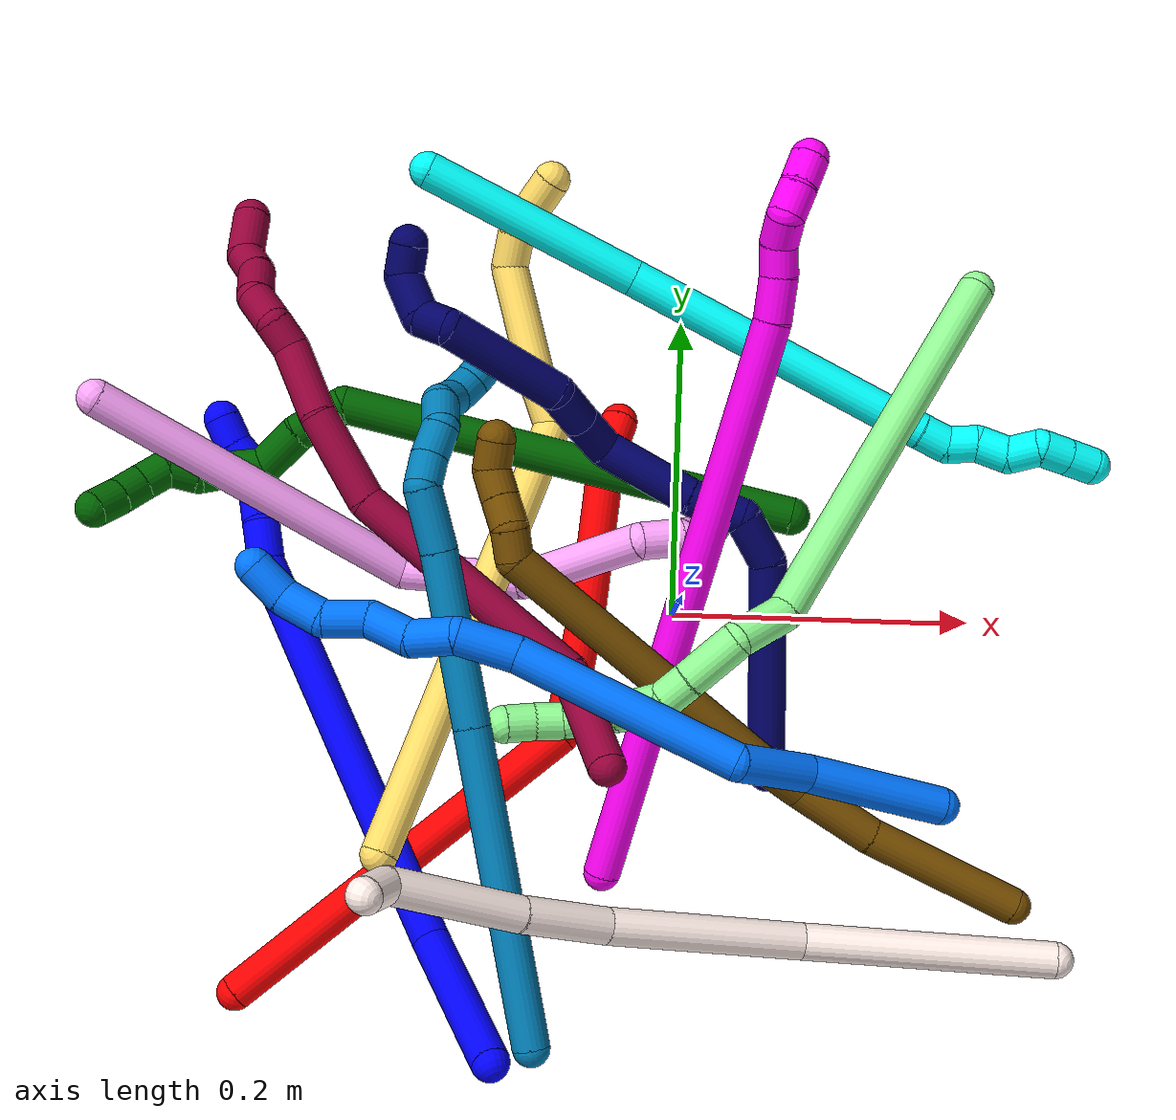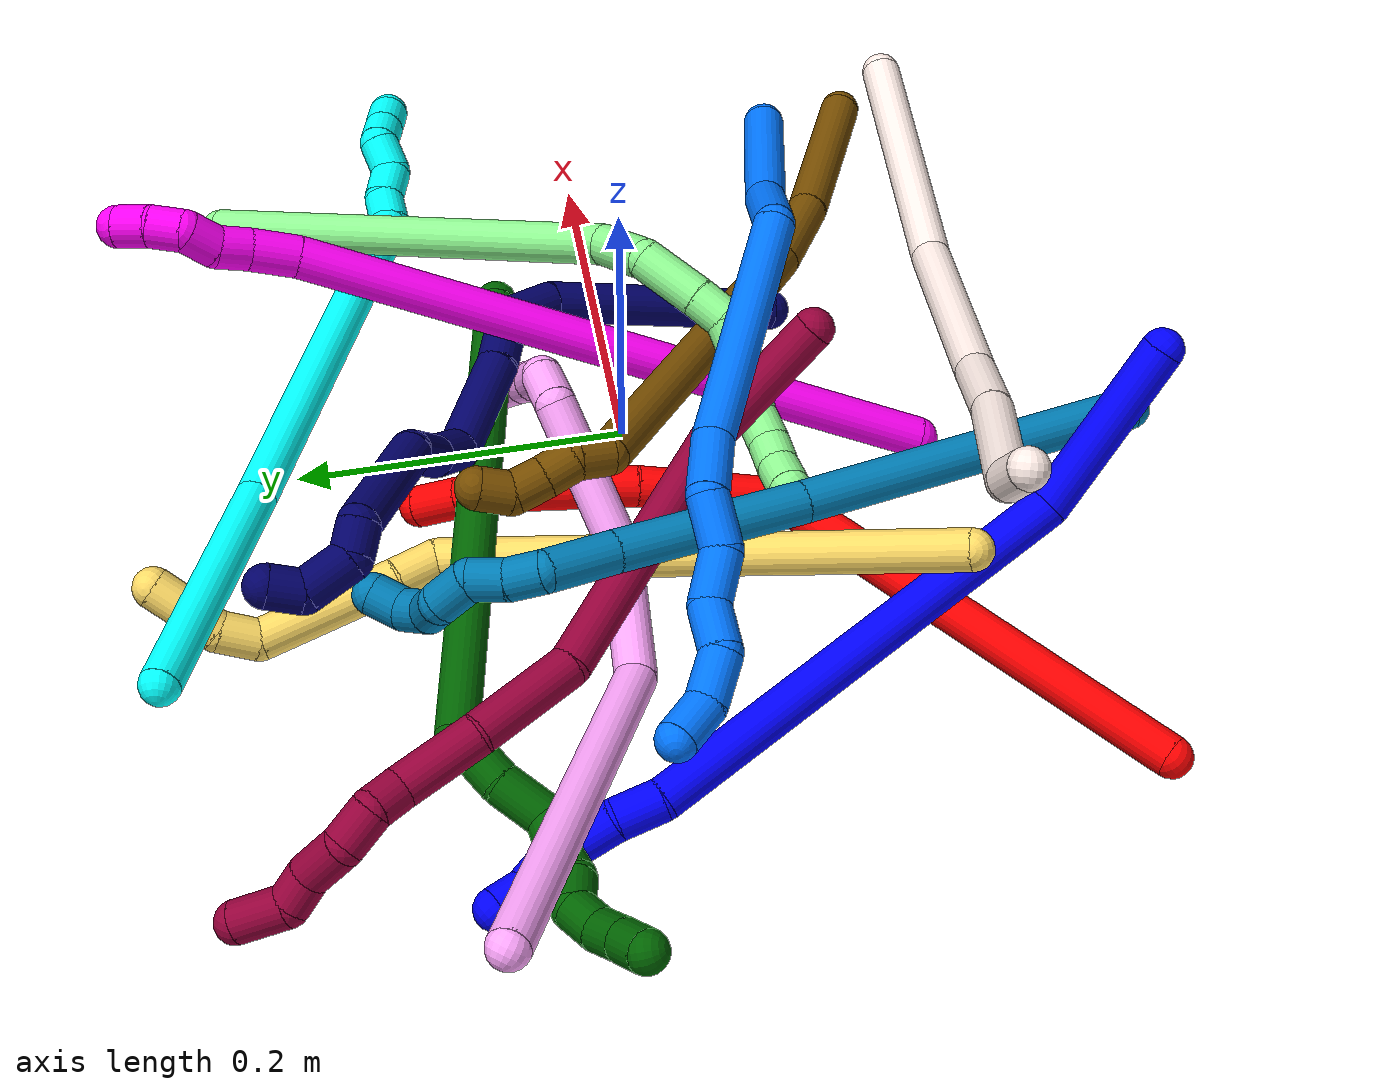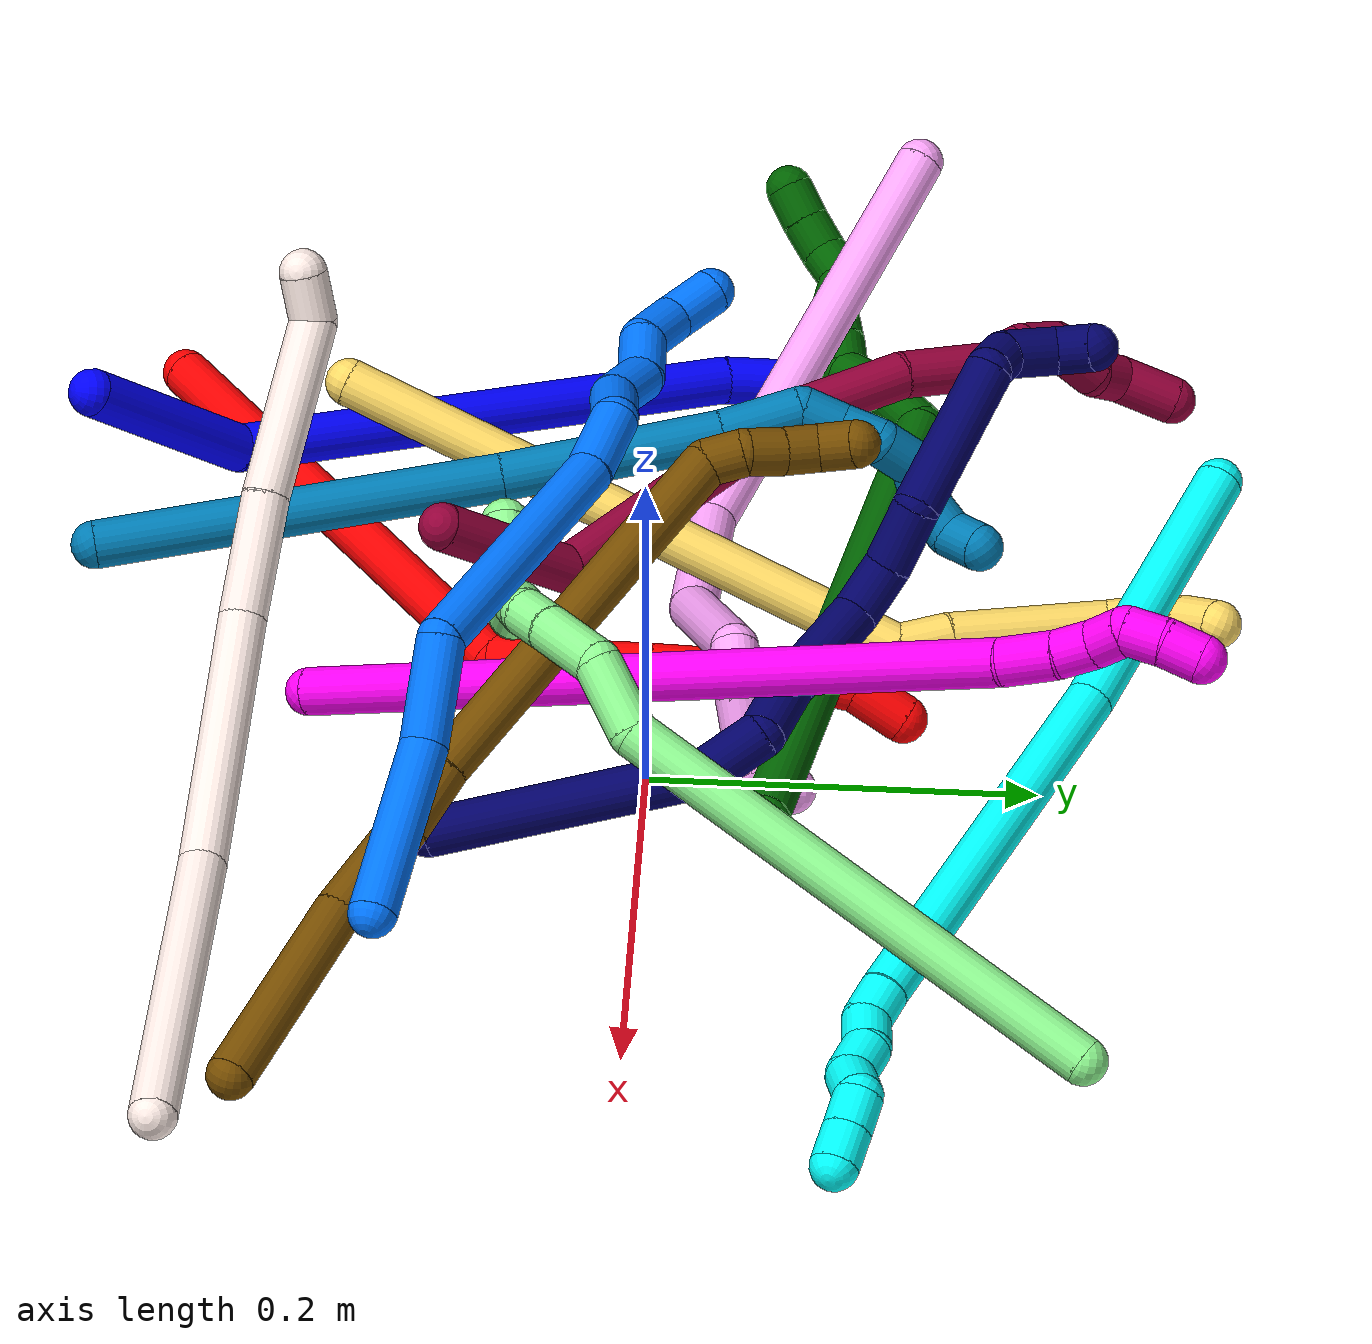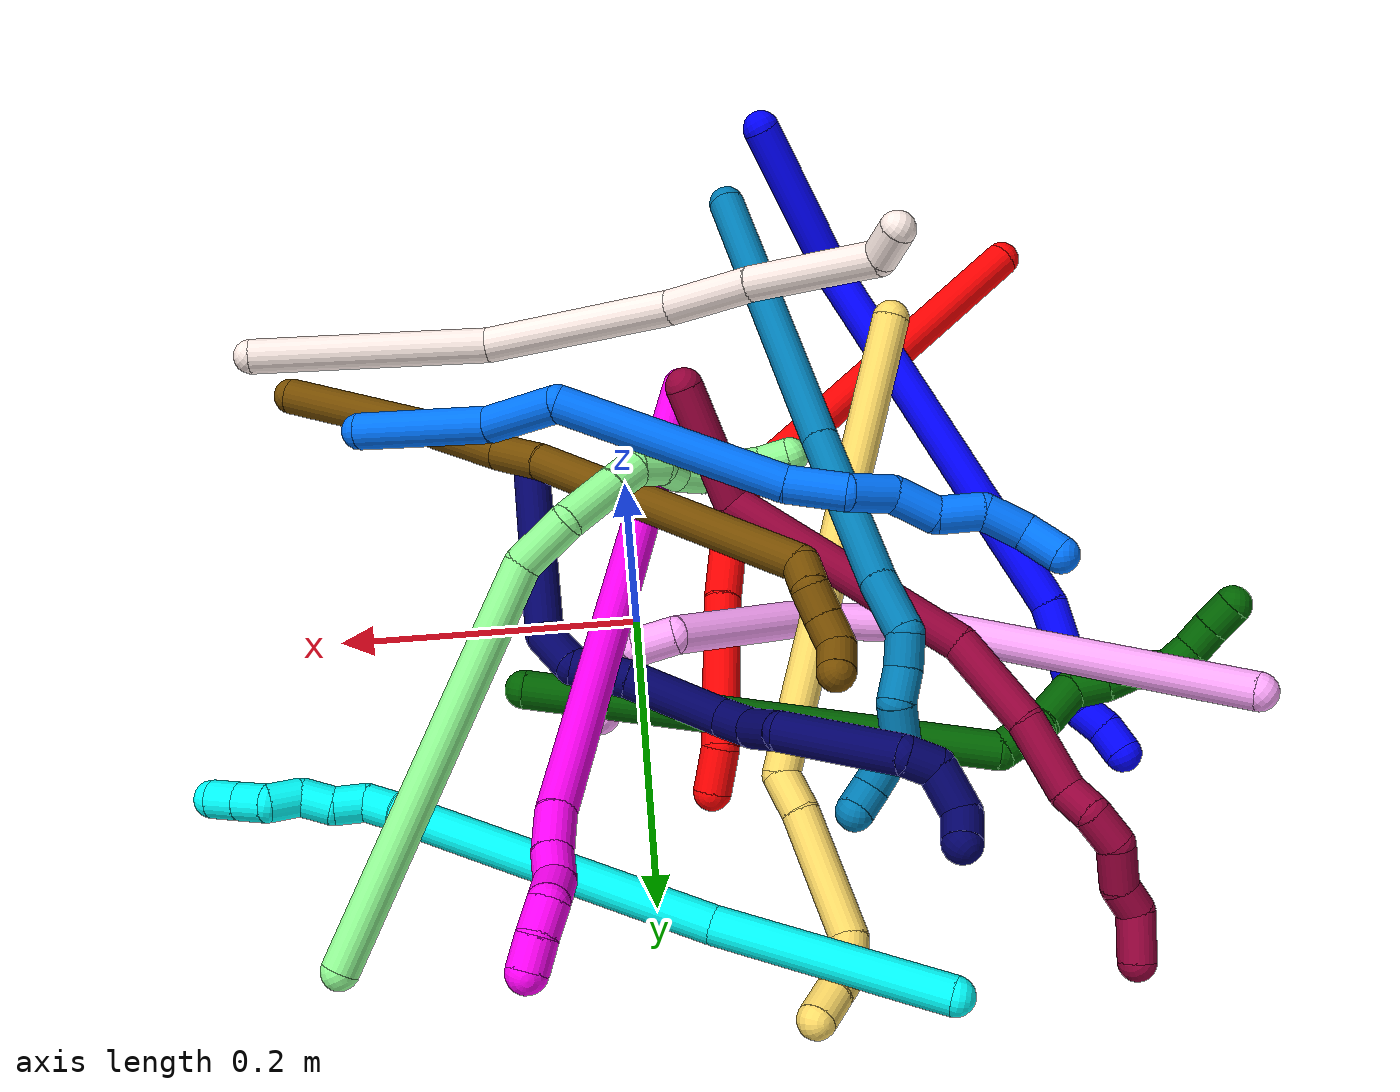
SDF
<sdf version="1.7">
 <world name="default">
  <plugin name="TubeGeneratorPlugin" filename="libtube_generator_plugin.so"/>
  <model name="photoneo_s_sensor">
   <static>1</static>
   <pose>0 0 2 1.57079 1.57079 3.14159</pose>
   <link name="link">
    <inertial><mass>0.1</mass></inertial>
    <sensor name="sensor" type="depth">
     <update_rate>30</update_rate>
     <camera>
      <horizontal_fov>1.22</horizontal_fov>
      <image><width>1920</width><height>1200</height><format>B8G8R8</format></image>
      <clip><near>0.1</near><far>4</far></clip>
      <depth_camera><output>points</output></depth_camera>
     </camera>
     <plugin name="camera_plugin" filename="libgazebo_ros_depth_camera.so">
      <baseline>0.2</baseline>
      <alwaysOn>1</alwaysOn>
      <updateRate>0.0</updateRate>
      <cameraName>camera_ir</cameraName>
      <imageTopicName>/camera/color/image_raw</imageTopicName>
      <cameraInfoTopicName>/camera/color/camera_info</cameraInfoTopicName>
      <depthImageTopicName>/camera/depth/image_raw</depthImageTopicName>
      <depthImageCameraInfoTopicName>/camera/depth/camera_info</depthImageCameraInfoTopicName>
      <pointCloudTopicName>/camera/depth/points</pointCloudTopicName>
      <frameName>fr_optical</frameName>
      <pointCloudCutoff>0.1</pointCloudCutoff>
      <pointCloudCutoffMax>2.0</pointCloudCutoffMax>
      <distortionK1>0</distortionK1>
      <distortionK2>0</distortionK2>
      <distortionK3>0</distortionK3>
      <distortionT1>0</distortionT1>
      <distortionT2>0</distortionT2>
      <CxPrime>0</CxPrime>
      <Cx>0</Cx>
      <Cy>0</Cy>
      <focalLength>0</focalLength>
      <hackBaseline>0</hackBaseline>
     </plugin>
    </sensor>
   </link>
  </model>
  <gravity>0 0 -9.8</gravity>
  <magnetic_field>6e-06 2.3e-05 -4.2e-05</magnetic_field>
  <atmosphere type="adiabatic"/>
  <physics name="default_physics" default="0" type="ode">
   <max_step_size>0.003</max_step_size>
   <real_time_factor>1</real_time_factor>
   <real_time_update_rate>1000</real_time_update_rate>
   <max_contacts>10000</max_contacts>
   <ode>
    <solver>
     <type>quick</type>
     <iters>100</iters>
     <sor>1.3</sor>
     <use_dynamic_moi_rescaling>0</use_dynamic_moi_rescaling>
    </solver>
    <constraints>
     <contact_max_correcting_vel>0</contact_max_correcting_vel>
     <contact_surface_layer>0.001</contact_surface_layer>
     <cfm>0</cfm>
     <erp>0.2</erp>
    </constraints>
   </ode>
  </physics>
  <scene><ambient>0.4 0.4 0.4 1</ambient><background>0.7 0.7 0.7 1</background><shadows>0</shadows></scene>
  <audio><device>default</device></audio>
  <spherical_coordinates>
   <surface_model>EARTH_WGS84</surface_model>
   <latitude_deg>0</latitude_deg>
   <longitude_deg>0</longitude_deg>
   <elevation>0</elevation>
   <heading_deg>0</heading_deg>
  </spherical_coordinates>
  <model name="bin">
   <static>1</static>
   <link name="bottom">
    <collision name="collision-bottom">
     <pose>0 0 -0.01 0 -0 0</pose>
     <geometry><box><size>0.8 0.6 0.02</size></box></geometry>
     <surface>
      <friction><ode><mu>100</mu><mu2>100</mu2></ode></friction>
      <contact><collide_bitmask>65535</collide_bitmask></contact>
     </surface>
    </collision>
   </link>
   <link name="west_wall">
    <collision name="collision-west_wall">
     <pose>-0.41 0 0.1 0 -0 0</pose>
     <geometry><box><size>0.02 0.6 0.2</size></box></geometry>
     <surface>
      <friction><ode><mu>100</mu><mu2>100</mu2></ode></friction>
      <contact><collide_bitmask>65535</collide_bitmask></contact>
     </surface>
    </collision>
   </link>
   <link name="east_wall">
    <collision name="collision-east_wall">
     <pose>0.41 0 0.1 0 -0 0</pose>
     <geometry><box><size>0.02 0.6 0.2</size></box></geometry>
     <surface>
      <friction><ode><mu>100</mu><mu2>100</mu2></ode></friction>
      <contact><collide_bitmask>65535</collide_bitmask></contact>
     </surface>
    </collision>
   </link>
   <link name="south_wall">
    <collision name="collision-south_wall">
     <pose>0 -0.31 0.1 0 -0 0</pose>
     <geometry><box><size>0.8 0.02 0.2</size></box></geometry>
     <surface>
      <friction><ode><mu>100</mu><mu2>100</mu2></ode></friction>
      <contact><collide_bitmask>65535</collide_bitmask></contact>
     </surface>
    </collision>
   </link>
   <link name="north_wall">
    <collision name="collision-north_wall">
     <pose>0 0.31 0.1 0 -0 0</pose>
     <geometry><box><size>0.8 0.02 0.2</size></box></geometry>
     <surface>
      <friction><ode><mu>100</mu><mu2>100</mu2></ode></friction>
      <contact><collide_bitmask>65535</collide_bitmask></contact>
     </surface>
    </collision>
   </link>
  </model>
  <model name="1">
   <static>0</static>
   <link name="1">
    <collision name="collision-cylinder-e_1_1_4">
     <pose>0.001584 -0.016772 -0.051891 2.82898 0.029044 0.183791</pose>
     <geometry><cylinder><radius>0.0125</radius><length>0.109115</length></cylinder></geometry>
     <surface>
      <friction><ode><mu>1.16</mu><mu2>1.16</mu2><slip1>0</slip1><slip2>0</slip2></ode></friction>
      <contact><ode><kp>1e+06</kp><kd>1</kd><max_vel>0</max_vel><min_depth>0.001</min_depth></ode></contact>
     </surface>
    </collision>
    <visual name="visual-cylinder-e_1_1_4">
     <pose>0.001584 -0.016772 -0.051891 2.82898 0.029044 0.183791</pose>
     <geometry><cylinder><radius>0.0125</radius><length>0.109115</length></cylinder></geometry>
     <material><ambient>0 0 1 1</ambient></material>
    </visual>
    <collision name="collision-cylinder-e_2_4_5">
     <pose>-0.013716 -0.001161 -0.237657 -2.90426 -0.12198 0.946687</pose>
     <geometry><cylinder><radius>0.0125</radius><length>0.277533</length></cylinder></geometry>
     <surface>
      <friction><ode><mu>1.16</mu><mu2>1.16</mu2><slip1>0</slip1><slip2>0</slip2></ode></friction>
      <contact><ode><kp>1e+06</kp><kd>1</kd><max_vel>0</max_vel><min_depth>0.001</min_depth></ode></contact>
     </surface>
    </collision>
    <visual name="visual-cylinder-e_2_4_5">
     <pose>-0.013716 -0.001161 -0.237657 -2.90426 -0.12198 0.946687</pose>
     <geometry><cylinder><radius>0.0125</radius><length>0.277533</length></cylinder></geometry>
     <material><ambient>0 0 1 1</ambient></material>
    </visual>
    <collision name="collision-cylinder-e_3_5_6">
     <pose>-0.028817 0.035622 -0.38454 -2.81548 0.129185 -0.749207</pose>
     <geometry><cylinder><radius>0.0125</radius><length>0.027695</length></cylinder></geometry>
     <surface>
      <friction><ode><mu>1.16</mu><mu2>1.16</mu2><slip1>0</slip1><slip2>0</slip2></ode></friction>
      <contact><ode><kp>1e+06</kp><kd>1</kd><max_vel>0</max_vel><min_depth>0.001</min_depth></ode></contact>
     </surface>
    </collision>
    <visual name="visual-cylinder-e_3_5_6">
     <pose>-0.028817 0.035622 -0.38454 -2.81548 0.129185 -0.749207</pose>
     <geometry><cylinder><radius>0.0125</radius><length>0.027695</length></cylinder></geometry>
     <material><ambient>0 0 1 1</ambient></material>
    </visual>
    <collision name="collision-cylinder-e_4_6_7">
     <pose>-0.024769 0.041117 -0.409801 -3.05242 0.181993 -2.23205</pose>
     <geometry><cylinder><radius>0.0125</radius><length>0.025016</length></cylinder></geometry>
     <surface>
      <friction><ode><mu>1.16</mu><mu2>1.16</mu2><slip1>0</slip1><slip2>0</slip2></ode></friction>
      <contact><ode><kp>1e+06</kp><kd>1</kd><max_vel>0</max_vel><min_depth>0.001</min_depth></ode></contact>
     </surface>
    </collision>
    <visual name="visual-cylinder-e_4_6_7">
     <pose>-0.024769 0.041117 -0.409801 -3.05242 0.181993 -2.23205</pose>
     <geometry><cylinder><radius>0.0125</radius><length>0.025016</length></cylinder></geometry>
     <material><ambient>0 0 1 1</ambient></material>
    </visual>
    <collision name="collision-cylinder-e_5_7_8">
     <pose>-0.020491 0.042107 -0.431983 3.13104 0.200114 3.03654</pose>
     <geometry><cylinder><radius>0.0125</radius><length>0.020264</length></cylinder></geometry>
     <surface>
      <friction><ode><mu>1.16</mu><mu2>1.16</mu2><slip1>0</slip1><slip2>0</slip2></ode></friction>
      <contact><ode><kp>1e+06</kp><kd>1</kd><max_vel>0</max_vel><min_depth>0.001</min_depth></ode></contact>
     </surface>
    </collision>
    <visual name="visual-cylinder-e_5_7_8">
     <pose>-0.020491 0.042107 -0.431983 3.13104 0.200114 3.03654</pose>
     <geometry><cylinder><radius>0.0125</radius><length>0.020264</length></cylinder></geometry>
     <material><ambient>0 0 1 1</ambient></material>
    </visual>
    <collision name="collision-cylinder-e_6_8_9">
     <pose>-0.022906 0.044431 -0.450637 -2.87008 -0.45483 2.07513</pose>
     <geometry><cylinder><radius>0.0125</radius><length>0.020163</length></cylinder></geometry>
     <surface>
      <friction><ode><mu>1.16</mu><mu2>1.16</mu2><slip1>0</slip1><slip2>0</slip2></ode></friction>
      <contact><ode><kp>1e+06</kp><kd>1</kd><max_vel>0</max_vel><min_depth>0.001</min_depth></ode></contact>
     </surface>
    </collision>
    <visual name="visual-cylinder-e_6_8_9">
     <pose>-0.022906 0.044431 -0.450637 -2.87008 -0.45483 2.07513</pose>
     <geometry><cylinder><radius>0.0125</radius><length>0.020163</length></cylinder></geometry>
     <material><ambient>0 0 1 1</ambient></material>
    </visual>
    <collision name="collision-cylinder-e_7_9_2">
     <pose>-0.029291 0.051039 -0.468354 -2.70658 -0.194723 0.832271</pose>
     <geometry><cylinder><radius>0.0125</radius><length>0.020214</length></cylinder></geometry>
     <surface>
      <friction><ode><mu>1.16</mu><mu2>1.16</mu2><slip1>0</slip1><slip2>0</slip2></ode></friction>
      <contact><ode><kp>1e+06</kp><kd>1</kd><max_vel>0</max_vel><min_depth>0.001</min_depth></ode></contact>
     </surface>
    </collision>
    <visual name="visual-cylinder-e_7_9_2">
     <pose>-0.029291 0.051039 -0.468354 -2.70658 -0.194723 0.832271</pose>
     <geometry><cylinder><radius>0.0125</radius><length>0.020214</length></cylinder></geometry>
     <material><ambient>0 0 1 1</ambient></material>
    </visual>
    <collision name="collision-sphere-2">
     <pose>-0.031247 0.055218 -0.477347 0 -0 0</pose>
     <geometry><sphere><radius>0.0125</radius></sphere></geometry>
     <surface>
      <friction><ode><mu>1.16</mu><mu2>1.16</mu2><slip1>0</slip1><slip2>0</slip2></ode></friction>
      <contact><ode><kp>1e+06</kp><kd>1</kd><max_vel>0</max_vel><min_depth>0.001</min_depth></ode></contact>
     </surface>
    </collision>
    <visual name="visual-sphere-2">
     <pose>-0.031247 0.055218 -0.477347 0 -0 0</pose>
     <geometry><sphere><radius>0.0125</radius></sphere></geometry>
     <material><ambient>0 0 1 1</ambient></material>
    </visual>
    <collision name="collision-sphere-9">
     <pose>-0.027335 0.04686 -0.459362 0 -0 0</pose>
     <geometry><sphere><radius>0.0125</radius></sphere></geometry>
     <surface>
      <friction><ode><mu>1.16</mu><mu2>1.16</mu2><slip1>0</slip1><slip2>0</slip2></ode></friction>
      <contact><ode><kp>1e+06</kp><kd>1</kd><max_vel>0</max_vel><min_depth>0.001</min_depth></ode></contact>
     </surface>
    </collision>
    <visual name="visual-sphere-9">
     <pose>-0.027335 0.04686 -0.459362 0 -0 0</pose>
     <geometry><sphere><radius>0.0125</radius></sphere></geometry>
     <material><ambient>0 0 1 1</ambient></material>
    </visual>
    <collision name="collision-sphere-4">
     <pose>0.003169 -0.033544 -0.103783 0 -0 0</pose>
     <geometry><sphere><radius>0.0125</radius></sphere></geometry>
     <surface>
      <friction><ode><mu>1.16</mu><mu2>1.16</mu2><slip1>0</slip1><slip2>0</slip2></ode></friction>
      <contact><ode><kp>1e+06</kp><kd>1</kd><max_vel>0</max_vel><min_depth>0.001</min_depth></ode></contact>
     </surface>
    </collision>
    <visual name="visual-sphere-4">
     <pose>0.003169 -0.033544 -0.103783 0 -0 0</pose>
     <geometry><sphere><radius>0.0125</radius></sphere></geometry>
     <material><ambient>0 0 1 1</ambient></material>
    </visual>
    <collision name="collision-sphere-1">
     <geometry><sphere><radius>0.0125</radius></sphere></geometry>
     <surface>
      <friction><ode><mu>1.16</mu><mu2>1.16</mu2><slip1>0</slip1><slip2>0</slip2></ode></friction>
      <contact><ode><kp>1e+06</kp><kd>1</kd><max_vel>0</max_vel><min_depth>0.001</min_depth></ode></contact>
     </surface>
    </collision>
    <visual name="visual-sphere-1">
     <geometry><sphere><radius>0.0125</radius></sphere></geometry>
     <material><ambient>0 0 1 1</ambient></material>
    </visual>
    <collision name="collision-sphere-8">
     <pose>-0.018477 0.042002 -0.441912 0 -0 0</pose>
     <geometry><sphere><radius>0.0125</radius></sphere></geometry>
     <surface>
      <friction><ode><mu>1.16</mu><mu2>1.16</mu2><slip1>0</slip1><slip2>0</slip2></ode></friction>
      <contact><ode><kp>1e+06</kp><kd>1</kd><max_vel>0</max_vel><min_depth>0.001</min_depth></ode></contact>
     </surface>
    </collision>
    <visual name="visual-sphere-8">
     <pose>-0.018477 0.042002 -0.441912 0 -0 0</pose>
     <geometry><sphere><radius>0.0125</radius></sphere></geometry>
     <material><ambient>0 0 1 1</ambient></material>
    </visual>
    <collision name="collision-sphere-5">
     <pose>-0.030601 0.031223 -0.371532 0 -0 0</pose>
     <geometry><sphere><radius>0.0125</radius></sphere></geometry>
     <surface>
      <friction><ode><mu>1.16</mu><mu2>1.16</mu2><slip1>0</slip1><slip2>0</slip2></ode></friction>
      <contact><ode><kp>1e+06</kp><kd>1</kd><max_vel>0</max_vel><min_depth>0.001</min_depth></ode></contact>
     </surface>
    </collision>
    <visual name="visual-sphere-5">
     <pose>-0.030601 0.031223 -0.371532 0 -0 0</pose>
     <geometry><sphere><radius>0.0125</radius></sphere></geometry>
     <material><ambient>0 0 1 1</ambient></material>
    </visual>
    <collision name="collision-sphere-6">
     <pose>-0.027033 0.040021 -0.397548 0 -0 0</pose>
     <geometry><sphere><radius>0.0125</radius></sphere></geometry>
     <surface>
      <friction><ode><mu>1.16</mu><mu2>1.16</mu2><slip1>0</slip1><slip2>0</slip2></ode></friction>
      <contact><ode><kp>1e+06</kp><kd>1</kd><max_vel>0</max_vel><min_depth>0.001</min_depth></ode></contact>
     </surface>
    </collision>
    <visual name="visual-sphere-6">
     <pose>-0.027033 0.040021 -0.397548 0 -0 0</pose>
     <geometry><sphere><radius>0.0125</radius></sphere></geometry>
     <material><ambient>0 0 1 1</ambient></material>
    </visual>
    <collision name="collision-sphere-7">
     <pose>-0.022505 0.042212 -0.422054 0 -0 0</pose>
     <geometry><sphere><radius>0.0125</radius></sphere></geometry>
     <surface>
      <friction><ode><mu>1.16</mu><mu2>1.16</mu2><slip1>0</slip1><slip2>0</slip2></ode></friction>
      <contact><ode><kp>1e+06</kp><kd>1</kd><max_vel>0</max_vel><min_depth>0.001</min_depth></ode></contact>
     </surface>
    </collision>
    <visual name="visual-sphere-7">
     <pose>-0.022505 0.042212 -0.422054 0 -0 0</pose>
     <geometry><sphere><radius>0.0125</radius></sphere></geometry>
     <material><ambient>0 0 1 1</ambient></material>
    </visual>
    <inertial>
     <pose>-0.013041 0.005288 -0.239657 0 -0 0</pose>
     <mass>0.5</mass>
     <inertia>
      <ixx>0.00261</ixx>
      <ixy>0</ixy>
      <ixz>0</ixz>
      <iyy>0.000387</iyy>
      <iyz>0</iyz>
      <izz>-0.000208</izz>
     </inertia>
    </inertial>
   </link>
   <pose>-0.108408 -0.288502 0.152193 1.10258 0.363868 0.263491</pose>
  </model>
  <model name="2">
   <static>0</static>
   <link name="2">
    <collision name="collision-cylinder-e_1_1_4">
     <pose>0.007608 0.120166 -0.070526 -2.10153 0.054549 -0.095216</pose>
     <geometry><cylinder><radius>0.0125</radius><length>0.279081</length></cylinder></geometry>
     <surface>
      <friction><ode><mu>1.16</mu><mu2>1.16</mu2><slip1>0</slip1><slip2>0</slip2></ode></friction>
      <contact><ode><kp>1e+06</kp><kd>1</kd><max_vel>0</max_vel><min_depth>0.001</min_depth></ode></contact>
     </surface>
    </collision>
    <visual name="visual-cylinder-e_1_1_4">
     <pose>0.007608 0.120166 -0.070526 -2.10153 0.054549 -0.095216</pose>
     <geometry><cylinder><radius>0.0125</radius><length>0.279081</length></cylinder></geometry>
     <material><ambient>1 0 0 1</ambient></material>
    </visual>
    <collision name="collision-cylinder-e_2_4_5">
     <pose>0.039938 0.259195 -0.170825 -2.57684 0.611681 -1.65532</pose>
     <geometry><cylinder><radius>0.0125</radius><length>0.086104</length></cylinder></geometry>
     <surface>
      <friction><ode><mu>1.16</mu><mu2>1.16</mu2><slip1>0</slip1><slip2>0</slip2></ode></friction>
      <contact><ode><kp>1e+06</kp><kd>1</kd><max_vel>0</max_vel><min_depth>0.001</min_depth></ode></contact>
     </surface>
    </collision>
    <visual name="visual-cylinder-e_2_4_5">
     <pose>0.039938 0.259195 -0.170825 -2.57684 0.611681 -1.65532</pose>
     <geometry><cylinder><radius>0.0125</radius><length>0.086104</length></cylinder></geometry>
     <material><ambient>1 0 0 1</ambient></material>
    </visual>
    <collision name="collision-cylinder-e_3_5_6">
     <pose>0.092572 0.295938 -0.22599 -2.52811 0.732134 -1.76052</pose>
     <geometry><cylinder><radius>0.0125</radius><length>0.08351</length></cylinder></geometry>
     <surface>
      <friction><ode><mu>1.16</mu><mu2>1.16</mu2><slip1>0</slip1><slip2>0</slip2></ode></friction>
      <contact><ode><kp>1e+06</kp><kd>1</kd><max_vel>0</max_vel><min_depth>0.001</min_depth></ode></contact>
     </surface>
    </collision>
    <visual name="visual-cylinder-e_3_5_6">
     <pose>0.092572 0.295938 -0.22599 -2.52811 0.732134 -1.76052</pose>
     <geometry><cylinder><radius>0.0125</radius><length>0.08351</length></cylinder></geometry>
     <material><ambient>1 0 0 1</ambient></material>
    </visual>
    <collision name="collision-cylinder-e_4_6_7">
     <pose>0.128458 0.319397 -0.256233 -2.28635 0.823183 -1.52773</pose>
     <geometry><cylinder><radius>0.0125</radius><length>0.021748</length></cylinder></geometry>
     <surface>
      <friction><ode><mu>1.16</mu><mu2>1.16</mu2><slip1>0</slip1><slip2>0</slip2></ode></friction>
      <contact><ode><kp>1e+06</kp><kd>1</kd><max_vel>0</max_vel><min_depth>0.001</min_depth></ode></contact>
     </surface>
    </collision>
    <visual name="visual-cylinder-e_4_6_7">
     <pose>0.128458 0.319397 -0.256233 -2.28635 0.823183 -1.52773</pose>
     <geometry><cylinder><radius>0.0125</radius><length>0.021748</length></cylinder></geometry>
     <material><ambient>1 0 0 1</ambient></material>
    </visual>
    <collision name="collision-cylinder-e_5_7_2">
     <pose>0.146278 0.335784 -0.263241 -1.76793 0.729197 -0.871221</pose>
     <geometry><cylinder><radius>0.0125</radius><length>0.029557</length></cylinder></geometry>
     <surface>
      <friction><ode><mu>1.16</mu><mu2>1.16</mu2><slip1>0</slip1><slip2>0</slip2></ode></friction>
      <contact><ode><kp>1e+06</kp><kd>1</kd><max_vel>0</max_vel><min_depth>0.001</min_depth></ode></contact>
     </surface>
    </collision>
    <visual name="visual-cylinder-e_5_7_2">
     <pose>0.146278 0.335784 -0.263241 -1.76793 0.729197 -0.871221</pose>
     <geometry><cylinder><radius>0.0125</radius><length>0.029557</length></cylinder></geometry>
     <material><ambient>1 0 0 1</ambient></material>
    </visual>
    <collision name="collision-sphere-2">
     <pose>0.156125 0.346591 -0.2654 0 -0 0</pose>
     <geometry><sphere><radius>0.0125</radius></sphere></geometry>
     <surface>
      <friction><ode><mu>1.16</mu><mu2>1.16</mu2><slip1>0</slip1><slip2>0</slip2></ode></friction>
      <contact><ode><kp>1e+06</kp><kd>1</kd><max_vel>0</max_vel><min_depth>0.001</min_depth></ode></contact>
     </surface>
    </collision>
    <visual name="visual-sphere-2">
     <pose>0.156125 0.346591 -0.2654 0 -0 0</pose>
     <geometry><sphere><radius>0.0125</radius></sphere></geometry>
     <material><ambient>1 0 0 1</ambient></material>
    </visual>
    <collision name="collision-sphere-7">
     <pose>0.136432 0.324977 -0.261083 0 -0 0</pose>
     <geometry><sphere><radius>0.0125</radius></sphere></geometry>
     <surface>
      <friction><ode><mu>1.16</mu><mu2>1.16</mu2><slip1>0</slip1><slip2>0</slip2></ode></friction>
      <contact><ode><kp>1e+06</kp><kd>1</kd><max_vel>0</max_vel><min_depth>0.001</min_depth></ode></contact>
     </surface>
    </collision>
    <visual name="visual-sphere-7">
     <pose>0.136432 0.324977 -0.261083 0 -0 0</pose>
     <geometry><sphere><radius>0.0125</radius></sphere></geometry>
     <material><ambient>1 0 0 1</ambient></material>
    </visual>
    <collision name="collision-sphere-6">
     <pose>0.120484 0.313817 -0.251382 0 -0 0</pose>
     <geometry><sphere><radius>0.0125</radius></sphere></geometry>
     <surface>
      <friction><ode><mu>1.16</mu><mu2>1.16</mu2><slip1>0</slip1><slip2>0</slip2></ode></friction>
      <contact><ode><kp>1e+06</kp><kd>1</kd><max_vel>0</max_vel><min_depth>0.001</min_depth></ode></contact>
     </surface>
    </collision>
    <visual name="visual-sphere-6">
     <pose>0.120484 0.313817 -0.251382 0 -0 0</pose>
     <geometry><sphere><radius>0.0125</radius></sphere></geometry>
     <material><ambient>1 0 0 1</ambient></material>
    </visual>
    <collision name="collision-sphere-5">
     <pose>0.064661 0.278059 -0.200598 0 -0 0</pose>
     <geometry><sphere><radius>0.0125</radius></sphere></geometry>
     <surface>
      <friction><ode><mu>1.16</mu><mu2>1.16</mu2><slip1>0</slip1><slip2>0</slip2></ode></friction>
      <contact><ode><kp>1e+06</kp><kd>1</kd><max_vel>0</max_vel><min_depth>0.001</min_depth></ode></contact>
     </surface>
    </collision>
    <visual name="visual-sphere-5">
     <pose>0.064661 0.278059 -0.200598 0 -0 0</pose>
     <geometry><sphere><radius>0.0125</radius></sphere></geometry>
     <material><ambient>1 0 0 1</ambient></material>
    </visual>
    <collision name="collision-sphere-1">
     <geometry><sphere><radius>0.0125</radius></sphere></geometry>
     <surface>
      <friction><ode><mu>1.16</mu><mu2>1.16</mu2><slip1>0</slip1><slip2>0</slip2></ode></friction>
      <contact><ode><kp>1e+06</kp><kd>1</kd><max_vel>0</max_vel><min_depth>0.001</min_depth></ode></contact>
     </surface>
    </collision>
    <visual name="visual-sphere-1">
     <geometry><sphere><radius>0.0125</radius></sphere></geometry>
     <material><ambient>1 0 0 1</ambient></material>
    </visual>
    <collision name="collision-sphere-4">
     <pose>0.015216 0.240331 -0.141051 0 -0 0</pose>
     <geometry><sphere><radius>0.0125</radius></sphere></geometry>
     <surface>
      <friction><ode><mu>1.16</mu><mu2>1.16</mu2><slip1>0</slip1><slip2>0</slip2></ode></friction>
      <contact><ode><kp>1e+06</kp><kd>1</kd><max_vel>0</max_vel><min_depth>0.001</min_depth></ode></contact>
     </surface>
    </collision>
    <visual name="visual-sphere-4">
     <pose>0.015216 0.240331 -0.141051 0 -0 0</pose>
     <geometry><sphere><radius>0.0125</radius></sphere></geometry>
     <material><ambient>1 0 0 1</ambient></material>
    </visual>
    <inertial>
     <pose>0.04082 0.194877 -0.133233 0 -0 0</pose>
     <mass>0.5</mass>
     <inertia>
      <ixx>0.001554</ixx>
      <ixy>0</ixy>
      <ixz>0</ixz>
      <iyy>-0.001092</iyy>
      <iyz>0</iyz>
      <izz>-0.00181</izz>
     </inertia>
    </inertial>
   </link>
   <pose>-0.286566 -0.263479 0.011496 -2.63288 0.38366 2.21113</pose>
  </model>
  <model name="3">
   <static>0</static>
   <link name="3">
    <collision name="collision-cylinder-e_1_1_4">
     <pose>0.025206 -0.015582 -0.071401 2.92673 0.332128 1.9981</pose>
     <geometry><cylinder><radius>0.0125</radius><length>0.154611</length></cylinder></geometry>
     <surface>
      <friction><ode><mu>1.16</mu><mu2>1.16</mu2><slip1>0</slip1><slip2>0</slip2></ode></friction>
      <contact><ode><kp>1e+06</kp><kd>1</kd><max_vel>0</max_vel><min_depth>0.001</min_depth></ode></contact>
     </surface>
    </collision>
    <visual name="visual-cylinder-e_1_1_4">
     <pose>0.025206 -0.015582 -0.071401 2.92673 0.332128 1.9981</pose>
     <geometry><cylinder><radius>0.0125</radius><length>0.154611</length></cylinder></geometry>
     <material><ambient>0.003922 1 0.996078 1</ambient></material>
    </visual>
    <collision name="collision-cylinder-e_2_4_5">
     <pose>0.084124 -0.041281 -0.247109 3.0449 0.311239 2.5433</pose>
     <geometry><cylinder><radius>0.0125</radius><length>0.220173</length></cylinder></geometry>
     <surface>
      <friction><ode><mu>1.16</mu><mu2>1.16</mu2><slip1>0</slip1><slip2>0</slip2></ode></friction>
      <contact><ode><kp>1e+06</kp><kd>1</kd><max_vel>0</max_vel><min_depth>0.001</min_depth></ode></contact>
     </surface>
    </collision>
    <visual name="visual-cylinder-e_2_4_5">
     <pose>0.084124 -0.041281 -0.247109 3.0449 0.311239 2.5433</pose>
     <geometry><cylinder><radius>0.0125</radius><length>0.220173</length></cylinder></geometry>
     <material><ambient>0.003922 1 0.996078 1</ambient></material>
    </visual>
    <collision name="collision-cylinder-e_3_5_6">
     <pose>0.120963 -0.053057 -0.360888 2.96822 0.314262 2.13818</pose>
     <geometry><cylinder><radius>0.0125</radius><length>0.020222</length></cylinder></geometry>
     <surface>
      <friction><ode><mu>1.16</mu><mu2>1.16</mu2><slip1>0</slip1><slip2>0</slip2></ode></friction>
      <contact><ode><kp>1e+06</kp><kd>1</kd><max_vel>0</max_vel><min_depth>0.001</min_depth></ode></contact>
     </surface>
    </collision>
    <visual name="visual-cylinder-e_3_5_6">
     <pose>0.120963 -0.053057 -0.360888 2.96822 0.314262 2.13818</pose>
     <geometry><cylinder><radius>0.0125</radius><length>0.020222</length></cylinder></geometry>
     <material><ambient>0.003922 1 0.996078 1</ambient></material>
    </visual>
    <collision name="collision-cylinder-e_4_6_7">
     <pose>0.12185 -0.056544 -0.380275 2.95928 -0.218431 -1.75179</pose>
     <geometry><cylinder><radius>0.0125</radius><length>0.020655</length></cylinder></geometry>
     <surface>
      <friction><ode><mu>1.16</mu><mu2>1.16</mu2><slip1>0</slip1><slip2>0</slip2></ode></friction>
      <contact><ode><kp>1e+06</kp><kd>1</kd><max_vel>0</max_vel><min_depth>0.001</min_depth></ode></contact>
     </surface>
    </collision>
    <visual name="visual-cylinder-e_4_6_7">
     <pose>0.12185 -0.056544 -0.380275 2.95928 -0.218431 -1.75179</pose>
     <geometry><cylinder><radius>0.0125</radius><length>0.020655</length></cylinder></geometry>
     <material><ambient>0.003922 1 0.996078 1</ambient></material>
    </visual>
    <collision name="collision-cylinder-e_5_7_8">
     <pose>0.121295 -0.058583 -0.401171 3.12232 0.152073 2.8899</pose>
     <geometry><cylinder><radius>0.0125</radius><length>0.022222</length></cylinder></geometry>
     <surface>
      <friction><ode><mu>1.16</mu><mu2>1.16</mu2><slip1>0</slip1><slip2>0</slip2></ode></friction>
      <contact><ode><kp>1e+06</kp><kd>1</kd><max_vel>0</max_vel><min_depth>0.001</min_depth></ode></contact>
     </surface>
    </collision>
    <visual name="visual-cylinder-e_5_7_8">
     <pose>0.121295 -0.058583 -0.401171 3.12232 0.152073 2.8899</pose>
     <geometry><cylinder><radius>0.0125</radius><length>0.022222</length></cylinder></geometry>
     <material><ambient>0.003922 1 0.996078 1</ambient></material>
    </visual>
    <collision name="collision-cylinder-e_6_8_9">
     <pose>0.117951 -0.05905 -0.421965 3.11561 -0.473281 -3.03394</pose>
     <geometry><cylinder><radius>0.0125</radius><length>0.022059</length></cylinder></geometry>
     <surface>
      <friction><ode><mu>1.16</mu><mu2>1.16</mu2><slip1>0</slip1><slip2>0</slip2></ode></friction>
      <contact><ode><kp>1e+06</kp><kd>1</kd><max_vel>0</max_vel><min_depth>0.001</min_depth></ode></contact>
     </surface>
    </collision>
    <visual name="visual-cylinder-e_6_8_9">
     <pose>0.117951 -0.05905 -0.421965 3.11561 -0.473281 -3.03394</pose>
     <geometry><cylinder><radius>0.0125</radius><length>0.022059</length></cylinder></geometry>
     <material><ambient>0.003922 1 0.996078 1</ambient></material>
    </visual>
    <collision name="collision-cylinder-e_7_9_10">
     <pose>0.115183 -0.062927 -0.440833 2.76107 0.22768 1.07149</pose>
     <geometry><cylinder><radius>0.0125</radius><length>0.02002</length></cylinder></geometry>
     <surface>
      <friction><ode><mu>1.16</mu><mu2>1.16</mu2><slip1>0</slip1><slip2>0</slip2></ode></friction>
      <contact><ode><kp>1e+06</kp><kd>1</kd><max_vel>0</max_vel><min_depth>0.001</min_depth></ode></contact>
     </surface>
    </collision>
    <visual name="visual-cylinder-e_7_9_10">
     <pose>0.115183 -0.062927 -0.440833 2.76107 0.22768 1.07149</pose>
     <geometry><cylinder><radius>0.0125</radius><length>0.02002</length></cylinder></geometry>
     <material><ambient>0.003922 1 0.996078 1</ambient></material>
    </visual>
    <collision name="collision-cylinder-e_8_10_2">
     <pose>0.119738 -0.0701 -0.45897 2.76889 0.231133 1.10378</pose>
     <geometry><cylinder><radius>0.0125</radius><length>0.020038</length></cylinder></geometry>
     <surface>
      <friction><ode><mu>1.16</mu><mu2>1.16</mu2><slip1>0</slip1><slip2>0</slip2></ode></friction>
      <contact><ode><kp>1e+06</kp><kd>1</kd><max_vel>0</max_vel><min_depth>0.001</min_depth></ode></contact>
     </surface>
    </collision>
    <visual name="visual-cylinder-e_8_10_2">
     <pose>0.119738 -0.0701 -0.45897 2.76889 0.231133 1.10378</pose>
     <geometry><cylinder><radius>0.0125</radius><length>0.020038</length></cylinder></geometry>
     <material><ambient>0.003922 1 0.996078 1</ambient></material>
    </visual>
    <collision name="collision-sphere-2">
     <pose>0.122033 -0.073651 -0.468053 0 -0 0</pose>
     <geometry><sphere><radius>0.0125</radius></sphere></geometry>
     <surface>
      <friction><ode><mu>1.16</mu><mu2>1.16</mu2><slip1>0</slip1><slip2>0</slip2></ode></friction>
      <contact><ode><kp>1e+06</kp><kd>1</kd><max_vel>0</max_vel><min_depth>0.001</min_depth></ode></contact>
     </surface>
    </collision>
    <visual name="visual-sphere-2">
     <pose>0.122033 -0.073651 -0.468053 0 -0 0</pose>
     <geometry><sphere><radius>0.0125</radius></sphere></geometry>
     <material><ambient>0.003922 1 0.996078 1</ambient></material>
    </visual>
    <collision name="collision-sphere-10">
     <pose>0.117443 -0.066549 -0.449887 0 -0 0</pose>
     <geometry><sphere><radius>0.0125</radius></sphere></geometry>
     <surface>
      <friction><ode><mu>1.16</mu><mu2>1.16</mu2><slip1>0</slip1><slip2>0</slip2></ode></friction>
      <contact><ode><kp>1e+06</kp><kd>1</kd><max_vel>0</max_vel><min_depth>0.001</min_depth></ode></contact>
     </surface>
    </collision>
    <visual name="visual-sphere-10">
     <pose>0.117443 -0.066549 -0.449887 0 -0 0</pose>
     <geometry><sphere><radius>0.0125</radius></sphere></geometry>
     <material><ambient>0.003922 1 0.996078 1</ambient></material>
    </visual>
    <collision name="collision-sphere-9">
     <pose>0.112924 -0.059305 -0.431779 0 -0 0</pose>
     <geometry><sphere><radius>0.0125</radius></sphere></geometry>
     <surface>
      <friction><ode><mu>1.16</mu><mu2>1.16</mu2><slip1>0</slip1><slip2>0</slip2></ode></friction>
      <contact><ode><kp>1e+06</kp><kd>1</kd><max_vel>0</max_vel><min_depth>0.001</min_depth></ode></contact>
     </surface>
    </collision>
    <visual name="visual-sphere-9">
     <pose>0.112924 -0.059305 -0.431779 0 -0 0</pose>
     <geometry><sphere><radius>0.0125</radius></sphere></geometry>
     <material><ambient>0.003922 1 0.996078 1</ambient></material>
    </visual>
    <collision name="collision-sphere-4">
     <pose>0.050412 -0.031163 -0.142801 0 -0 0</pose>
     <geometry><sphere><radius>0.0125</radius></sphere></geometry>
     <surface>
      <friction><ode><mu>1.16</mu><mu2>1.16</mu2><slip1>0</slip1><slip2>0</slip2></ode></friction>
      <contact><ode><kp>1e+06</kp><kd>1</kd><max_vel>0</max_vel><min_depth>0.001</min_depth></ode></contact>
     </surface>
    </collision>
    <visual name="visual-sphere-4">
     <pose>0.050412 -0.031163 -0.142801 0 -0 0</pose>
     <geometry><sphere><radius>0.0125</radius></sphere></geometry>
     <material><ambient>0.003922 1 0.996078 1</ambient></material>
    </visual>
    <collision name="collision-sphere-1">
     <geometry><sphere><radius>0.0125</radius></sphere></geometry>
     <surface>
      <friction><ode><mu>1.16</mu><mu2>1.16</mu2><slip1>0</slip1><slip2>0</slip2></ode></friction>
      <contact><ode><kp>1e+06</kp><kd>1</kd><max_vel>0</max_vel><min_depth>0.001</min_depth></ode></contact>
     </surface>
    </collision>
    <visual name="visual-sphere-1">
     <geometry><sphere><radius>0.0125</radius></sphere></geometry>
     <material><ambient>0.003922 1 0.996078 1</ambient></material>
    </visual>
    <collision name="collision-sphere-8">
     <pose>0.122978 -0.058795 -0.412152 0 -0 0</pose>
     <geometry><sphere><radius>0.0125</radius></sphere></geometry>
     <surface>
      <friction><ode><mu>1.16</mu><mu2>1.16</mu2><slip1>0</slip1><slip2>0</slip2></ode></friction>
      <contact><ode><kp>1e+06</kp><kd>1</kd><max_vel>0</max_vel><min_depth>0.001</min_depth></ode></contact>
     </surface>
    </collision>
    <visual name="visual-sphere-8">
     <pose>0.122978 -0.058795 -0.412152 0 -0 0</pose>
     <geometry><sphere><radius>0.0125</radius></sphere></geometry>
     <material><ambient>0.003922 1 0.996078 1</ambient></material>
    </visual>
    <collision name="collision-sphere-5">
     <pose>0.117837 -0.051398 -0.351417 0 -0 0</pose>
     <geometry><sphere><radius>0.0125</radius></sphere></geometry>
     <surface>
      <friction><ode><mu>1.16</mu><mu2>1.16</mu2><slip1>0</slip1><slip2>0</slip2></ode></friction>
      <contact><ode><kp>1e+06</kp><kd>1</kd><max_vel>0</max_vel><min_depth>0.001</min_depth></ode></contact>
     </surface>
    </collision>
    <visual name="visual-sphere-5">
     <pose>0.117837 -0.051398 -0.351417 0 -0 0</pose>
     <geometry><sphere><radius>0.0125</radius></sphere></geometry>
     <material><ambient>0.003922 1 0.996078 1</ambient></material>
    </visual>
    <collision name="collision-sphere-6">
     <pose>0.124088 -0.054716 -0.37036 0 -0 0</pose>
     <geometry><sphere><radius>0.0125</radius></sphere></geometry>
     <surface>
      <friction><ode><mu>1.16</mu><mu2>1.16</mu2><slip1>0</slip1><slip2>0</slip2></ode></friction>
      <contact><ode><kp>1e+06</kp><kd>1</kd><max_vel>0</max_vel><min_depth>0.001</min_depth></ode></contact>
     </surface>
    </collision>
    <visual name="visual-sphere-6">
     <pose>0.124088 -0.054716 -0.37036 0 -0 0</pose>
     <geometry><sphere><radius>0.0125</radius></sphere></geometry>
     <material><ambient>0.003922 1 0.996078 1</ambient></material>
    </visual>
    <collision name="collision-sphere-7">
     <pose>0.119612 -0.058371 -0.390191 0 -0 0</pose>
     <geometry><sphere><radius>0.0125</radius></sphere></geometry>
     <surface>
      <friction><ode><mu>1.16</mu><mu2>1.16</mu2><slip1>0</slip1><slip2>0</slip2></ode></friction>
      <contact><ode><kp>1e+06</kp><kd>1</kd><max_vel>0</max_vel><min_depth>0.001</min_depth></ode></contact>
     </surface>
    </collision>
    <visual name="visual-sphere-7">
     <pose>0.119612 -0.058371 -0.390191 0 -0 0</pose>
     <geometry><sphere><radius>0.0125</radius></sphere></geometry>
     <material><ambient>0.003922 1 0.996078 1</ambient></material>
    </visual>
    <inertial>
     <pose>0.074769 -0.038015 -0.233687 0 -0 0</pose>
     <mass>0.5</mass>
     <inertia>
      <ixx>-6.9e-05</ixx>
      <ixy>0</ixy>
      <ixz>0</ixz>
      <iyy>0.001653</iyy>
      <iyz>0</iyz>
      <izz>-0.000267</izz>
     </inertia>
    </inertial>
   </link>
   <pose>-0.172544 0.286575 0.064833 1.73504 0.452394 -1.71322</pose>
  </model>
  <model name="4">
   <static>0</static>
   <link name="4">
    <collision name="collision-cylinder-e_1_1_4">
     <pose>0.072927 0.05078 -0.07721 -2.55984 0.668087 -1.71805</pose>
     <geometry><cylinder><radius>0.0125</radius><length>0.235442</length></cylinder></geometry>
     <surface>
      <friction><ode><mu>1.16</mu><mu2>1.16</mu2><slip1>0</slip1><slip2>0</slip2></ode></friction>
      <contact><ode><kp>1e+06</kp><kd>1</kd><max_vel>0</max_vel><min_depth>0.001</min_depth></ode></contact>
     </surface>
    </collision>
    <visual name="visual-cylinder-e_1_1_4">
     <pose>0.072927 0.05078 -0.07721 -2.55984 0.668087 -1.71805</pose>
     <geometry><cylinder><radius>0.0125</radius><length>0.235442</length></cylinder></geometry>
     <material><ambient>1 0.65098 0.996078 1</ambient></material>
    </visual>
    <collision name="collision-cylinder-e_2_4_5">
     <pose>0.170054 0.094282 -0.186235 2.91673 0.63805 2.48284</pose>
     <geometry><cylinder><radius>0.0125</radius><length>0.081261</length></cylinder></geometry>
     <surface>
      <friction><ode><mu>1.16</mu><mu2>1.16</mu2><slip1>0</slip1><slip2>0</slip2></ode></friction>
      <contact><ode><kp>1e+06</kp><kd>1</kd><max_vel>0</max_vel><min_depth>0.001</min_depth></ode></contact>
     </surface>
    </collision>
    <visual name="visual-cylinder-e_2_4_5">
     <pose>0.170054 0.094282 -0.186235 2.91673 0.63805 2.48284</pose>
     <geometry><cylinder><radius>0.0125</radius><length>0.081261</length></cylinder></geometry>
     <material><ambient>1 0.65098 0.996078 1</ambient></material>
    </visual>
    <collision name="collision-cylinder-e_3_5_6">
     <pose>0.213467 0.056281 -0.248824 2.35698 0.416019 0.943418</pose>
     <geometry><cylinder><radius>0.0125</radius><length>0.095081</length></cylinder></geometry>
     <surface>
      <friction><ode><mu>1.16</mu><mu2>1.16</mu2><slip1>0</slip1><slip2>0</slip2></ode></friction>
      <contact><ode><kp>1e+06</kp><kd>1</kd><max_vel>0</max_vel><min_depth>0.001</min_depth></ode></contact>
     </surface>
    </collision>
    <visual name="visual-cylinder-e_3_5_6">
     <pose>0.213467 0.056281 -0.248824 2.35698 0.416019 0.943418</pose>
     <geometry><cylinder><radius>0.0125</radius><length>0.095081</length></cylinder></geometry>
     <material><ambient>1 0.65098 0.996078 1</ambient></material>
    </visual>
    <collision name="collision-cylinder-e_4_6_7">
     <pose>0.244712 0.024486 -0.286413 2.98597 1.05018 2.87403</pose>
     <geometry><cylinder><radius>0.0125</radius><length>0.027741</length></cylinder></geometry>
     <surface>
      <friction><ode><mu>1.16</mu><mu2>1.16</mu2><slip1>0</slip1><slip2>0</slip2></ode></friction>
      <contact><ode><kp>1e+06</kp><kd>1</kd><max_vel>0</max_vel><min_depth>0.001</min_depth></ode></contact>
     </surface>
    </collision>
    <visual name="visual-cylinder-e_4_6_7">
     <pose>0.244712 0.024486 -0.286413 2.98597 1.05018 2.87403</pose>
     <geometry><cylinder><radius>0.0125</radius><length>0.027741</length></cylinder></geometry>
     <material><ambient>1 0.65098 0.996078 1</ambient></material>
    </visual>
    <collision name="collision-cylinder-e_5_7_8">
     <pose>0.266164 0.026917 -0.292069 -1.25077 1.19767 -0.915682</pose>
     <geometry><cylinder><radius>0.0125</radius><length>0.020232</length></cylinder></geometry>
     <surface>
      <friction><ode><mu>1.16</mu><mu2>1.16</mu2><slip1>0</slip1><slip2>0</slip2></ode></friction>
      <contact><ode><kp>1e+06</kp><kd>1</kd><max_vel>0</max_vel><min_depth>0.001</min_depth></ode></contact>
     </surface>
    </collision>
    <visual name="visual-cylinder-e_5_7_8">
     <pose>0.266164 0.026917 -0.292069 -1.25077 1.19767 -0.915682</pose>
     <geometry><cylinder><radius>0.0125</radius><length>0.020232</length></cylinder></geometry>
     <material><ambient>1 0.65098 0.996078 1</ambient></material>
    </visual>
    <collision name="collision-cylinder-e_6_8_9">
     <pose>0.285324 0.032201 -0.289493 -0.899667 1.34112 -0.731496</pose>
     <geometry><cylinder><radius>0.0125</radius><length>0.020004</length></cylinder></geometry>
     <surface>
      <friction><ode><mu>1.16</mu><mu2>1.16</mu2><slip1>0</slip1><slip2>0</slip2></ode></friction>
      <contact><ode><kp>1e+06</kp><kd>1</kd><max_vel>0</max_vel><min_depth>0.001</min_depth></ode></contact>
     </surface>
    </collision>
    <visual name="visual-cylinder-e_6_8_9">
     <pose>0.285324 0.032201 -0.289493 -0.899667 1.34112 -0.731496</pose>
     <geometry><cylinder><radius>0.0125</radius><length>0.020004</length></cylinder></geometry>
     <material><ambient>1 0.65098 0.996078 1</ambient></material>
    </visual>
    <collision name="collision-cylinder-e_7_9_2">
     <pose>0.302862 0.03087 -0.282431 0.504008 0.879972 0.241245</pose>
     <geometry><cylinder><radius>0.0125</radius><length>0.020239</length></cylinder></geometry>
     <surface>
      <friction><ode><mu>1.16</mu><mu2>1.16</mu2><slip1>0</slip1><slip2>0</slip2></ode></friction>
      <contact><ode><kp>1e+06</kp><kd>1</kd><max_vel>0</max_vel><min_depth>0.001</min_depth></ode></contact>
     </surface>
    </collision>
    <visual name="visual-cylinder-e_7_9_2">
     <pose>0.302862 0.03087 -0.282431 0.504008 0.879972 0.241245</pose>
     <geometry><cylinder><radius>0.0125</radius><length>0.020239</length></cylinder></geometry>
     <material><ambient>1 0.65098 0.996078 1</ambient></material>
    </visual>
    <collision name="collision-sphere-2">
     <pose>0.310661 0.027756 -0.276785 0 -0 0</pose>
     <geometry><sphere><radius>0.0125</radius></sphere></geometry>
     <surface>
      <friction><ode><mu>1.16</mu><mu2>1.16</mu2><slip1>0</slip1><slip2>0</slip2></ode></friction>
      <contact><ode><kp>1e+06</kp><kd>1</kd><max_vel>0</max_vel><min_depth>0.001</min_depth></ode></contact>
     </surface>
    </collision>
    <visual name="visual-sphere-2">
     <pose>0.310661 0.027756 -0.276785 0 -0 0</pose>
     <geometry><sphere><radius>0.0125</radius></sphere></geometry>
     <material><ambient>1 0.65098 0.996078 1</ambient></material>
    </visual>
    <collision name="collision-sphere-9">
     <pose>0.295063 0.033984 -0.288077 0 -0 0</pose>
     <geometry><sphere><radius>0.0125</radius></sphere></geometry>
     <surface>
      <friction><ode><mu>1.16</mu><mu2>1.16</mu2><slip1>0</slip1><slip2>0</slip2></ode></friction>
      <contact><ode><kp>1e+06</kp><kd>1</kd><max_vel>0</max_vel><min_depth>0.001</min_depth></ode></contact>
     </surface>
    </collision>
    <visual name="visual-sphere-9">
     <pose>0.295063 0.033984 -0.288077 0 -0 0</pose>
     <geometry><sphere><radius>0.0125</radius></sphere></geometry>
     <material><ambient>1 0.65098 0.996078 1</ambient></material>
    </visual>
    <collision name="collision-sphere-4">
     <pose>0.145853 0.10156 -0.15442 0 -0 0</pose>
     <geometry><sphere><radius>0.0125</radius></sphere></geometry>
     <surface>
      <friction><ode><mu>1.16</mu><mu2>1.16</mu2><slip1>0</slip1><slip2>0</slip2></ode></friction>
      <contact><ode><kp>1e+06</kp><kd>1</kd><max_vel>0</max_vel><min_depth>0.001</min_depth></ode></contact>
     </surface>
    </collision>
    <visual name="visual-sphere-4">
     <pose>0.145853 0.10156 -0.15442 0 -0 0</pose>
     <geometry><sphere><radius>0.0125</radius></sphere></geometry>
     <material><ambient>1 0.65098 0.996078 1</ambient></material>
    </visual>
    <collision name="collision-sphere-1">
     <geometry><sphere><radius>0.0125</radius></sphere></geometry>
     <surface>
      <friction><ode><mu>1.16</mu><mu2>1.16</mu2><slip1>0</slip1><slip2>0</slip2></ode></friction>
      <contact><ode><kp>1e+06</kp><kd>1</kd><max_vel>0</max_vel><min_depth>0.001</min_depth></ode></contact>
     </surface>
    </collision>
    <visual name="visual-sphere-1">
     <geometry><sphere><radius>0.0125</radius></sphere></geometry>
     <material><ambient>1 0.65098 0.996078 1</ambient></material>
    </visual>
    <collision name="collision-sphere-8">
     <pose>0.275584 0.030418 -0.290909 0 -0 0</pose>
     <geometry><sphere><radius>0.0125</radius></sphere></geometry>
     <surface>
      <friction><ode><mu>1.16</mu><mu2>1.16</mu2><slip1>0</slip1><slip2>0</slip2></ode></friction>
      <contact><ode><kp>1e+06</kp><kd>1</kd><max_vel>0</max_vel><min_depth>0.001</min_depth></ode></contact>
     </surface>
    </collision>
    <visual name="visual-sphere-8">
     <pose>0.275584 0.030418 -0.290909 0 -0 0</pose>
     <geometry><sphere><radius>0.0125</radius></sphere></geometry>
     <material><ambient>1 0.65098 0.996078 1</ambient></material>
    </visual>
    <collision name="collision-sphere-5">
     <pose>0.194254 0.087005 -0.21805 0 -0 0</pose>
     <geometry><sphere><radius>0.0125</radius></sphere></geometry>
     <surface>
      <friction><ode><mu>1.16</mu><mu2>1.16</mu2><slip1>0</slip1><slip2>0</slip2></ode></friction>
      <contact><ode><kp>1e+06</kp><kd>1</kd><max_vel>0</max_vel><min_depth>0.001</min_depth></ode></contact>
     </surface>
    </collision>
    <visual name="visual-sphere-5">
     <pose>0.194254 0.087005 -0.21805 0 -0 0</pose>
     <geometry><sphere><radius>0.0125</radius></sphere></geometry>
     <material><ambient>1 0.65098 0.996078 1</ambient></material>
    </visual>
    <collision name="collision-sphere-6">
     <pose>0.232679 0.025556 -0.279597 0 -0 0</pose>
     <geometry><sphere><radius>0.0125</radius></sphere></geometry>
     <surface>
      <friction><ode><mu>1.16</mu><mu2>1.16</mu2><slip1>0</slip1><slip2>0</slip2></ode></friction>
      <contact><ode><kp>1e+06</kp><kd>1</kd><max_vel>0</max_vel><min_depth>0.001</min_depth></ode></contact>
     </surface>
    </collision>
    <visual name="visual-sphere-6">
     <pose>0.232679 0.025556 -0.279597 0 -0 0</pose>
     <geometry><sphere><radius>0.0125</radius></sphere></geometry>
     <material><ambient>1 0.65098 0.996078 1</ambient></material>
    </visual>
    <collision name="collision-sphere-7">
     <pose>0.256744 0.023417 -0.293229 0 -0 0</pose>
     <geometry><sphere><radius>0.0125</radius></sphere></geometry>
     <surface>
      <friction><ode><mu>1.16</mu><mu2>1.16</mu2><slip1>0</slip1><slip2>0</slip2></ode></friction>
      <contact><ode><kp>1e+06</kp><kd>1</kd><max_vel>0</max_vel><min_depth>0.001</min_depth></ode></contact>
     </surface>
    </collision>
    <visual name="visual-sphere-7">
     <pose>0.256744 0.023417 -0.293229 0 -0 0</pose>
     <geometry><sphere><radius>0.0125</radius></sphere></geometry>
     <material><ambient>1 0.65098 0.996078 1</ambient></material>
    </visual>
    <inertial>
     <pose>0.150592 0.054922 -0.164664 0 -0 0</pose>
     <mass>0.5</mass>
     <inertia>
      <ixx>-0.000864</ixx>
      <ixy>0</ixy>
      <ixz>0</ixz>
      <iyy>-0.000233</iyy>
      <iyz>0</iyz>
      <izz>-0.001182</izz>
     </inertia>
    </inertial>
   </link>
   <pose>-0.37949 0.123019 0.099895 -2.14699 0.617527 0.531318</pose>
  </model>
  <model name="5">
   <static>0</static>
   <link name="5">
    <collision name="collision-cylinder-e_1_1_4">
     <pose>0.006784 0.158184 0.001684 -1.56015 0.042859 -0.042405</pose>
     <geometry><cylinder><radius>0.0125</radius><length>0.316677</length></cylinder></geometry>
     <surface>
      <friction><ode><mu>1.16</mu><mu2>1.16</mu2><slip1>0</slip1><slip2>0</slip2></ode></friction>
      <contact><ode><kp>1e+06</kp><kd>1</kd><max_vel>0</max_vel><min_depth>0.001</min_depth></ode></contact>
     </surface>
    </collision>
    <visual name="visual-cylinder-e_1_1_4">
     <pose>0.006784 0.158184 0.001684 -1.56015 0.042859 -0.042405</pose>
     <geometry><cylinder><radius>0.0125</radius><length>0.316677</length></cylinder></geometry>
     <material><ambient>1 0.858824 0.4 1</ambient></material>
    </visual>
    <collision name="collision-cylinder-e_2_4_5">
     <pose>0.00884 0.326851 0.011391 -0.917471 -0.343924 0.171131</pose>
     <geometry><cylinder><radius>0.0125</radius><length>0.028045</length></cylinder></geometry>
     <surface>
      <friction><ode><mu>1.16</mu><mu2>1.16</mu2><slip1>0</slip1><slip2>0</slip2></ode></friction>
      <contact><ode><kp>1e+06</kp><kd>1</kd><max_vel>0</max_vel><min_depth>0.001</min_depth></ode></contact>
     </surface>
    </collision>
    <visual name="visual-cylinder-e_2_4_5">
     <pose>0.00884 0.326851 0.011391 -0.917471 -0.343924 0.171131</pose>
     <geometry><cylinder><radius>0.0125</radius><length>0.028045</length></cylinder></geometry>
     <material><ambient>1 0.858824 0.4 1</ambient></material>
    </visual>
    <collision name="collision-cylinder-e_3_5_6">
     <pose>-0.010118 0.37289 0.039062 -1.06598 -0.336929 0.200001</pose>
     <geometry><cylinder><radius>0.0125</radius><length>0.086086</length></cylinder></geometry>
     <surface>
      <friction><ode><mu>1.16</mu><mu2>1.16</mu2><slip1>0</slip1><slip2>0</slip2></ode></friction>
      <contact><ode><kp>1e+06</kp><kd>1</kd><max_vel>0</max_vel><min_depth>0.001</min_depth></ode></contact>
     </surface>
    </collision>
    <visual name="visual-cylinder-e_3_5_6">
     <pose>-0.010118 0.37289 0.039062 -1.06598 -0.336929 0.200001</pose>
     <geometry><cylinder><radius>0.0125</radius><length>0.086086</length></cylinder></geometry>
     <material><ambient>1 0.858824 0.4 1</ambient></material>
    </visual>
    <collision name="collision-cylinder-e_4_6_7">
     <pose>-0.02073 0.418363 0.065418 -0.976066 0.293386 -0.156555</pose>
     <geometry><cylinder><radius>0.0125</radius><length>0.025016</length></cylinder></geometry>
     <surface>
      <friction><ode><mu>1.16</mu><mu2>1.16</mu2><slip1>0</slip1><slip2>0</slip2></ode></friction>
      <contact><ode><kp>1e+06</kp><kd>1</kd><max_vel>0</max_vel><min_depth>0.001</min_depth></ode></contact>
     </surface>
    </collision>
    <visual name="visual-cylinder-e_4_6_7">
     <pose>-0.02073 0.418363 0.065418 -0.976066 0.293386 -0.156555</pose>
     <geometry><cylinder><radius>0.0125</radius><length>0.025016</length></cylinder></geometry>
     <material><ambient>1 0.858824 0.4 1</ambient></material>
    </visual>
    <collision name="collision-cylinder-e_5_7_8">
     <pose>-0.010144 0.435185 0.076191 -1.03872 0.715835 -0.421327</pose>
     <geometry><cylinder><radius>0.0125</radius><length>0.021238</length></cylinder></geometry>
     <surface>
      <friction><ode><mu>1.16</mu><mu2>1.16</mu2><slip1>0</slip1><slip2>0</slip2></ode></friction>
      <contact><ode><kp>1e+06</kp><kd>1</kd><max_vel>0</max_vel><min_depth>0.001</min_depth></ode></contact>
     </surface>
    </collision>
    <visual name="visual-cylinder-e_5_7_8">
     <pose>-0.010144 0.435185 0.076191 -1.03872 0.715835 -0.421327</pose>
     <geometry><cylinder><radius>0.0125</radius><length>0.021238</length></cylinder></geometry>
     <material><ambient>1 0.858824 0.4 1</ambient></material>
    </visual>
    <collision name="collision-cylinder-e_6_8_2">
     <pose>0.003861 0.450479 0.08367 -1.18436 0.660484 -0.453286</pose>
     <geometry><cylinder><radius>0.0125</radius><length>0.022938</length></cylinder></geometry>
     <surface>
      <friction><ode><mu>1.16</mu><mu2>1.16</mu2><slip1>0</slip1><slip2>0</slip2></ode></friction>
      <contact><ode><kp>1e+06</kp><kd>1</kd><max_vel>0</max_vel><min_depth>0.001</min_depth></ode></contact>
     </surface>
    </collision>
    <visual name="visual-cylinder-e_6_8_2">
     <pose>0.003861 0.450479 0.08367 -1.18436 0.660484 -0.453286</pose>
     <geometry><cylinder><radius>0.0125</radius><length>0.022938</length></cylinder></geometry>
     <material><ambient>1 0.858824 0.4 1</ambient></material>
    </visual>
    <collision name="collision-sphere-2">
     <pose>0.010897 0.458869 0.087083 0 -0 0</pose>
     <geometry><sphere><radius>0.0125</radius></sphere></geometry>
     <surface>
      <friction><ode><mu>1.16</mu><mu2>1.16</mu2><slip1>0</slip1><slip2>0</slip2></ode></friction>
      <contact><ode><kp>1e+06</kp><kd>1</kd><max_vel>0</max_vel><min_depth>0.001</min_depth></ode></contact>
     </surface>
    </collision>
    <visual name="visual-sphere-2">
     <pose>0.010897 0.458869 0.087083 0 -0 0</pose>
     <geometry><sphere><radius>0.0125</radius></sphere></geometry>
     <material><ambient>1 0.858824 0.4 1</ambient></material>
    </visual>
    <collision name="collision-sphere-4">
     <pose>0.013568 0.316369 0.003367 0 -0 0</pose>
     <geometry><sphere><radius>0.0125</radius></sphere></geometry>
     <surface>
      <friction><ode><mu>1.16</mu><mu2>1.16</mu2><slip1>0</slip1><slip2>0</slip2></ode></friction>
      <contact><ode><kp>1e+06</kp><kd>1</kd><max_vel>0</max_vel><min_depth>0.001</min_depth></ode></contact>
     </surface>
    </collision>
    <visual name="visual-sphere-4">
     <pose>0.013568 0.316369 0.003367 0 -0 0</pose>
     <geometry><sphere><radius>0.0125</radius></sphere></geometry>
     <material><ambient>1 0.858824 0.4 1</ambient></material>
    </visual>
    <collision name="collision-sphere-1">
     <geometry><sphere><radius>0.0125</radius></sphere></geometry>
     <surface>
      <friction><ode><mu>1.16</mu><mu2>1.16</mu2><slip1>0</slip1><slip2>0</slip2></ode></friction>
      <contact><ode><kp>1e+06</kp><kd>1</kd><max_vel>0</max_vel><min_depth>0.001</min_depth></ode></contact>
     </surface>
    </collision>
    <visual name="visual-sphere-1">
     <geometry><sphere><radius>0.0125</radius></sphere></geometry>
     <material><ambient>1 0.858824 0.4 1</ambient></material>
    </visual>
    <collision name="collision-sphere-8">
     <pose>-0.003176 0.44209 0.080256 0 -0 0</pose>
     <geometry><sphere><radius>0.0125</radius></sphere></geometry>
     <surface>
      <friction><ode><mu>1.16</mu><mu2>1.16</mu2><slip1>0</slip1><slip2>0</slip2></ode></friction>
      <contact><ode><kp>1e+06</kp><kd>1</kd><max_vel>0</max_vel><min_depth>0.001</min_depth></ode></contact>
     </surface>
    </collision>
    <visual name="visual-sphere-8">
     <pose>-0.003176 0.44209 0.080256 0 -0 0</pose>
     <geometry><sphere><radius>0.0125</radius></sphere></geometry>
     <material><ambient>1 0.858824 0.4 1</ambient></material>
    </visual>
    <collision name="collision-sphere-5">
     <pose>0.004112 0.337334 0.019415 0 -0 0</pose>
     <geometry><sphere><radius>0.0125</radius></sphere></geometry>
     <surface>
      <friction><ode><mu>1.16</mu><mu2>1.16</mu2><slip1>0</slip1><slip2>0</slip2></ode></friction>
      <contact><ode><kp>1e+06</kp><kd>1</kd><max_vel>0</max_vel><min_depth>0.001</min_depth></ode></contact>
     </surface>
    </collision>
    <visual name="visual-sphere-5">
     <pose>0.004112 0.337334 0.019415 0 -0 0</pose>
     <geometry><sphere><radius>0.0125</radius></sphere></geometry>
     <material><ambient>1 0.858824 0.4 1</ambient></material>
    </visual>
    <collision name="collision-sphere-6">
     <pose>-0.024347 0.408445 0.058709 0 -0 0</pose>
     <geometry><sphere><radius>0.0125</radius></sphere></geometry>
     <surface>
      <friction><ode><mu>1.16</mu><mu2>1.16</mu2><slip1>0</slip1><slip2>0</slip2></ode></friction>
      <contact><ode><kp>1e+06</kp><kd>1</kd><max_vel>0</max_vel><min_depth>0.001</min_depth></ode></contact>
     </surface>
    </collision>
    <visual name="visual-sphere-6">
     <pose>-0.024347 0.408445 0.058709 0 -0 0</pose>
     <geometry><sphere><radius>0.0125</radius></sphere></geometry>
     <material><ambient>1 0.858824 0.4 1</ambient></material>
    </visual>
    <collision name="collision-sphere-7">
     <pose>-0.017113 0.428281 0.072126 0 -0 0</pose>
     <geometry><sphere><radius>0.0125</radius></sphere></geometry>
     <surface>
      <friction><ode><mu>1.16</mu><mu2>1.16</mu2><slip1>0</slip1><slip2>0</slip2></ode></friction>
      <contact><ode><kp>1e+06</kp><kd>1</kd><max_vel>0</max_vel><min_depth>0.001</min_depth></ode></contact>
     </surface>
    </collision>
    <visual name="visual-sphere-7">
     <pose>-0.017113 0.428281 0.072126 0 -0 0</pose>
     <geometry><sphere><radius>0.0125</radius></sphere></geometry>
     <material><ambient>1 0.858824 0.4 1</ambient></material>
    </visual>
    <inertial>
     <pose>0.00176 0.242803 0.018778 0 -0 0</pose>
     <mass>0.5</mass>
     <inertia><ixx>0.002611</ixx><ixy>0</ixy><ixz>0</ixz><iyy>1e-06</iyy><iyz>0</iyz><izz>-0.0028</izz></inertia>
    </inertial>
   </link>
   <pose>-0.186003 -0.16545 0.097948 -0.360788 -0.641226 -0.083341</pose>
  </model>
  <model name="6">
   <static>0</static>
   <link name="6">
    <collision name="collision-cylinder-e_1_1_4">
     <pose>-0.106841 0.109426 0.003591 -1.53799 -0.773176 0.750529</pose>
     <geometry><cylinder><radius>0.0125</radius><length>0.305953</length></cylinder></geometry>
     <surface>
      <friction><ode><mu>1.16</mu><mu2>1.16</mu2><slip1>0</slip1><slip2>0</slip2></ode></friction>
      <contact><ode><kp>1e+06</kp><kd>1</kd><max_vel>0</max_vel><min_depth>0.001</min_depth></ode></contact>
     </surface>
    </collision>
    <visual name="visual-cylinder-e_1_1_4">
     <pose>-0.106841 0.109426 0.003591 -1.53799 -0.773176 0.750529</pose>
     <geometry><cylinder><radius>0.0125</radius><length>0.305953</length></cylinder></geometry>
     <material><ambient>0 0.392157 0.003922 1</ambient></material>
    </visual>
    <collision name="collision-cylinder-e_2_4_5">
     <pose>-0.228338 0.222636 0.017983 -0.336965 -0.907863 0.165604</pose>
     <geometry><cylinder><radius>0.0125</radius><length>0.037192</length></cylinder></geometry>
     <surface>
      <friction><ode><mu>1.16</mu><mu2>1.16</mu2><slip1>0</slip1><slip2>0</slip2></ode></friction>
      <contact><ode><kp>1e+06</kp><kd>1</kd><max_vel>0</max_vel><min_depth>0.001</min_depth></ode></contact>
     </surface>
    </collision>
    <visual name="visual-cylinder-e_2_4_5">
     <pose>-0.228338 0.222636 0.017983 -0.336965 -0.907863 0.165604</pose>
     <geometry><cylinder><radius>0.0125</radius><length>0.037192</length></cylinder></geometry>
     <material><ambient>0 0.392157 0.003922 1</ambient></material>
    </visual>
    <collision name="collision-cylinder-e_3_5_6">
     <pose>-0.254658 0.226493 0.03968 -0.006779 -0.819318 0.002944</pose>
     <geometry><cylinder><radius>0.0125</radius><length>0.031921</length></cylinder></geometry>
     <surface>
      <friction><ode><mu>1.16</mu><mu2>1.16</mu2><slip1>0</slip1><slip2>0</slip2></ode></friction>
      <contact><ode><kp>1e+06</kp><kd>1</kd><max_vel>0</max_vel><min_depth>0.001</min_depth></ode></contact>
     </surface>
    </collision>
    <visual name="visual-cylinder-e_3_5_6">
     <pose>-0.254658 0.226493 0.03968 -0.006779 -0.819318 0.002944</pose>
     <geometry><cylinder><radius>0.0125</radius><length>0.031921</length></cylinder></geometry>
     <material><ambient>0 0.392157 0.003922 1</ambient></material>
    </visual>
    <collision name="collision-cylinder-e_4_6_7">
     <pose>-0.275326 0.233575 0.054737 -1.03499 -0.835238 0.494817</pose>
     <geometry><cylinder><radius>0.0125</radius><length>0.024294</length></cylinder></geometry>
     <surface>
      <friction><ode><mu>1.16</mu><mu2>1.16</mu2><slip1>0</slip1><slip2>0</slip2></ode></friction>
      <contact><ode><kp>1e+06</kp><kd>1</kd><max_vel>0</max_vel><min_depth>0.001</min_depth></ode></contact>
     </surface>
    </collision>
    <visual name="visual-cylinder-e_4_6_7">
     <pose>-0.275326 0.233575 0.054737 -1.03499 -0.835238 0.494817</pose>
     <geometry><cylinder><radius>0.0125</radius><length>0.024294</length></cylinder></geometry>
     <material><ambient>0 0.392157 0.003922 1</ambient></material>
    </visual>
    <collision name="collision-cylinder-e_5_7_8">
     <pose>-0.289187 0.247542 0.064517 -0.891497 -0.497337 0.241481</pose>
     <geometry><cylinder><radius>0.0125</radius><length>0.020352</length></cylinder></geometry>
     <surface>
      <friction><ode><mu>1.16</mu><mu2>1.16</mu2><slip1>0</slip1><slip2>0</slip2></ode></friction>
      <contact><ode><kp>1e+06</kp><kd>1</kd><max_vel>0</max_vel><min_depth>0.001</min_depth></ode></contact>
     </surface>
    </collision>
    <visual name="visual-cylinder-e_5_7_8">
     <pose>-0.289187 0.247542 0.064517 -0.891497 -0.497337 0.241481</pose>
     <geometry><cylinder><radius>0.0125</radius><length>0.020352</length></cylinder></geometry>
     <material><ambient>0 0.392157 0.003922 1</ambient></material>
    </visual>
    <collision name="collision-cylinder-e_6_8_9">
     <pose>-0.299225 0.263079 0.071627 -1.39871 -0.536882 0.454784</pose>
     <geometry><cylinder><radius>0.0125</radius><length>0.020266</length></cylinder></geometry>
     <surface>
      <friction><ode><mu>1.16</mu><mu2>1.16</mu2><slip1>0</slip1><slip2>0</slip2></ode></friction>
      <contact><ode><kp>1e+06</kp><kd>1</kd><max_vel>0</max_vel><min_depth>0.001</min_depth></ode></contact>
     </surface>
    </collision>
    <visual name="visual-cylinder-e_6_8_9">
     <pose>-0.299225 0.263079 0.071627 -1.39871 -0.536882 0.454784</pose>
     <geometry><cylinder><radius>0.0125</radius><length>0.020266</length></cylinder></geometry>
     <material><ambient>0 0.392157 0.003922 1</ambient></material>
    </visual>
    <collision name="collision-cylinder-e_7_9_10">
     <pose>-0.310066 0.275417 0.080463 -0.473039 -0.601093 0.149131</pose>
     <geometry><cylinder><radius>0.0125</radius><length>0.02001</length></cylinder></geometry>
     <surface>
      <friction><ode><mu>1.16</mu><mu2>1.16</mu2><slip1>0</slip1><slip2>0</slip2></ode></friction>
      <contact><ode><kp>1e+06</kp><kd>1</kd><max_vel>0</max_vel><min_depth>0.001</min_depth></ode></contact>
     </surface>
    </collision>
    <visual name="visual-cylinder-e_7_9_10">
     <pose>-0.310066 0.275417 0.080463 -0.473039 -0.601093 0.149131</pose>
     <geometry><cylinder><radius>0.0125</radius><length>0.02001</length></cylinder></geometry>
     <material><ambient>0 0.392157 0.003922 1</ambient></material>
    </visual>
    <collision name="collision-cylinder-e_8_10_11">
     <pose>-0.317953 0.28409 0.09623 -0.528241 -0.224772 0.061025</pose>
     <geometry><cylinder><radius>0.0125</radius><length>0.020004</length></cylinder></geometry>
     <surface>
      <friction><ode><mu>1.16</mu><mu2>1.16</mu2><slip1>0</slip1><slip2>0</slip2></ode></friction>
      <contact><ode><kp>1e+06</kp><kd>1</kd><max_vel>0</max_vel><min_depth>0.001</min_depth></ode></contact>
     </surface>
    </collision>
    <visual name="visual-cylinder-e_8_10_11">
     <pose>-0.317953 0.28409 0.09623 -0.528241 -0.224772 0.061025</pose>
     <geometry><cylinder><radius>0.0125</radius><length>0.020004</length></cylinder></geometry>
     <material><ambient>0 0.392157 0.003922 1</ambient></material>
    </visual>
    <collision name="collision-cylinder-e_9_11_2">
     <pose>-0.322263 0.294509 0.112741 -0.597418 -0.209534 0.064735</pose>
     <geometry><cylinder><radius>0.0125</radius><length>0.020008</length></cylinder></geometry>
     <surface>
      <friction><ode><mu>1.16</mu><mu2>1.16</mu2><slip1>0</slip1><slip2>0</slip2></ode></friction>
      <contact><ode><kp>1e+06</kp><kd>1</kd><max_vel>0</max_vel><min_depth>0.001</min_depth></ode></contact>
     </surface>
    </collision>
    <visual name="visual-cylinder-e_9_11_2">
     <pose>-0.322263 0.294509 0.112741 -0.597418 -0.209534 0.064735</pose>
     <geometry><cylinder><radius>0.0125</radius><length>0.020008</length></cylinder></geometry>
     <material><ambient>0 0.392157 0.003922 1</ambient></material>
    </visual>
    <collision name="collision-sphere-2">
     <pose>-0.324344 0.300013 0.120832 0 -0 0</pose>
     <geometry><sphere><radius>0.0125</radius></sphere></geometry>
     <surface>
      <friction><ode><mu>1.16</mu><mu2>1.16</mu2><slip1>0</slip1><slip2>0</slip2></ode></friction>
      <contact><ode><kp>1e+06</kp><kd>1</kd><max_vel>0</max_vel><min_depth>0.001</min_depth></ode></contact>
     </surface>
    </collision>
    <visual name="visual-sphere-2">
     <pose>-0.324344 0.300013 0.120832 0 -0 0</pose>
     <geometry><sphere><radius>0.0125</radius></sphere></geometry>
     <material><ambient>0 0.392157 0.003922 1</ambient></material>
    </visual>
    <collision name="collision-sphere-11">
     <pose>-0.320182 0.289005 0.104651 0 -0 0</pose>
     <geometry><sphere><radius>0.0125</radius></sphere></geometry>
     <surface>
      <friction><ode><mu>1.16</mu><mu2>1.16</mu2><slip1>0</slip1><slip2>0</slip2></ode></friction>
      <contact><ode><kp>1e+06</kp><kd>1</kd><max_vel>0</max_vel><min_depth>0.001</min_depth></ode></contact>
     </surface>
    </collision>
    <visual name="visual-sphere-11">
     <pose>-0.320182 0.289005 0.104651 0 -0 0</pose>
     <geometry><sphere><radius>0.0125</radius></sphere></geometry>
     <material><ambient>0 0.392157 0.003922 1</ambient></material>
    </visual>
    <collision name="collision-sphere-10">
     <pose>-0.315724 0.279176 0.087808 0 -0 0</pose>
     <geometry><sphere><radius>0.0125</radius></sphere></geometry>
     <surface>
      <friction><ode><mu>1.16</mu><mu2>1.16</mu2><slip1>0</slip1><slip2>0</slip2></ode></friction>
      <contact><ode><kp>1e+06</kp><kd>1</kd><max_vel>0</max_vel><min_depth>0.001</min_depth></ode></contact>
     </surface>
    </collision>
    <visual name="visual-sphere-10">
     <pose>-0.315724 0.279176 0.087808 0 -0 0</pose>
     <geometry><sphere><radius>0.0125</radius></sphere></geometry>
     <material><ambient>0 0.392157 0.003922 1</ambient></material>
    </visual>
    <collision name="collision-sphere-9">
     <pose>-0.304407 0.271658 0.073118 0 -0 0</pose>
     <geometry><sphere><radius>0.0125</radius></sphere></geometry>
     <surface>
      <friction><ode><mu>1.16</mu><mu2>1.16</mu2><slip1>0</slip1><slip2>0</slip2></ode></friction>
      <contact><ode><kp>1e+06</kp><kd>1</kd><max_vel>0</max_vel><min_depth>0.001</min_depth></ode></contact>
     </surface>
    </collision>
    <visual name="visual-sphere-9">
     <pose>-0.304407 0.271658 0.073118 0 -0 0</pose>
     <geometry><sphere><radius>0.0125</radius></sphere></geometry>
     <material><ambient>0 0.392157 0.003922 1</ambient></material>
    </visual>
    <collision name="collision-sphere-4">
     <pose>-0.213681 0.218852 0.007182 0 -0 0</pose>
     <geometry><sphere><radius>0.0125</radius></sphere></geometry>
     <surface>
      <friction><ode><mu>1.16</mu><mu2>1.16</mu2><slip1>0</slip1><slip2>0</slip2></ode></friction>
      <contact><ode><kp>1e+06</kp><kd>1</kd><max_vel>0</max_vel><min_depth>0.001</min_depth></ode></contact>
     </surface>
    </collision>
    <visual name="visual-sphere-4">
     <pose>-0.213681 0.218852 0.007182 0 -0 0</pose>
     <geometry><sphere><radius>0.0125</radius></sphere></geometry>
     <material><ambient>0 0.392157 0.003922 1</ambient></material>
    </visual>
    <collision name="collision-sphere-1">
     <geometry><sphere><radius>0.0125</radius></sphere></geometry>
     <surface>
      <friction><ode><mu>1.16</mu><mu2>1.16</mu2><slip1>0</slip1><slip2>0</slip2></ode></friction>
      <contact><ode><kp>1e+06</kp><kd>1</kd><max_vel>0</max_vel><min_depth>0.001</min_depth></ode></contact>
     </surface>
    </collision>
    <visual name="visual-sphere-1">
     <geometry><sphere><radius>0.0125</radius></sphere></geometry>
     <material><ambient>0 0.392157 0.003922 1</ambient></material>
    </visual>
    <collision name="collision-sphere-8">
     <pose>-0.294042 0.2545 0.070136 0 -0 0</pose>
     <geometry><sphere><radius>0.0125</radius></sphere></geometry>
     <surface>
      <friction><ode><mu>1.16</mu><mu2>1.16</mu2><slip1>0</slip1><slip2>0</slip2></ode></friction>
      <contact><ode><kp>1e+06</kp><kd>1</kd><max_vel>0</max_vel><min_depth>0.001</min_depth></ode></contact>
     </surface>
    </collision>
    <visual name="visual-sphere-8">
     <pose>-0.294042 0.2545 0.070136 0 -0 0</pose>
     <geometry><sphere><radius>0.0125</radius></sphere></geometry>
     <material><ambient>0 0.392157 0.003922 1</ambient></material>
    </visual>
    <collision name="collision-sphere-5">
     <pose>-0.242996 0.226419 0.028784 0 -0 0</pose>
     <geometry><sphere><radius>0.0125</radius></sphere></geometry>
     <surface>
      <friction><ode><mu>1.16</mu><mu2>1.16</mu2><slip1>0</slip1><slip2>0</slip2></ode></friction>
      <contact><ode><kp>1e+06</kp><kd>1</kd><max_vel>0</max_vel><min_depth>0.001</min_depth></ode></contact>
     </surface>
    </collision>
    <visual name="visual-sphere-5">
     <pose>-0.242996 0.226419 0.028784 0 -0 0</pose>
     <geometry><sphere><radius>0.0125</radius></sphere></geometry>
     <material><ambient>0 0.392157 0.003922 1</ambient></material>
    </visual>
    <collision name="collision-sphere-6">
     <pose>-0.266319 0.226567 0.050576 0 -0 0</pose>
     <geometry><sphere><radius>0.0125</radius></sphere></geometry>
     <surface>
      <friction><ode><mu>1.16</mu><mu2>1.16</mu2><slip1>0</slip1><slip2>0</slip2></ode></friction>
      <contact><ode><kp>1e+06</kp><kd>1</kd><max_vel>0</max_vel><min_depth>0.001</min_depth></ode></contact>
     </surface>
    </collision>
    <visual name="visual-sphere-6">
     <pose>-0.266319 0.226567 0.050576 0 -0 0</pose>
     <geometry><sphere><radius>0.0125</radius></sphere></geometry>
     <material><ambient>0 0.392157 0.003922 1</ambient></material>
    </visual>
    <collision name="collision-sphere-7">
     <pose>-0.284332 0.240584 0.058899 0 -0 0</pose>
     <geometry><sphere><radius>0.0125</radius></sphere></geometry>
     <surface>
      <friction><ode><mu>1.16</mu><mu2>1.16</mu2><slip1>0</slip1><slip2>0</slip2></ode></friction>
      <contact><ode><kp>1e+06</kp><kd>1</kd><max_vel>0</max_vel><min_depth>0.001</min_depth></ode></contact>
     </surface>
    </collision>
    <visual name="visual-sphere-7">
     <pose>-0.284332 0.240584 0.058899 0 -0 0</pose>
     <geometry><sphere><radius>0.0125</radius></sphere></geometry>
     <material><ambient>0 0.392157 0.003922 1</ambient></material>
    </visual>
    <inertial>
     <pose>-0.173921 0.16424 0.025839 0 -0 0</pose>
     <mass>0.5</mass>
     <inertia>
      <ixx>0.002417</ixx>
      <ixy>0</ixy>
      <ixz>0</ixz>
      <iyy>0.002413</iyy>
      <iyz>0</iyz>
      <izz>-2.6e-05</izz>
     </inertia>
    </inertial>
   </link>
   <pose>0.074957 0.064786 0.052329 0.960294 -0.71976 0.185027</pose>
  </model>
  <model name="7">
   <static>0</static>
   <link name="7">
    <collision name="collision-cylinder-e_1_1_4">
     <pose>0.029198 -0.007525 0.066185 0.113207 0.413109 0.023746</pose>
     <geometry><cylinder><radius>0.0125</radius><length>0.145459</length></cylinder></geometry>
     <surface>
      <friction><ode><mu>1.16</mu><mu2>1.16</mu2><slip1>0</slip1><slip2>0</slip2></ode></friction>
      <contact><ode><kp>1e+06</kp><kd>1</kd><max_vel>0</max_vel><min_depth>0.001</min_depth></ode></contact>
     </surface>
    </collision>
    <visual name="visual-cylinder-e_1_1_4">
     <pose>0.029198 -0.007525 0.066185 0.113207 0.413109 0.023746</pose>
     <geometry><cylinder><radius>0.0125</radius><length>0.145459</length></cylinder></geometry>
     <material><ambient>0.003922 0 0.403922 1</ambient></material>
    </visual>
    <collision name="collision-cylinder-e_2_4_5">
     <pose>0.05746 -0.014063 0.149914 -0.056163 -0.0532 0.001495</pose>
     <geometry><cylinder><radius>0.0125</radius><length>0.035193</length></cylinder></geometry>
     <surface>
      <friction><ode><mu>1.16</mu><mu2>1.16</mu2><slip1>0</slip1><slip2>0</slip2></ode></friction>
      <contact><ode><kp>1e+06</kp><kd>1</kd><max_vel>0</max_vel><min_depth>0.001</min_depth></ode></contact>
     </surface>
    </collision>
    <visual name="visual-cylinder-e_2_4_5">
     <pose>0.05746 -0.014063 0.149914 -0.056163 -0.0532 0.001495</pose>
     <geometry><cylinder><radius>0.0125</radius><length>0.035193</length></cylinder></geometry>
     <material><ambient>0.003922 0 0.403922 1</ambient></material>
    </visual>
    <collision name="collision-cylinder-e_3_5_6">
     <pose>0.046508 -0.004208 0.179909 -0.618935 -0.580061 0.190274</pose>
     <geometry><cylinder><radius>0.0125</radius><length>0.036552</length></cylinder></geometry>
     <surface>
      <friction><ode><mu>1.16</mu><mu2>1.16</mu2><slip1>0</slip1><slip2>0</slip2></ode></friction>
      <contact><ode><kp>1e+06</kp><kd>1</kd><max_vel>0</max_vel><min_depth>0.001</min_depth></ode></contact>
     </surface>
    </collision>
    <visual name="visual-cylinder-e_3_5_6">
     <pose>0.046508 -0.004208 0.179909 -0.618935 -0.580061 0.190274</pose>
     <geometry><cylinder><radius>0.0125</radius><length>0.036552</length></cylinder></geometry>
     <material><ambient>0.003922 0 0.403922 1</ambient></material>
    </visual>
    <collision name="collision-cylinder-e_4_6_7">
     <pose>0.023129 0.020692 0.217236 -0.57244 -0.424088 0.126545</pose>
     <geometry><cylinder><radius>0.0125</radius><length>0.064942</length></cylinder></geometry>
     <surface>
      <friction><ode><mu>1.16</mu><mu2>1.16</mu2><slip1>0</slip1><slip2>0</slip2></ode></friction>
      <contact><ode><kp>1e+06</kp><kd>1</kd><max_vel>0</max_vel><min_depth>0.001</min_depth></ode></contact>
     </surface>
    </collision>
    <visual name="visual-cylinder-e_4_6_7">
     <pose>0.023129 0.020692 0.217236 -0.57244 -0.424088 0.126545</pose>
     <geometry><cylinder><radius>0.0125</radius><length>0.064942</length></cylinder></geometry>
     <material><ambient>0.003922 0 0.403922 1</ambient></material>
    </visual>
    <collision name="collision-cylinder-e_5_7_8">
     <pose>0.004651 0.033621 0.255682 0.224719 -0.352304 -0.040163</pose>
     <geometry><cylinder><radius>0.0125</radius><length>0.029659</length></cylinder></geometry>
     <surface>
      <friction><ode><mu>1.16</mu><mu2>1.16</mu2><slip1>0</slip1><slip2>0</slip2></ode></friction>
      <contact><ode><kp>1e+06</kp><kd>1</kd><max_vel>0</max_vel><min_depth>0.001</min_depth></ode></contact>
     </surface>
    </collision>
    <visual name="visual-cylinder-e_5_7_8">
     <pose>0.004651 0.033621 0.255682 0.224719 -0.352304 -0.040163</pose>
     <geometry><cylinder><radius>0.0125</radius><length>0.029659</length></cylinder></geometry>
     <material><ambient>0.003922 0 0.403922 1</ambient></material>
    </visual>
    <collision name="collision-cylinder-e_6_8_9">
     <pose>-0.006771 0.023088 0.283013 0.495098 -0.383179 -0.097966</pose>
     <geometry><cylinder><radius>0.0125</radius><length>0.033728</length></cylinder></geometry>
     <surface>
      <friction><ode><mu>1.16</mu><mu2>1.16</mu2><slip1>0</slip1><slip2>0</slip2></ode></friction>
      <contact><ode><kp>1e+06</kp><kd>1</kd><max_vel>0</max_vel><min_depth>0.001</min_depth></ode></contact>
     </surface>
    </collision>
    <visual name="visual-cylinder-e_6_8_9">
     <pose>-0.006771 0.023088 0.283013 0.495098 -0.383179 -0.097966</pose>
     <geometry><cylinder><radius>0.0125</radius><length>0.033728</length></cylinder></geometry>
     <material><ambient>0.003922 0 0.403922 1</ambient></material>
    </visual>
    <collision name="collision-cylinder-e_7_9_10">
     <pose>-0.035472 0.01902 0.33197 -0.09526 -0.56468 0.027653</pose>
     <geometry><cylinder><radius>0.0125</radius><length>0.083701</length></cylinder></geometry>
     <surface>
      <friction><ode><mu>1.16</mu><mu2>1.16</mu2><slip1>0</slip1><slip2>0</slip2></ode></friction>
      <contact><ode><kp>1e+06</kp><kd>1</kd><max_vel>0</max_vel><min_depth>0.001</min_depth></ode></contact>
     </surface>
    </collision>
    <visual name="visual-cylinder-e_7_9_10">
     <pose>-0.035472 0.01902 0.33197 -0.09526 -0.56468 0.027653</pose>
     <geometry><cylinder><radius>0.0125</radius><length>0.083701</length></cylinder></geometry>
     <material><ambient>0.003922 0 0.403922 1</ambient></material>
    </visual>
    <collision name="collision-cylinder-e_8_10_11">
     <pose>-0.062062 0.029435 0.373015 -0.878198 -0.429133 0.203996</pose>
     <geometry><cylinder><radius>0.0125</radius><length>0.020156</length></cylinder></geometry>
     <surface>
      <friction><ode><mu>1.16</mu><mu2>1.16</mu2><slip1>0</slip1><slip2>0</slip2></ode></friction>
      <contact><ode><kp>1e+06</kp><kd>1</kd><max_vel>0</max_vel><min_depth>0.001</min_depth></ode></contact>
     </surface>
    </collision>
    <visual name="visual-cylinder-e_8_10_11">
     <pose>-0.062062 0.029435 0.373015 -0.878198 -0.429133 0.203996</pose>
     <geometry><cylinder><radius>0.0125</radius><length>0.020156</length></cylinder></geometry>
     <material><ambient>0.003922 0 0.403922 1</ambient></material>
    </visual>
    <collision name="collision-cylinder-e_9_11_12">
     <pose>-0.06246 0.044183 0.39119 -0.558222 0.255475 -0.073585</pose>
     <geometry><cylinder><radius>0.0125</radius><length>0.030033</length></cylinder></geometry>
     <surface>
      <friction><ode><mu>1.16</mu><mu2>1.16</mu2><slip1>0</slip1><slip2>0</slip2></ode></friction>
      <contact><ode><kp>1e+06</kp><kd>1</kd><max_vel>0</max_vel><min_depth>0.001</min_depth></ode></contact>
     </surface>
    </collision>
    <visual name="visual-cylinder-e_9_11_12">
     <pose>-0.06246 0.044183 0.39119 -0.558222 0.255475 -0.073585</pose>
     <geometry><cylinder><radius>0.0125</radius><length>0.030033</length></cylinder></geometry>
     <material><ambient>0.003922 0 0.403922 1</ambient></material>
    </visual>
    <collision name="collision-cylinder-e_10_12_2">
     <pose>-0.053011 0.050034 0.411908 0.216378 0.581948 0.065031</pose>
     <geometry><cylinder><radius>0.0125</radius><length>0.020576</length></cylinder></geometry>
     <surface>
      <friction><ode><mu>1.16</mu><mu2>1.16</mu2><slip1>0</slip1><slip2>0</slip2></ode></friction>
      <contact><ode><kp>1e+06</kp><kd>1</kd><max_vel>0</max_vel><min_depth>0.001</min_depth></ode></contact>
     </surface>
    </collision>
    <visual name="visual-cylinder-e_10_12_2">
     <pose>-0.053011 0.050034 0.411908 0.216378 0.581948 0.065031</pose>
     <geometry><cylinder><radius>0.0125</radius><length>0.020576</length></cylinder></geometry>
     <material><ambient>0.003922 0 0.403922 1</ambient></material>
    </visual>
    <collision name="collision-sphere-2">
     <pose>-0.047356 0.048189 0.420302 0 -0 0</pose>
     <geometry><sphere><radius>0.0125</radius></sphere></geometry>
     <surface>
      <friction><ode><mu>1.16</mu><mu2>1.16</mu2><slip1>0</slip1><slip2>0</slip2></ode></friction>
      <contact><ode><kp>1e+06</kp><kd>1</kd><max_vel>0</max_vel><min_depth>0.001</min_depth></ode></contact>
     </surface>
    </collision>
    <visual name="visual-sphere-2">
     <pose>-0.047356 0.048189 0.420302 0 -0 0</pose>
     <geometry><sphere><radius>0.0125</radius></sphere></geometry>
     <material><ambient>0.003922 0 0.403922 1</ambient></material>
    </visual>
    <collision name="collision-sphere-12">
     <pose>-0.058665 0.051879 0.403514 0 -0 0</pose>
     <geometry><sphere><radius>0.0125</radius></sphere></geometry>
     <surface>
      <friction><ode><mu>1.16</mu><mu2>1.16</mu2><slip1>0</slip1><slip2>0</slip2></ode></friction>
      <contact><ode><kp>1e+06</kp><kd>1</kd><max_vel>0</max_vel><min_depth>0.001</min_depth></ode></contact>
     </surface>
    </collision>
    <visual name="visual-sphere-12">
     <pose>-0.058665 0.051879 0.403514 0 -0 0</pose>
     <geometry><sphere><radius>0.0125</radius></sphere></geometry>
     <material><ambient>0.003922 0 0.403922 1</ambient></material>
    </visual>
    <collision name="collision-sphere-11">
     <pose>-0.066255 0.036487 0.378867 0 -0 0</pose>
     <geometry><sphere><radius>0.0125</radius></sphere></geometry>
     <surface>
      <friction><ode><mu>1.16</mu><mu2>1.16</mu2><slip1>0</slip1><slip2>0</slip2></ode></friction>
      <contact><ode><kp>1e+06</kp><kd>1</kd><max_vel>0</max_vel><min_depth>0.001</min_depth></ode></contact>
     </surface>
    </collision>
    <visual name="visual-sphere-11">
     <pose>-0.066255 0.036487 0.378867 0 -0 0</pose>
     <geometry><sphere><radius>0.0125</radius></sphere></geometry>
     <material><ambient>0.003922 0 0.403922 1</ambient></material>
    </visual>
    <collision name="collision-sphere-10">
     <pose>-0.057869 0.022382 0.367163 0 -0 0</pose>
     <geometry><sphere><radius>0.0125</radius></sphere></geometry>
     <surface>
      <friction><ode><mu>1.16</mu><mu2>1.16</mu2><slip1>0</slip1><slip2>0</slip2></ode></friction>
      <contact><ode><kp>1e+06</kp><kd>1</kd><max_vel>0</max_vel><min_depth>0.001</min_depth></ode></contact>
     </surface>
    </collision>
    <visual name="visual-sphere-10">
     <pose>-0.057869 0.022382 0.367163 0 -0 0</pose>
     <geometry><sphere><radius>0.0125</radius></sphere></geometry>
     <material><ambient>0.003922 0 0.403922 1</ambient></material>
    </visual>
    <collision name="collision-sphere-9">
     <pose>-0.013076 0.015657 0.296776 0 -0 0</pose>
     <geometry><sphere><radius>0.0125</radius></sphere></geometry>
     <surface>
      <friction><ode><mu>1.16</mu><mu2>1.16</mu2><slip1>0</slip1><slip2>0</slip2></ode></friction>
      <contact><ode><kp>1e+06</kp><kd>1</kd><max_vel>0</max_vel><min_depth>0.001</min_depth></ode></contact>
     </surface>
    </collision>
    <visual name="visual-sphere-9">
     <pose>-0.013076 0.015657 0.296776 0 -0 0</pose>
     <geometry><sphere><radius>0.0125</radius></sphere></geometry>
     <material><ambient>0.003922 0 0.403922 1</ambient></material>
    </visual>
    <collision name="collision-sphere-4">
     <pose>0.058396 -0.015049 0.13237 0 -0 0</pose>
     <geometry><sphere><radius>0.0125</radius></sphere></geometry>
     <surface>
      <friction><ode><mu>1.16</mu><mu2>1.16</mu2><slip1>0</slip1><slip2>0</slip2></ode></friction>
      <contact><ode><kp>1e+06</kp><kd>1</kd><max_vel>0</max_vel><min_depth>0.001</min_depth></ode></contact>
     </surface>
    </collision>
    <visual name="visual-sphere-4">
     <pose>0.058396 -0.015049 0.13237 0 -0 0</pose>
     <geometry><sphere><radius>0.0125</radius></sphere></geometry>
     <material><ambient>0.003922 0 0.403922 1</ambient></material>
    </visual>
    <collision name="collision-sphere-1">
     <geometry><sphere><radius>0.0125</radius></sphere></geometry>
     <surface>
      <friction><ode><mu>1.16</mu><mu2>1.16</mu2><slip1>0</slip1><slip2>0</slip2></ode></friction>
      <contact><ode><kp>1e+06</kp><kd>1</kd><max_vel>0</max_vel><min_depth>0.001</min_depth></ode></contact>
     </surface>
    </collision>
    <visual name="visual-sphere-1">
     <geometry><sphere><radius>0.0125</radius></sphere></geometry>
     <material><ambient>0.003922 0 0.403922 1</ambient></material>
    </visual>
    <collision name="collision-sphere-8">
     <pose>-0.000466 0.03052 0.26925 0 -0 0</pose>
     <geometry><sphere><radius>0.0125</radius></sphere></geometry>
     <surface>
      <friction><ode><mu>1.16</mu><mu2>1.16</mu2><slip1>0</slip1><slip2>0</slip2></ode></friction>
      <contact><ode><kp>1e+06</kp><kd>1</kd><max_vel>0</max_vel><min_depth>0.001</min_depth></ode></contact>
     </surface>
    </collision>
    <visual name="visual-sphere-8">
     <pose>-0.000466 0.03052 0.26925 0 -0 0</pose>
     <geometry><sphere><radius>0.0125</radius></sphere></geometry>
     <material><ambient>0.003922 0 0.403922 1</ambient></material>
    </visual>
    <collision name="collision-sphere-5">
     <pose>0.056524 -0.013077 0.167458 0 -0 0</pose>
     <geometry><sphere><radius>0.0125</radius></sphere></geometry>
     <surface>
      <friction><ode><mu>1.16</mu><mu2>1.16</mu2><slip1>0</slip1><slip2>0</slip2></ode></friction>
      <contact><ode><kp>1e+06</kp><kd>1</kd><max_vel>0</max_vel><min_depth>0.001</min_depth></ode></contact>
     </surface>
    </collision>
    <visual name="visual-sphere-5">
     <pose>0.056524 -0.013077 0.167458 0 -0 0</pose>
     <geometry><sphere><radius>0.0125</radius></sphere></geometry>
     <material><ambient>0.003922 0 0.403922 1</ambient></material>
    </visual>
    <collision name="collision-sphere-6">
     <pose>0.036491 0.004661 0.19236 0 -0 0</pose>
     <geometry><sphere><radius>0.0125</radius></sphere></geometry>
     <surface>
      <friction><ode><mu>1.16</mu><mu2>1.16</mu2><slip1>0</slip1><slip2>0</slip2></ode></friction>
      <contact><ode><kp>1e+06</kp><kd>1</kd><max_vel>0</max_vel><min_depth>0.001</min_depth></ode></contact>
     </surface>
    </collision>
    <visual name="visual-sphere-6">
     <pose>0.036491 0.004661 0.19236 0 -0 0</pose>
     <geometry><sphere><radius>0.0125</radius></sphere></geometry>
     <material><ambient>0.003922 0 0.403922 1</ambient></material>
    </visual>
    <collision name="collision-sphere-7">
     <pose>0.009768 0.036723 0.242113 0 -0 0</pose>
     <geometry><sphere><radius>0.0125</radius></sphere></geometry>
     <surface>
      <friction><ode><mu>1.16</mu><mu2>1.16</mu2><slip1>0</slip1><slip2>0</slip2></ode></friction>
      <contact><ode><kp>1e+06</kp><kd>1</kd><max_vel>0</max_vel><min_depth>0.001</min_depth></ode></contact>
     </surface>
    </collision>
    <visual name="visual-sphere-7">
     <pose>0.009768 0.036723 0.242113 0 -0 0</pose>
     <geometry><sphere><radius>0.0125</radius></sphere></geometry>
     <material><ambient>0.003922 0 0.403922 1</ambient></material>
    </visual>
    <inertial>
     <pose>0.004389 0.011836 0.216489 0 -0 0</pose>
     <mass>0.5</mass>
     <inertia>
      <ixx>0.000336</ixx>
      <ixy>0</ixy>
      <ixz>0</ixz>
      <iyy>0.000371</iyy>
      <iyz>0</iyz>
      <izz>-2.1e-05</izz>
     </inertia>
    </inertial>
   </link>
   <pose>0.06526 -0.105593 0.019357 -1.16406 0.326492 0.625617</pose>
  </model>
  <model name="8">
   <static>0</static>
   <link name="8">
    <collision name="collision-cylinder-e_1_1_4">
     <pose>-0.023185 -0.002186 0.034239 0.063761 -0.594274 -0.01953</pose>
     <geometry><cylinder><radius>0.0125</radius><length>0.082816</length></cylinder></geometry>
     <surface>
      <friction><ode><mu>1.16</mu><mu2>1.16</mu2><slip1>0</slip1><slip2>0</slip2></ode></friction>
      <contact><ode><kp>1e+06</kp><kd>1</kd><max_vel>0</max_vel><min_depth>0.001</min_depth></ode></contact>
     </surface>
    </collision>
    <visual name="visual-cylinder-e_1_1_4">
     <pose>-0.023185 -0.002186 0.034239 0.063761 -0.594274 -0.01953</pose>
     <geometry><cylinder><radius>0.0125</radius><length>0.082816</length></cylinder></geometry>
     <material><ambient>0.584314 0 0.227451 1</ambient></material>
    </visual>
    <collision name="collision-cylinder-e_2_4_5">
     <pose>-0.090441 0.050936 0.119357 -0.827091 -0.530388 0.237258</pose>
     <geometry><cylinder><radius>0.0125</radius><length>0.174241</length></cylinder></geometry>
     <surface>
      <friction><ode><mu>1.16</mu><mu2>1.16</mu2><slip1>0</slip1><slip2>0</slip2></ode></friction>
      <contact><ode><kp>1e+06</kp><kd>1</kd><max_vel>0</max_vel><min_depth>0.001</min_depth></ode></contact>
     </surface>
    </collision>
    <visual name="visual-cylinder-e_2_4_5">
     <pose>-0.090441 0.050936 0.119357 -0.827091 -0.530388 0.237258</pose>
     <geometry><cylinder><radius>0.0125</radius><length>0.174241</length></cylinder></geometry>
     <material><ambient>0.584314 0 0.227451 1</ambient></material>
    </visual>
    <collision name="collision-cylinder-e_3_5_6">
     <pose>-0.159672 0.120437 0.185303 -0.755506 -0.882366 0.370472</pose>
     <geometry><cylinder><radius>0.0125</radius><length>0.065159</length></cylinder></geometry>
     <surface>
      <friction><ode><mu>1.16</mu><mu2>1.16</mu2><slip1>0</slip1><slip2>0</slip2></ode></friction>
      <contact><ode><kp>1e+06</kp><kd>1</kd><max_vel>0</max_vel><min_depth>0.001</min_depth></ode></contact>
     </surface>
    </collision>
    <visual name="visual-cylinder-e_3_5_6">
     <pose>-0.159672 0.120437 0.185303 -0.755506 -0.882366 0.370472</pose>
     <geometry><cylinder><radius>0.0125</radius><length>0.065159</length></cylinder></geometry>
     <material><ambient>0.584314 0 0.227451 1</ambient></material>
    </visual>
    <collision name="collision-cylinder-e_4_6_7">
     <pose>-0.20492 0.140795 0.214536 -0.410543 -0.91521 0.204354</pose>
     <geometry><cylinder><radius>0.0125</radius><length>0.050686</length></cylinder></geometry>
     <surface>
      <friction><ode><mu>1.16</mu><mu2>1.16</mu2><slip1>0</slip1><slip2>0</slip2></ode></friction>
      <contact><ode><kp>1e+06</kp><kd>1</kd><max_vel>0</max_vel><min_depth>0.001</min_depth></ode></contact>
     </surface>
    </collision>
    <visual name="visual-cylinder-e_4_6_7">
     <pose>-0.20492 0.140795 0.214536 -0.410543 -0.91521 0.204354</pose>
     <geometry><cylinder><radius>0.0125</radius><length>0.050686</length></cylinder></geometry>
     <material><ambient>0.584314 0 0.227451 1</ambient></material>
    </visual>
    <collision name="collision-cylinder-e_5_7_8">
     <pose>-0.232677 0.152928 0.232296 -1.02864 -0.833339 0.490109</pose>
     <geometry><cylinder><radius>0.0125</radius><length>0.02072</length></cylinder></geometry>
     <surface>
      <friction><ode><mu>1.16</mu><mu2>1.16</mu2><slip1>0</slip1><slip2>0</slip2></ode></friction>
      <contact><ode><kp>1e+06</kp><kd>1</kd><max_vel>0</max_vel><min_depth>0.001</min_depth></ode></contact>
     </surface>
    </collision>
    <visual name="visual-cylinder-e_5_7_8">
     <pose>-0.232677 0.152928 0.232296 -1.02864 -0.833339 0.490109</pose>
     <geometry><cylinder><radius>0.0125</radius><length>0.02072</length></cylinder></geometry>
     <material><ambient>0.584314 0 0.227451 1</ambient></material>
    </visual>
    <collision name="collision-cylinder-e_6_8_9">
     <pose>-0.247302 0.162207 0.245347 -0.336784 -0.60689 0.10636</pose>
     <geometry><cylinder><radius>0.0125</radius><length>0.024395</length></cylinder></geometry>
     <surface>
      <friction><ode><mu>1.16</mu><mu2>1.16</mu2><slip1>0</slip1><slip2>0</slip2></ode></friction>
      <contact><ode><kp>1e+06</kp><kd>1</kd><max_vel>0</max_vel><min_depth>0.001</min_depth></ode></contact>
     </surface>
    </collision>
    <visual name="visual-cylinder-e_6_8_9">
     <pose>-0.247302 0.162207 0.245347 -0.336784 -0.60689 0.10636</pose>
     <geometry><cylinder><radius>0.0125</radius><length>0.024395</length></cylinder></geometry>
     <material><ambient>0.584314 0 0.227451 1</ambient></material>
    </visual>
    <collision name="collision-cylinder-e_7_9_10">
     <pose>-0.261978 0.160862 0.266761 0.37129 -0.541532 -0.10417</pose>
     <geometry><cylinder><radius>0.0125</radius><length>0.02995</length></cylinder></geometry>
     <surface>
      <friction><ode><mu>1.16</mu><mu2>1.16</mu2><slip1>0</slip1><slip2>0</slip2></ode></friction>
      <contact><ode><kp>1e+06</kp><kd>1</kd><max_vel>0</max_vel><min_depth>0.001</min_depth></ode></contact>
     </surface>
    </collision>
    <visual name="visual-cylinder-e_7_9_10">
     <pose>-0.261978 0.160862 0.266761 0.37129 -0.541532 -0.10417</pose>
     <geometry><cylinder><radius>0.0125</radius><length>0.02995</length></cylinder></geometry>
     <material><ambient>0.584314 0 0.227451 1</ambient></material>
    </visual>
    <collision name="collision-cylinder-e_8_10_11">
     <pose>-0.274371 0.157405 0.287566 -0.134682 -0.482374 0.033176</pose>
     <geometry><cylinder><radius>0.0125</radius><length>0.020155</length></cylinder></geometry>
     <surface>
      <friction><ode><mu>1.16</mu><mu2>1.16</mu2><slip1>0</slip1><slip2>0</slip2></ode></friction>
      <contact><ode><kp>1e+06</kp><kd>1</kd><max_vel>0</max_vel><min_depth>0.001</min_depth></ode></contact>
     </surface>
    </collision>
    <visual name="visual-cylinder-e_8_10_11">
     <pose>-0.274371 0.157405 0.287566 -0.134682 -0.482374 0.033176</pose>
     <geometry><cylinder><radius>0.0125</radius><length>0.020155</length></cylinder></geometry>
     <material><ambient>0.584314 0 0.227451 1</ambient></material>
    </visual>
    <collision name="collision-cylinder-e_9_11_2">
     <pose>-0.292132 0.154473 0.304522 0.471166 -0.963123 -0.249585</pose>
     <geometry><cylinder><radius>0.0125</radius><length>0.031878</length></cylinder></geometry>
     <surface>
      <friction><ode><mu>1.16</mu><mu2>1.16</mu2><slip1>0</slip1><slip2>0</slip2></ode></friction>
      <contact><ode><kp>1e+06</kp><kd>1</kd><max_vel>0</max_vel><min_depth>0.001</min_depth></ode></contact>
     </surface>
    </collision>
    <visual name="visual-cylinder-e_9_11_2">
     <pose>-0.292132 0.154473 0.304522 0.471166 -0.963123 -0.249585</pose>
     <geometry><cylinder><radius>0.0125</radius><length>0.031878</length></cylinder></geometry>
     <material><ambient>0.584314 0 0.227451 1</ambient></material>
    </visual>
    <collision name="collision-sphere-2">
     <pose>-0.305217 0.150342 0.312631 0 -0 0</pose>
     <geometry><sphere><radius>0.0125</radius></sphere></geometry>
     <surface>
      <friction><ode><mu>1.16</mu><mu2>1.16</mu2><slip1>0</slip1><slip2>0</slip2></ode></friction>
      <contact><ode><kp>1e+06</kp><kd>1</kd><max_vel>0</max_vel><min_depth>0.001</min_depth></ode></contact>
     </surface>
    </collision>
    <visual name="visual-sphere-2">
     <pose>-0.305217 0.150342 0.312631 0 -0 0</pose>
     <geometry><sphere><radius>0.0125</radius></sphere></geometry>
     <material><ambient>0.584314 0 0.227451 1</ambient></material>
    </visual>
    <collision name="collision-sphere-11">
     <pose>-0.279046 0.158604 0.296413 0 -0 0</pose>
     <geometry><sphere><radius>0.0125</radius></sphere></geometry>
     <surface>
      <friction><ode><mu>1.16</mu><mu2>1.16</mu2><slip1>0</slip1><slip2>0</slip2></ode></friction>
      <contact><ode><kp>1e+06</kp><kd>1</kd><max_vel>0</max_vel><min_depth>0.001</min_depth></ode></contact>
     </surface>
    </collision>
    <visual name="visual-sphere-11">
     <pose>-0.279046 0.158604 0.296413 0 -0 0</pose>
     <geometry><sphere><radius>0.0125</radius></sphere></geometry>
     <material><ambient>0.584314 0 0.227451 1</ambient></material>
    </visual>
    <collision name="collision-sphere-10">
     <pose>-0.269696 0.156206 0.278719 0 -0 0</pose>
     <geometry><sphere><radius>0.0125</radius></sphere></geometry>
     <surface>
      <friction><ode><mu>1.16</mu><mu2>1.16</mu2><slip1>0</slip1><slip2>0</slip2></ode></friction>
      <contact><ode><kp>1e+06</kp><kd>1</kd><max_vel>0</max_vel><min_depth>0.001</min_depth></ode></contact>
     </surface>
    </collision>
    <visual name="visual-sphere-10">
     <pose>-0.269696 0.156206 0.278719 0 -0 0</pose>
     <geometry><sphere><radius>0.0125</radius></sphere></geometry>
     <material><ambient>0.584314 0 0.227451 1</ambient></material>
    </visual>
    <collision name="collision-sphere-9">
     <pose>-0.254259 0.165518 0.254803 0 -0 0</pose>
     <geometry><sphere><radius>0.0125</radius></sphere></geometry>
     <surface>
      <friction><ode><mu>1.16</mu><mu2>1.16</mu2><slip1>0</slip1><slip2>0</slip2></ode></friction>
      <contact><ode><kp>1e+06</kp><kd>1</kd><max_vel>0</max_vel><min_depth>0.001</min_depth></ode></contact>
     </surface>
    </collision>
    <visual name="visual-sphere-9">
     <pose>-0.254259 0.165518 0.254803 0 -0 0</pose>
     <geometry><sphere><radius>0.0125</radius></sphere></geometry>
     <material><ambient>0.584314 0 0.227451 1</ambient></material>
    </visual>
    <collision name="collision-sphere-4">
     <pose>-0.046369 -0.004372 0.068478 0 -0 0</pose>
     <geometry><sphere><radius>0.0125</radius></sphere></geometry>
     <surface>
      <friction><ode><mu>1.16</mu><mu2>1.16</mu2><slip1>0</slip1><slip2>0</slip2></ode></friction>
      <contact><ode><kp>1e+06</kp><kd>1</kd><max_vel>0</max_vel><min_depth>0.001</min_depth></ode></contact>
     </surface>
    </collision>
    <visual name="visual-sphere-4">
     <pose>-0.046369 -0.004372 0.068478 0 -0 0</pose>
     <geometry><sphere><radius>0.0125</radius></sphere></geometry>
     <material><ambient>0.584314 0 0.227451 1</ambient></material>
    </visual>
    <collision name="collision-sphere-1">
     <geometry><sphere><radius>0.0125</radius></sphere></geometry>
     <surface>
      <friction><ode><mu>1.16</mu><mu2>1.16</mu2><slip1>0</slip1><slip2>0</slip2></ode></friction>
      <contact><ode><kp>1e+06</kp><kd>1</kd><max_vel>0</max_vel><min_depth>0.001</min_depth></ode></contact>
     </surface>
    </collision>
    <visual name="visual-sphere-1">
     <geometry><sphere><radius>0.0125</radius></sphere></geometry>
     <material><ambient>0.584314 0 0.227451 1</ambient></material>
    </visual>
    <collision name="collision-sphere-8">
     <pose>-0.240346 0.158896 0.23589 0 -0 0</pose>
     <geometry><sphere><radius>0.0125</radius></sphere></geometry>
     <surface>
      <friction><ode><mu>1.16</mu><mu2>1.16</mu2><slip1>0</slip1><slip2>0</slip2></ode></friction>
      <contact><ode><kp>1e+06</kp><kd>1</kd><max_vel>0</max_vel><min_depth>0.001</min_depth></ode></contact>
     </surface>
    </collision>
    <visual name="visual-sphere-8">
     <pose>-0.240346 0.158896 0.23589 0 -0 0</pose>
     <geometry><sphere><radius>0.0125</radius></sphere></geometry>
     <material><ambient>0.584314 0 0.227451 1</ambient></material>
    </visual>
    <collision name="collision-sphere-5">
     <pose>-0.134512 0.106245 0.170236 0 -0 0</pose>
     <geometry><sphere><radius>0.0125</radius></sphere></geometry>
     <surface>
      <friction><ode><mu>1.16</mu><mu2>1.16</mu2><slip1>0</slip1><slip2>0</slip2></ode></friction>
      <contact><ode><kp>1e+06</kp><kd>1</kd><max_vel>0</max_vel><min_depth>0.001</min_depth></ode></contact>
     </surface>
    </collision>
    <visual name="visual-sphere-5">
     <pose>-0.134512 0.106245 0.170236 0 -0 0</pose>
     <geometry><sphere><radius>0.0125</radius></sphere></geometry>
     <material><ambient>0.584314 0 0.227451 1</ambient></material>
    </visual>
    <collision name="collision-sphere-6">
     <pose>-0.184831 0.134629 0.20037 0 -0 0</pose>
     <geometry><sphere><radius>0.0125</radius></sphere></geometry>
     <surface>
      <friction><ode><mu>1.16</mu><mu2>1.16</mu2><slip1>0</slip1><slip2>0</slip2></ode></friction>
      <contact><ode><kp>1e+06</kp><kd>1</kd><max_vel>0</max_vel><min_depth>0.001</min_depth></ode></contact>
     </surface>
    </collision>
    <visual name="visual-sphere-6">
     <pose>-0.184831 0.134629 0.20037 0 -0 0</pose>
     <geometry><sphere><radius>0.0125</radius></sphere></geometry>
     <material><ambient>0.584314 0 0.227451 1</ambient></material>
    </visual>
    <collision name="collision-sphere-7">
     <pose>-0.225009 0.146961 0.228701 0 -0 0</pose>
     <geometry><sphere><radius>0.0125</radius></sphere></geometry>
     <surface>
      <friction><ode><mu>1.16</mu><mu2>1.16</mu2><slip1>0</slip1><slip2>0</slip2></ode></friction>
      <contact><ode><kp>1e+06</kp><kd>1</kd><max_vel>0</max_vel><min_depth>0.001</min_depth></ode></contact>
     </surface>
    </collision>
    <visual name="visual-sphere-7">
     <pose>-0.225009 0.146961 0.228701 0 -0 0</pose>
     <geometry><sphere><radius>0.0125</radius></sphere></geometry>
     <material><ambient>0.584314 0 0.227451 1</ambient></material>
    </visual>
    <inertial>
     <pose>-0.144024 0.087437 0.161744 0 -0 0</pose>
     <mass>0.5</mass>
     <inertia><ixx>0.000523</ixx><ixy>0</ixy><ixz>0</ixz><iyy>0.00054</iyy><iyz>0</iyz><izz>2.2e-05</izz></inertia>
    </inertial>
   </link>
   <pose>-0.042006 -0.104897 0.130217 2.57947 0.204507 -1.6842</pose>
  </model>
  <model name="9">
   <static>0</static>
   <link name="9">
    <collision name="collision-cylinder-e_1_1_4">
     <pose>-0.02886 0.09094 -0.046139 -2.04031 -0.275794 0.444583</pose>
     <geometry><cylinder><radius>0.0125</radius><length>0.211961</length></cylinder></geometry>
     <surface>
      <friction><ode><mu>1.16</mu><mu2>1.16</mu2><slip1>0</slip1><slip2>0</slip2></ode></friction>
      <contact><ode><kp>1e+06</kp><kd>1</kd><max_vel>0</max_vel><min_depth>0.001</min_depth></ode></contact>
     </surface>
    </collision>
    <visual name="visual-cylinder-e_1_1_4">
     <pose>-0.02886 0.09094 -0.046139 -2.04031 -0.275794 0.444583</pose>
     <geometry><cylinder><radius>0.0125</radius><length>0.211961</length></cylinder></geometry>
     <material><ambient>0 0.490196 0.709804 1</ambient></material>
    </visual>
    <collision name="collision-cylinder-e_2_4_5">
     <pose>-0.072946 0.232649 -0.115482 -1.9995 -0.266299 0.411087</pose>
     <geometry><cylinder><radius>0.0125</radius><length>0.115718</length></cylinder></geometry>
     <surface>
      <friction><ode><mu>1.16</mu><mu2>1.16</mu2><slip1>0</slip1><slip2>0</slip2></ode></friction>
      <contact><ode><kp>1e+06</kp><kd>1</kd><max_vel>0</max_vel><min_depth>0.001</min_depth></ode></contact>
     </surface>
    </collision>
    <visual name="visual-cylinder-e_2_4_5">
     <pose>-0.072946 0.232649 -0.115482 -1.9995 -0.266299 0.411087</pose>
     <geometry><cylinder><radius>0.0125</radius><length>0.115718</length></cylinder></geometry>
     <material><ambient>0 0.490196 0.709804 1</ambient></material>
    </visual>
    <collision name="collision-cylinder-e_3_5_6">
     <pose>-0.094672 0.302528 -0.145435 -1.91029 -0.310358 0.435301</pose>
     <geometry><cylinder><radius>0.0125</radius><length>0.04257</length></cylinder></geometry>
     <surface>
      <friction><ode><mu>1.16</mu><mu2>1.16</mu2><slip1>0</slip1><slip2>0</slip2></ode></friction>
      <contact><ode><kp>1e+06</kp><kd>1</kd><max_vel>0</max_vel><min_depth>0.001</min_depth></ode></contact>
     </surface>
    </collision>
    <visual name="visual-cylinder-e_3_5_6">
     <pose>-0.094672 0.302528 -0.145435 -1.91029 -0.310358 0.435301</pose>
     <geometry><cylinder><radius>0.0125</radius><length>0.04257</length></cylinder></geometry>
     <material><ambient>0 0.490196 0.709804 1</ambient></material>
    </visual>
    <collision name="collision-cylinder-e_4_6_7">
     <pose>-0.101332 0.32774 -0.16135 -2.55434 -0.014501 0.04795</pose>
     <geometry><cylinder><radius>0.0125</radius><length>0.022023</length></cylinder></geometry>
     <surface>
      <friction><ode><mu>1.16</mu><mu2>1.16</mu2><slip1>0</slip1><slip2>0</slip2></ode></friction>
      <contact><ode><kp>1e+06</kp><kd>1</kd><max_vel>0</max_vel><min_depth>0.001</min_depth></ode></contact>
     </surface>
    </collision>
    <visual name="visual-cylinder-e_4_6_7">
     <pose>-0.101332 0.32774 -0.16135 -2.55434 -0.014501 0.04795</pose>
     <geometry><cylinder><radius>0.0125</radius><length>0.022023</length></cylinder></geometry>
     <material><ambient>0 0.490196 0.709804 1</ambient></material>
    </visual>
    <collision name="collision-cylinder-e_5_7_8">
     <pose>-0.09966 0.340987 -0.178638 -2.42004 0.167779 -0.438572</pose>
     <geometry><cylinder><radius>0.0125</radius><length>0.021946</length></cylinder></geometry>
     <surface>
      <friction><ode><mu>1.16</mu><mu2>1.16</mu2><slip1>0</slip1><slip2>0</slip2></ode></friction>
      <contact><ode><kp>1e+06</kp><kd>1</kd><max_vel>0</max_vel><min_depth>0.001</min_depth></ode></contact>
     </surface>
    </collision>
    <visual name="visual-cylinder-e_5_7_8">
     <pose>-0.09966 0.340987 -0.178638 -2.42004 0.167779 -0.438572</pose>
     <geometry><cylinder><radius>0.0125</radius><length>0.021946</length></cylinder></geometry>
     <material><ambient>0 0.490196 0.709804 1</ambient></material>
    </visual>
    <collision name="collision-cylinder-e_6_8_9">
     <pose>-0.10128 0.351034 -0.197928 -2.88745 -0.290744 1.7066</pose>
     <geometry><cylinder><radius>0.0125</radius><length>0.024086</length></cylinder></geometry>
     <surface>
      <friction><ode><mu>1.16</mu><mu2>1.16</mu2><slip1>0</slip1><slip2>0</slip2></ode></friction>
      <contact><ode><kp>1e+06</kp><kd>1</kd><max_vel>0</max_vel><min_depth>0.001</min_depth></ode></contact>
     </surface>
    </collision>
    <visual name="visual-cylinder-e_6_8_9">
     <pose>-0.10128 0.351034 -0.197928 -2.88745 -0.290744 1.7066</pose>
     <geometry><cylinder><radius>0.0125</radius><length>0.024086</length></cylinder></geometry>
     <material><ambient>0 0.490196 0.709804 1</ambient></material>
    </visual>
    <collision name="collision-cylinder-e_7_9_10">
     <pose>-0.10342 0.350924 -0.218928 2.84446 0.126902 0.802916</pose>
     <geometry><cylinder><radius>0.0125</radius><length>0.020734</length></cylinder></geometry>
     <surface>
      <friction><ode><mu>1.16</mu><mu2>1.16</mu2><slip1>0</slip1><slip2>0</slip2></ode></friction>
      <contact><ode><kp>1e+06</kp><kd>1</kd><max_vel>0</max_vel><min_depth>0.001</min_depth></ode></contact>
     </surface>
    </collision>
    <visual name="visual-cylinder-e_7_9_10">
     <pose>-0.10342 0.350924 -0.218928 2.84446 0.126902 0.802916</pose>
     <geometry><cylinder><radius>0.0125</radius><length>0.020734</length></cylinder></geometry>
     <material><ambient>0 0.490196 0.709804 1</ambient></material>
    </visual>
    <collision name="collision-cylinder-e_8_10_11">
     <pose>-0.098294 0.349988 -0.238294 -2.92731 0.372621 -2.10458</pose>
     <geometry><cylinder><radius>0.0125</radius><length>0.020951</length></cylinder></geometry>
     <surface>
      <friction><ode><mu>1.16</mu><mu2>1.16</mu2><slip1>0</slip1><slip2>0</slip2></ode></friction>
      <contact><ode><kp>1e+06</kp><kd>1</kd><max_vel>0</max_vel><min_depth>0.001</min_depth></ode></contact>
     </surface>
    </collision>
    <visual name="visual-cylinder-e_8_10_11">
     <pose>-0.098294 0.349988 -0.238294 -2.92731 0.372621 -2.10458</pose>
     <geometry><cylinder><radius>0.0125</radius><length>0.020951</length></cylinder></geometry>
     <material><ambient>0 0.490196 0.709804 1</ambient></material>
    </visual>
    <collision name="collision-cylinder-e_9_11_2">
     <pose>-0.089091 0.358816 -0.252875 -2.21257 0.568811 -1.05624</pose>
     <geometry><cylinder><radius>0.0125</radius><length>0.020011</length></cylinder></geometry>
     <surface>
      <friction><ode><mu>1.16</mu><mu2>1.16</mu2><slip1>0</slip1><slip2>0</slip2></ode></friction>
      <contact><ode><kp>1e+06</kp><kd>1</kd><max_vel>0</max_vel><min_depth>0.001</min_depth></ode></contact>
     </surface>
    </collision>
    <visual name="visual-cylinder-e_9_11_2">
     <pose>-0.089091 0.358816 -0.252875 -2.21257 0.568811 -1.05624</pose>
     <geometry><cylinder><radius>0.0125</radius><length>0.020011</length></cylinder></geometry>
     <material><ambient>0 0.490196 0.709804 1</ambient></material>
    </visual>
    <collision name="collision-sphere-2">
     <pose>-0.083702 0.365569 -0.257921 0 -0 0</pose>
     <geometry><sphere><radius>0.0125</radius></sphere></geometry>
     <surface>
      <friction><ode><mu>1.16</mu><mu2>1.16</mu2><slip1>0</slip1><slip2>0</slip2></ode></friction>
      <contact><ode><kp>1e+06</kp><kd>1</kd><max_vel>0</max_vel><min_depth>0.001</min_depth></ode></contact>
     </surface>
    </collision>
    <visual name="visual-sphere-2">
     <pose>-0.083702 0.365569 -0.257921 0 -0 0</pose>
     <geometry><sphere><radius>0.0125</radius></sphere></geometry>
     <material><ambient>0 0.490196 0.709804 1</ambient></material>
    </visual>
    <collision name="collision-sphere-11">
     <pose>-0.09448 0.352063 -0.247828 0 -0 0</pose>
     <geometry><sphere><radius>0.0125</radius></sphere></geometry>
     <surface>
      <friction><ode><mu>1.16</mu><mu2>1.16</mu2><slip1>0</slip1><slip2>0</slip2></ode></friction>
      <contact><ode><kp>1e+06</kp><kd>1</kd><max_vel>0</max_vel><min_depth>0.001</min_depth></ode></contact>
     </surface>
    </collision>
    <visual name="visual-sphere-11">
     <pose>-0.09448 0.352063 -0.247828 0 -0 0</pose>
     <geometry><sphere><radius>0.0125</radius></sphere></geometry>
     <material><ambient>0 0.490196 0.709804 1</ambient></material>
    </visual>
    <collision name="collision-sphere-10">
     <pose>-0.102108 0.347913 -0.228761 0 -0 0</pose>
     <geometry><sphere><radius>0.0125</radius></sphere></geometry>
     <surface>
      <friction><ode><mu>1.16</mu><mu2>1.16</mu2><slip1>0</slip1><slip2>0</slip2></ode></friction>
      <contact><ode><kp>1e+06</kp><kd>1</kd><max_vel>0</max_vel><min_depth>0.001</min_depth></ode></contact>
     </surface>
    </collision>
    <visual name="visual-sphere-10">
     <pose>-0.102108 0.347913 -0.228761 0 -0 0</pose>
     <geometry><sphere><radius>0.0125</radius></sphere></geometry>
     <material><ambient>0 0.490196 0.709804 1</ambient></material>
    </visual>
    <collision name="collision-sphere-9">
     <pose>-0.104732 0.353935 -0.209095 0 -0 0</pose>
     <geometry><sphere><radius>0.0125</radius></sphere></geometry>
     <surface>
      <friction><ode><mu>1.16</mu><mu2>1.16</mu2><slip1>0</slip1><slip2>0</slip2></ode></friction>
      <contact><ode><kp>1e+06</kp><kd>1</kd><max_vel>0</max_vel><min_depth>0.001</min_depth></ode></contact>
     </surface>
    </collision>
    <visual name="visual-sphere-9">
     <pose>-0.104732 0.353935 -0.209095 0 -0 0</pose>
     <geometry><sphere><radius>0.0125</radius></sphere></geometry>
     <material><ambient>0 0.490196 0.709804 1</ambient></material>
    </visual>
    <collision name="collision-sphere-4">
     <pose>-0.057719 0.181881 -0.092278 0 -0 0</pose>
     <geometry><sphere><radius>0.0125</radius></sphere></geometry>
     <surface>
      <friction><ode><mu>1.16</mu><mu2>1.16</mu2><slip1>0</slip1><slip2>0</slip2></ode></friction>
      <contact><ode><kp>1e+06</kp><kd>1</kd><max_vel>0</max_vel><min_depth>0.001</min_depth></ode></contact>
     </surface>
    </collision>
    <visual name="visual-sphere-4">
     <pose>-0.057719 0.181881 -0.092278 0 -0 0</pose>
     <geometry><sphere><radius>0.0125</radius></sphere></geometry>
     <material><ambient>0 0.490196 0.709804 1</ambient></material>
    </visual>
    <collision name="collision-sphere-1">
     <geometry><sphere><radius>0.0125</radius></sphere></geometry>
     <surface>
      <friction><ode><mu>1.16</mu><mu2>1.16</mu2><slip1>0</slip1><slip2>0</slip2></ode></friction>
      <contact><ode><kp>1e+06</kp><kd>1</kd><max_vel>0</max_vel><min_depth>0.001</min_depth></ode></contact>
     </surface>
    </collision>
    <visual name="visual-sphere-1">
     <geometry><sphere><radius>0.0125</radius></sphere></geometry>
     <material><ambient>0 0.490196 0.709804 1</ambient></material>
    </visual>
    <collision name="collision-sphere-8">
     <pose>-0.097827 0.348133 -0.186761 0 -0 0</pose>
     <geometry><sphere><radius>0.0125</radius></sphere></geometry>
     <surface>
      <friction><ode><mu>1.16</mu><mu2>1.16</mu2><slip1>0</slip1><slip2>0</slip2></ode></friction>
      <contact><ode><kp>1e+06</kp><kd>1</kd><max_vel>0</max_vel><min_depth>0.001</min_depth></ode></contact>
     </surface>
    </collision>
    <visual name="visual-sphere-8">
     <pose>-0.097827 0.348133 -0.186761 0 -0 0</pose>
     <geometry><sphere><radius>0.0125</radius></sphere></geometry>
     <material><ambient>0 0.490196 0.709804 1</ambient></material>
    </visual>
    <collision name="collision-sphere-5">
     <pose>-0.088172 0.283417 -0.138686 0 -0 0</pose>
     <geometry><sphere><radius>0.0125</radius></sphere></geometry>
     <surface>
      <friction><ode><mu>1.16</mu><mu2>1.16</mu2><slip1>0</slip1><slip2>0</slip2></ode></friction>
      <contact><ode><kp>1e+06</kp><kd>1</kd><max_vel>0</max_vel><min_depth>0.001</min_depth></ode></contact>
     </surface>
    </collision>
    <visual name="visual-sphere-5">
     <pose>-0.088172 0.283417 -0.138686 0 -0 0</pose>
     <geometry><sphere><radius>0.0125</radius></sphere></geometry>
     <material><ambient>0 0.490196 0.709804 1</ambient></material>
    </visual>
    <collision name="collision-sphere-6">
     <pose>-0.101173 0.32164 -0.152185 0 -0 0</pose>
     <geometry><sphere><radius>0.0125</radius></sphere></geometry>
     <surface>
      <friction><ode><mu>1.16</mu><mu2>1.16</mu2><slip1>0</slip1><slip2>0</slip2></ode></friction>
      <contact><ode><kp>1e+06</kp><kd>1</kd><max_vel>0</max_vel><min_depth>0.001</min_depth></ode></contact>
     </surface>
    </collision>
    <visual name="visual-sphere-6">
     <pose>-0.101173 0.32164 -0.152185 0 -0 0</pose>
     <geometry><sphere><radius>0.0125</radius></sphere></geometry>
     <material><ambient>0 0.490196 0.709804 1</ambient></material>
    </visual>
    <collision name="collision-sphere-7">
     <pose>-0.101492 0.33384 -0.170516 0 -0 0</pose>
     <geometry><sphere><radius>0.0125</radius></sphere></geometry>
     <surface>
      <friction><ode><mu>1.16</mu><mu2>1.16</mu2><slip1>0</slip1><slip2>0</slip2></ode></friction>
      <contact><ode><kp>1e+06</kp><kd>1</kd><max_vel>0</max_vel><min_depth>0.001</min_depth></ode></contact>
     </surface>
    </collision>
    <visual name="visual-sphere-7">
     <pose>-0.101492 0.33384 -0.170516 0 -0 0</pose>
     <geometry><sphere><radius>0.0125</radius></sphere></geometry>
     <material><ambient>0 0.490196 0.709804 1</ambient></material>
    </visual>
    <inertial>
     <pose>-0.062866 0.208042 -0.112335 0 -0 0</pose>
     <mass>0.5</mass>
     <inertia>
      <ixx>0.001206</ixx>
      <ixy>0</ixy>
      <ixz>0</ixz>
      <iyy>0.00013</iyy>
      <iyz>0</iyz>
      <izz>-0.000581</izz>
     </inertia>
    </inertial>
   </link>
   <pose>-0.085453 -0.288501 0.068781 0.621654 -0.216212 -0.090593</pose>
  </model>
  <model name="10">
   <static>0</static>
   <link name="10">
    <collision name="collision-cylinder-e_1_1_4">
     <pose>0.036069 0.112273 0.155592 -0.625065 0.185818 -0.060197</pose>
     <geometry><cylinder><radius>0.0125</radius><length>0.390462</length></cylinder></geometry>
     <surface>
      <friction><ode><mu>1.16</mu><mu2>1.16</mu2><slip1>0</slip1><slip2>0</slip2></ode></friction>
      <contact><ode><kp>1e+06</kp><kd>1</kd><max_vel>0</max_vel><min_depth>0.001</min_depth></ode></contact>
     </surface>
    </collision>
    <visual name="visual-cylinder-e_1_1_4">
     <pose>0.036069 0.112273 0.155592 -0.625065 0.185818 -0.060197</pose>
     <geometry><cylinder><radius>0.0125</radius><length>0.390462</length></cylinder></geometry>
     <material><ambient>1 0 0.964706 1</ambient></material>
    </visual>
    <collision name="collision-cylinder-e_2_4_5">
     <pose>0.07253 0.232908 0.322866 -0.621317 0.027267 -0.008755</pose>
     <geometry><cylinder><radius>0.0125</radius><length>0.028742</length></cylinder></geometry>
     <surface>
      <friction><ode><mu>1.16</mu><mu2>1.16</mu2><slip1>0</slip1><slip2>0</slip2></ode></friction>
      <contact><ode><kp>1e+06</kp><kd>1</kd><max_vel>0</max_vel><min_depth>0.001</min_depth></ode></contact>
     </surface>
    </collision>
    <visual name="visual-cylinder-e_2_4_5">
     <pose>0.07253 0.232908 0.322866 -0.621317 0.027267 -0.008755</pose>
     <geometry><cylinder><radius>0.0125</radius><length>0.028742</length></cylinder></geometry>
     <material><ambient>1 0 0.964706 1</ambient></material>
    </visual>
    <collision name="collision-cylinder-e_3_5_6">
     <pose>0.071825 0.246413 0.343184 -0.537009 -0.108642 0.02992</pose>
     <geometry><cylinder><radius>0.0125</radius><length>0.020224</length></cylinder></geometry>
     <surface>
      <friction><ode><mu>1.16</mu><mu2>1.16</mu2><slip1>0</slip1><slip2>0</slip2></ode></friction>
      <contact><ode><kp>1e+06</kp><kd>1</kd><max_vel>0</max_vel><min_depth>0.001</min_depth></ode></contact>
     </surface>
    </collision>
    <visual name="visual-cylinder-e_3_5_6">
     <pose>0.071825 0.246413 0.343184 -0.537009 -0.108642 0.02992</pose>
     <geometry><cylinder><radius>0.0125</radius><length>0.020224</length></cylinder></geometry>
     <material><ambient>1 0 0.964706 1</ambient></material>
    </visual>
    <collision name="collision-cylinder-e_4_6_7">
     <pose>0.072536 0.254082 0.361407 -0.25769 0.180362 -0.023431</pose>
     <geometry><cylinder><radius>0.0125</radius><length>0.020153</length></cylinder></geometry>
     <surface>
      <friction><ode><mu>1.16</mu><mu2>1.16</mu2><slip1>0</slip1><slip2>0</slip2></ode></friction>
      <contact><ode><kp>1e+06</kp><kd>1</kd><max_vel>0</max_vel><min_depth>0.001</min_depth></ode></contact>
     </surface>
    </collision>
    <visual name="visual-cylinder-e_4_6_7">
     <pose>0.072536 0.254082 0.361407 -0.25769 0.180362 -0.023431</pose>
     <geometry><cylinder><radius>0.0125</radius><length>0.020153</length></cylinder></geometry>
     <material><ambient>1 0 0.964706 1</ambient></material>
    </visual>
    <collision name="collision-cylinder-e_5_7_8">
     <pose>0.076625 0.264966 0.376378 -0.998389 0.225512 -0.123329</pose>
     <geometry><cylinder><radius>0.0125</radius><length>0.020403</length></cylinder></geometry>
     <surface>
      <friction><ode><mu>1.16</mu><mu2>1.16</mu2><slip1>0</slip1><slip2>0</slip2></ode></friction>
      <contact><ode><kp>1e+06</kp><kd>1</kd><max_vel>0</max_vel><min_depth>0.001</min_depth></ode></contact>
     </surface>
    </collision>
    <visual name="visual-cylinder-e_5_7_8">
     <pose>0.076625 0.264966 0.376378 -0.998389 0.225512 -0.123329</pose>
     <geometry><cylinder><radius>0.0125</radius><length>0.020403</length></cylinder></geometry>
     <material><ambient>1 0 0.964706 1</ambient></material>
    </visual>
    <collision name="collision-cylinder-e_6_8_2">
     <pose>0.080576 0.282443 0.385535 -1.1787 0.167677 -0.112257</pose>
     <geometry><cylinder><radius>0.0125</radius><length>0.020016</length></cylinder></geometry>
     <surface>
      <friction><ode><mu>1.16</mu><mu2>1.16</mu2><slip1>0</slip1><slip2>0</slip2></ode></friction>
      <contact><ode><kp>1e+06</kp><kd>1</kd><max_vel>0</max_vel><min_depth>0.001</min_depth></ode></contact>
     </surface>
    </collision>
    <visual name="visual-cylinder-e_6_8_2">
     <pose>0.080576 0.282443 0.385535 -1.1787 0.167677 -0.112257</pose>
     <geometry><cylinder><radius>0.0125</radius><length>0.020016</length></cylinder></geometry>
     <material><ambient>1 0 0.964706 1</ambient></material>
    </visual>
    <collision name="collision-sphere-2">
     <pose>0.082247 0.291562 0.389305 0 -0 0</pose>
     <geometry><sphere><radius>0.0125</radius></sphere></geometry>
     <surface>
      <friction><ode><mu>1.16</mu><mu2>1.16</mu2><slip1>0</slip1><slip2>0</slip2></ode></friction>
      <contact><ode><kp>1e+06</kp><kd>1</kd><max_vel>0</max_vel><min_depth>0.001</min_depth></ode></contact>
     </surface>
    </collision>
    <visual name="visual-sphere-2">
     <pose>0.082247 0.291562 0.389305 0 -0 0</pose>
     <geometry><sphere><radius>0.0125</radius></sphere></geometry>
     <material><ambient>1 0 0.964706 1</ambient></material>
    </visual>
    <collision name="collision-sphere-4">
     <pose>0.072138 0.224546 0.311185 0 -0 0</pose>
     <geometry><sphere><radius>0.0125</radius></sphere></geometry>
     <surface>
      <friction><ode><mu>1.16</mu><mu2>1.16</mu2><slip1>0</slip1><slip2>0</slip2></ode></friction>
      <contact><ode><kp>1e+06</kp><kd>1</kd><max_vel>0</max_vel><min_depth>0.001</min_depth></ode></contact>
     </surface>
    </collision>
    <visual name="visual-sphere-4">
     <pose>0.072138 0.224546 0.311185 0 -0 0</pose>
     <geometry><sphere><radius>0.0125</radius></sphere></geometry>
     <material><ambient>1 0 0.964706 1</ambient></material>
    </visual>
    <collision name="collision-sphere-1">
     <geometry><sphere><radius>0.0125</radius></sphere></geometry>
     <surface>
      <friction><ode><mu>1.16</mu><mu2>1.16</mu2><slip1>0</slip1><slip2>0</slip2></ode></friction>
      <contact><ode><kp>1e+06</kp><kd>1</kd><max_vel>0</max_vel><min_depth>0.001</min_depth></ode></contact>
     </surface>
    </collision>
    <visual name="visual-sphere-1">
     <geometry><sphere><radius>0.0125</radius></sphere></geometry>
     <material><ambient>1 0 0.964706 1</ambient></material>
    </visual>
    <collision name="collision-sphere-8">
     <pose>0.078906 0.273324 0.381764 0 -0 0</pose>
     <geometry><sphere><radius>0.0125</radius></sphere></geometry>
     <surface>
      <friction><ode><mu>1.16</mu><mu2>1.16</mu2><slip1>0</slip1><slip2>0</slip2></ode></friction>
      <contact><ode><kp>1e+06</kp><kd>1</kd><max_vel>0</max_vel><min_depth>0.001</min_depth></ode></contact>
     </surface>
    </collision>
    <visual name="visual-sphere-8">
     <pose>0.078906 0.273324 0.381764 0 -0 0</pose>
     <geometry><sphere><radius>0.0125</radius></sphere></geometry>
     <material><ambient>1 0 0.964706 1</ambient></material>
    </visual>
    <collision name="collision-sphere-5">
     <pose>0.072922 0.241271 0.334547 0 -0 0</pose>
     <geometry><sphere><radius>0.0125</radius></sphere></geometry>
     <surface>
      <friction><ode><mu>1.16</mu><mu2>1.16</mu2><slip1>0</slip1><slip2>0</slip2></ode></friction>
      <contact><ode><kp>1e+06</kp><kd>1</kd><max_vel>0</max_vel><min_depth>0.001</min_depth></ode></contact>
     </surface>
    </collision>
    <visual name="visual-sphere-5">
     <pose>0.072922 0.241271 0.334547 0 -0 0</pose>
     <geometry><sphere><radius>0.0125</radius></sphere></geometry>
     <material><ambient>1 0 0.964706 1</ambient></material>
    </visual>
    <collision name="collision-sphere-6">
     <pose>0.070729 0.251556 0.351821 0 -0 0</pose>
     <geometry><sphere><radius>0.0125</radius></sphere></geometry>
     <surface>
      <friction><ode><mu>1.16</mu><mu2>1.16</mu2><slip1>0</slip1><slip2>0</slip2></ode></friction>
      <contact><ode><kp>1e+06</kp><kd>1</kd><max_vel>0</max_vel><min_depth>0.001</min_depth></ode></contact>
     </surface>
    </collision>
    <visual name="visual-sphere-6">
     <pose>0.070729 0.251556 0.351821 0 -0 0</pose>
     <geometry><sphere><radius>0.0125</radius></sphere></geometry>
     <material><ambient>1 0 0.964706 1</ambient></material>
    </visual>
    <collision name="collision-sphere-7">
     <pose>0.074344 0.256608 0.370993 0 -0 0</pose>
     <geometry><sphere><radius>0.0125</radius></sphere></geometry>
     <surface>
      <friction><ode><mu>1.16</mu><mu2>1.16</mu2><slip1>0</slip1><slip2>0</slip2></ode></friction>
      <contact><ode><kp>1e+06</kp><kd>1</kd><max_vel>0</max_vel><min_depth>0.001</min_depth></ode></contact>
     </surface>
    </collision>
    <visual name="visual-sphere-7">
     <pose>0.074344 0.256608 0.370993 0 -0 0</pose>
     <geometry><sphere><radius>0.0125</radius></sphere></geometry>
     <material><ambient>1 0 0.964706 1</ambient></material>
    </visual>
    <inertial>
     <pose>0.044518 0.143392 0.199306 0 -0 0</pose>
     <mass>0.5</mass>
     <inertia>
      <ixx>0.004602</ixx>
      <ixy>0</ixy>
      <ixz>0</ixz>
      <iyy>0.003795</iyy>
      <iyz>0</iyz>
      <izz>-0.003757</izz>
     </inertia>
    </inertial>
   </link>
   <pose>-0.042987 -0.175776 0.011496 -0.629601 -0.187153 -0.13319</pose>
  </model>
  <model name="11">
   <static>0</static>
   <link name="11">
    <collision name="collision-cylinder-e_1_1_4">
     <pose>-0.055895 0.017651 0.062235 -0.276359 -0.712593 0.103423</pose>
     <geometry><cylinder><radius>0.0125</radius><length>0.170986</length></cylinder></geometry>
     <surface>
      <friction><ode><mu>1.16</mu><mu2>1.16</mu2><slip1>0</slip1><slip2>0</slip2></ode></friction>
      <contact><ode><kp>1e+06</kp><kd>1</kd><max_vel>0</max_vel><min_depth>0.001</min_depth></ode></contact>
     </surface>
    </collision>
    <visual name="visual-cylinder-e_1_1_4">
     <pose>-0.055895 0.017651 0.062235 -0.276359 -0.712593 0.103423</pose>
     <geometry><cylinder><radius>0.0125</radius><length>0.170986</length></cylinder></geometry>
     <material><ambient>1 0.933333 0.909804 1</ambient></material>
    </visual>
    <collision name="collision-cylinder-e_2_4_5">
     <pose>-0.171559 0.047039 0.158875 -0.328784 -1.02437 0.185999</pose>
     <geometry><cylinder><radius>0.0125</radius><length>0.139911</length></cylinder></geometry>
     <surface>
      <friction><ode><mu>1.16</mu><mu2>1.16</mu2><slip1>0</slip1><slip2>0</slip2></ode></friction>
      <contact><ode><kp>1e+06</kp><kd>1</kd><max_vel>0</max_vel><min_depth>0.001</min_depth></ode></contact>
     </surface>
    </collision>
    <visual name="visual-cylinder-e_2_4_5">
     <pose>-0.171559 0.047039 0.158875 -0.328784 -1.02437 0.185999</pose>
     <geometry><cylinder><radius>0.0125</radius><length>0.139911</length></cylinder></geometry>
     <material><ambient>1 0.933333 0.909804 1</ambient></material>
    </visual>
    <collision name="collision-cylinder-e_3_5_6">
     <pose>-0.262338 0.061699 0.203347 -0.282472 -1.24477 0.203332</pose>
     <geometry><cylinder><radius>0.0125</radius><length>0.065466</length></cylinder></geometry>
     <surface>
      <friction><ode><mu>1.16</mu><mu2>1.16</mu2><slip1>0</slip1><slip2>0</slip2></ode></friction>
      <contact><ode><kp>1e+06</kp><kd>1</kd><max_vel>0</max_vel><min_depth>0.001</min_depth></ode></contact>
     </surface>
    </collision>
    <visual name="visual-cylinder-e_3_5_6">
     <pose>-0.262338 0.061699 0.203347 -0.282472 -1.24477 0.203332</pose>
     <geometry><cylinder><radius>0.0125</radius><length>0.065466</length></cylinder></geometry>
     <material><ambient>1 0.933333 0.909804 1</ambient></material>
    </visual>
    <collision name="collision-cylinder-e_4_6_7">
     <pose>-0.338919 0.065734 0.230205 -0.066183 -1.21711 0.046123</pose>
     <geometry><cylinder><radius>0.0125</radius><length>0.097159</length></cylinder></geometry>
     <surface>
      <friction><ode><mu>1.16</mu><mu2>1.16</mu2><slip1>0</slip1><slip2>0</slip2></ode></friction>
      <contact><ode><kp>1e+06</kp><kd>1</kd><max_vel>0</max_vel><min_depth>0.001</min_depth></ode></contact>
     </surface>
    </collision>
    <visual name="visual-cylinder-e_4_6_7">
     <pose>-0.338919 0.065734 0.230205 -0.066183 -1.21711 0.046123</pose>
     <geometry><cylinder><radius>0.0125</radius><length>0.097159</length></cylinder></geometry>
     <material><ambient>1 0.933333 0.909804 1</ambient></material>
    </visual>
    <collision name="collision-cylinder-e_5_7_2">
     <pose>-0.396443 0.070774 0.242871 -2.38063 -1.1262 2.01209</pose>
     <geometry><cylinder><radius>0.0125</radius><length>0.026478</length></cylinder></geometry>
     <surface>
      <friction><ode><mu>1.16</mu><mu2>1.16</mu2><slip1>0</slip1><slip2>0</slip2></ode></friction>
      <contact><ode><kp>1e+06</kp><kd>1</kd><max_vel>0</max_vel><min_depth>0.001</min_depth></ode></contact>
     </surface>
    </collision>
    <visual name="visual-cylinder-e_5_7_2">
     <pose>-0.396443 0.070774 0.242871 -2.38063 -1.1262 2.01209</pose>
     <geometry><cylinder><radius>0.0125</radius><length>0.026478</length></cylinder></geometry>
     <material><ambient>1 0.933333 0.909804 1</ambient></material>
    </visual>
    <collision name="collision-sphere-2">
     <pose>-0.408395 0.0747 0.238747 0 -0 0</pose>
     <geometry><sphere><radius>0.0125</radius></sphere></geometry>
     <surface>
      <friction><ode><mu>1.16</mu><mu2>1.16</mu2><slip1>0</slip1><slip2>0</slip2></ode></friction>
      <contact><ode><kp>1e+06</kp><kd>1</kd><max_vel>0</max_vel><min_depth>0.001</min_depth></ode></contact>
     </surface>
    </collision>
    <visual name="visual-sphere-2">
     <pose>-0.408395 0.0747 0.238747 0 -0 0</pose>
     <geometry><sphere><radius>0.0125</radius></sphere></geometry>
     <material><ambient>1 0.933333 0.909804 1</ambient></material>
    </visual>
    <collision name="collision-sphere-7">
     <pose>-0.384491 0.066847 0.246994 0 -0 0</pose>
     <geometry><sphere><radius>0.0125</radius></sphere></geometry>
     <surface>
      <friction><ode><mu>1.16</mu><mu2>1.16</mu2><slip1>0</slip1><slip2>0</slip2></ode></friction>
      <contact><ode><kp>1e+06</kp><kd>1</kd><max_vel>0</max_vel><min_depth>0.001</min_depth></ode></contact>
     </surface>
    </collision>
    <visual name="visual-sphere-7">
     <pose>-0.384491 0.066847 0.246994 0 -0 0</pose>
     <geometry><sphere><radius>0.0125</radius></sphere></geometry>
     <material><ambient>1 0.933333 0.909804 1</ambient></material>
    </visual>
    <collision name="collision-sphere-6">
     <pose>-0.293347 0.064621 0.213416 0 -0 0</pose>
     <geometry><sphere><radius>0.0125</radius></sphere></geometry>
     <surface>
      <friction><ode><mu>1.16</mu><mu2>1.16</mu2><slip1>0</slip1><slip2>0</slip2></ode></friction>
      <contact><ode><kp>1e+06</kp><kd>1</kd><max_vel>0</max_vel><min_depth>0.001</min_depth></ode></contact>
     </surface>
    </collision>
    <visual name="visual-sphere-6">
     <pose>-0.293347 0.064621 0.213416 0 -0 0</pose>
     <geometry><sphere><radius>0.0125</radius></sphere></geometry>
     <material><ambient>1 0.933333 0.909804 1</ambient></material>
    </visual>
    <collision name="collision-sphere-5">
     <pose>-0.231329 0.058777 0.193279 0 -0 0</pose>
     <geometry><sphere><radius>0.0125</radius></sphere></geometry>
     <surface>
      <friction><ode><mu>1.16</mu><mu2>1.16</mu2><slip1>0</slip1><slip2>0</slip2></ode></friction>
      <contact><ode><kp>1e+06</kp><kd>1</kd><max_vel>0</max_vel><min_depth>0.001</min_depth></ode></contact>
     </surface>
    </collision>
    <visual name="visual-sphere-5">
     <pose>-0.231329 0.058777 0.193279 0 -0 0</pose>
     <geometry><sphere><radius>0.0125</radius></sphere></geometry>
     <material><ambient>1 0.933333 0.909804 1</ambient></material>
    </visual>
    <collision name="collision-sphere-1">
     <geometry><sphere><radius>0.0125</radius></sphere></geometry>
     <surface>
      <friction><ode><mu>1.16</mu><mu2>1.16</mu2><slip1>0</slip1><slip2>0</slip2></ode></friction>
      <contact><ode><kp>1e+06</kp><kd>1</kd><max_vel>0</max_vel><min_depth>0.001</min_depth></ode></contact>
     </surface>
    </collision>
    <visual name="visual-sphere-1">
     <geometry><sphere><radius>0.0125</radius></sphere></geometry>
     <material><ambient>1 0.933333 0.909804 1</ambient></material>
    </visual>
    <collision name="collision-sphere-4">
     <pose>-0.11179 0.035302 0.12447 0 -0 0</pose>
     <geometry><sphere><radius>0.0125</radius></sphere></geometry>
     <surface>
      <friction><ode><mu>1.16</mu><mu2>1.16</mu2><slip1>0</slip1><slip2>0</slip2></ode></friction>
      <contact><ode><kp>1e+06</kp><kd>1</kd><max_vel>0</max_vel><min_depth>0.001</min_depth></ode></contact>
     </surface>
    </collision>
    <visual name="visual-sphere-4">
     <pose>-0.11179 0.035302 0.12447 0 -0 0</pose>
     <geometry><sphere><radius>0.0125</radius></sphere></geometry>
     <material><ambient>1 0.933333 0.909804 1</ambient></material>
    </visual>
    <inertial>
     <pose>-0.188321 0.043798 0.149958 0 -0 0</pose>
     <mass>0.5</mass>
     <inertia>
      <ixx>0.000501</ixx>
      <ixy>0</ixy>
      <ixz>0</ixz>
      <iyy>0.000816</iyy>
      <iyz>0</iyz>
      <izz>0.000466</izz>
     </inertia>
    </inertial>
   </link>
   <pose>0.262865 -0.225222 0.011493 -3.1229 0.873516 -0.239446</pose>
  </model>
  <model name="12">
   <static>0</static>
   <link name="12">
    <collision name="collision-cylinder-e_1_1_4">
     <pose>-0.041719 0.027258 0.023173 -0.866234 -0.861925 0.418971</pose>
     <geometry><cylinder><radius>0.0125</radius><length>0.109916</length></cylinder></geometry>
     <surface>
      <friction><ode><mu>1.16</mu><mu2>1.16</mu2><slip1>0</slip1><slip2>0</slip2></ode></friction>
      <contact><ode><kp>1e+06</kp><kd>1</kd><max_vel>0</max_vel><min_depth>0.001</min_depth></ode></contact>
     </surface>
    </collision>
    <visual name="visual-cylinder-e_1_1_4">
     <pose>-0.041719 0.027258 0.023173 -0.866234 -0.861925 0.418971</pose>
     <geometry><cylinder><radius>0.0125</radius><length>0.109916</length></cylinder></geometry>
     <material><ambient>0.466667 0.301961 0 1</ambient></material>
    </visual>
    <collision name="collision-cylinder-e_2_4_5">
     <pose>-0.103196 0.071302 0.060036 -0.886611 -0.739498 0.363987</pose>
     <geometry><cylinder><radius>0.0125</radius><length>0.058638</length></cylinder></geometry>
     <surface>
      <friction><ode><mu>1.16</mu><mu2>1.16</mu2><slip1>0</slip1><slip2>0</slip2></ode></friction>
      <contact><ode><kp>1e+06</kp><kd>1</kd><max_vel>0</max_vel><min_depth>0.001</min_depth></ode></contact>
     </surface>
    </collision>
    <visual name="visual-cylinder-e_2_4_5">
     <pose>-0.103196 0.071302 0.060036 -0.886611 -0.739498 0.363987</pose>
     <geometry><cylinder><radius>0.0125</radius><length>0.058638</length></cylinder></geometry>
     <material><ambient>0.466667 0.301961 0 1</ambient></material>
    </visual>
    <collision name="collision-cylinder-e_3_5_6">
     <pose>-0.133645 0.09762 0.086154 -0.654311 -0.598927 0.208786</pose>
     <geometry><cylinder><radius>0.0125</radius><length>0.037927</length></cylinder></geometry>
     <surface>
      <friction><ode><mu>1.16</mu><mu2>1.16</mu2><slip1>0</slip1><slip2>0</slip2></ode></friction>
      <contact><ode><kp>1e+06</kp><kd>1</kd><max_vel>0</max_vel><min_depth>0.001</min_depth></ode></contact>
     </surface>
    </collision>
    <visual name="visual-cylinder-e_3_5_6">
     <pose>-0.133645 0.09762 0.086154 -0.654311 -0.598927 0.208786</pose>
     <geometry><cylinder><radius>0.0125</radius><length>0.037927</length></cylinder></geometry>
     <material><ambient>0.466667 0.301961 0 1</ambient></material>
    </visual>
    <collision name="collision-cylinder-e_4_6_7">
     <pose>-0.204129 0.171097 0.159007 -0.813688 -0.596932 0.263591</pose>
     <geometry><cylinder><radius>0.0125</radius><length>0.212747</length></cylinder></geometry>
     <surface>
      <friction><ode><mu>1.16</mu><mu2>1.16</mu2><slip1>0</slip1><slip2>0</slip2></ode></friction>
      <contact><ode><kp>1e+06</kp><kd>1</kd><max_vel>0</max_vel><min_depth>0.001</min_depth></ode></contact>
     </surface>
    </collision>
    <visual name="visual-cylinder-e_4_6_7">
     <pose>-0.204129 0.171097 0.159007 -0.813688 -0.596932 0.263591</pose>
     <geometry><cylinder><radius>0.0125</radius><length>0.212747</length></cylinder></geometry>
     <material><ambient>0.466667 0.301961 0 1</ambient></material>
    </visual>
    <collision name="collision-cylinder-e_5_7_8">
     <pose>-0.263324 0.244188 0.223896 -1.1168 0.058694 -0.036674</pose>
     <geometry><cylinder><radius>0.0125</radius><length>0.020391</length></cylinder></geometry>
     <surface>
      <friction><ode><mu>1.16</mu><mu2>1.16</mu2><slip1>0</slip1><slip2>0</slip2></ode></friction>
      <contact><ode><kp>1e+06</kp><kd>1</kd><max_vel>0</max_vel><min_depth>0.001</min_depth></ode></contact>
     </surface>
    </collision>
    <visual name="visual-cylinder-e_5_7_8">
     <pose>-0.263324 0.244188 0.223896 -1.1168 0.058694 -0.036674</pose>
     <geometry><cylinder><radius>0.0125</radius><length>0.020391</length></cylinder></geometry>
     <material><ambient>0.466667 0.301961 0 1</ambient></material>
    </visual>
    <collision name="collision-cylinder-e_6_8_9">
     <pose>-0.264418 0.26325 0.228738 -1.53259 -0.168865 0.162561</pose>
     <geometry><cylinder><radius>0.0125</radius><length>0.02013</length></cylinder></geometry>
     <surface>
      <friction><ode><mu>1.16</mu><mu2>1.16</mu2><slip1>0</slip1><slip2>0</slip2></ode></friction>
      <contact><ode><kp>1e+06</kp><kd>1</kd><max_vel>0</max_vel><min_depth>0.001</min_depth></ode></contact>
     </surface>
    </collision>
    <visual name="visual-cylinder-e_6_8_9">
     <pose>-0.264418 0.26325 0.228738 -1.53259 -0.168865 0.162561</pose>
     <geometry><cylinder><radius>0.0125</radius><length>0.02013</length></cylinder></geometry>
     <material><ambient>0.466667 0.301961 0 1</ambient></material>
    </visual>
    <collision name="collision-cylinder-e_7_9_10">
     <pose>-0.267581 0.283003 0.2304 -1.44112 -0.147268 0.129364</pose>
     <geometry><cylinder><radius>0.0125</radius><length>0.02006</length></cylinder></geometry>
     <surface>
      <friction><ode><mu>1.16</mu><mu2>1.16</mu2><slip1>0</slip1><slip2>0</slip2></ode></friction>
      <contact><ode><kp>1e+06</kp><kd>1</kd><max_vel>0</max_vel><min_depth>0.001</min_depth></ode></contact>
     </surface>
    </collision>
    <visual name="visual-cylinder-e_7_9_10">
     <pose>-0.267581 0.283003 0.2304 -1.44112 -0.147268 0.129364</pose>
     <geometry><cylinder><radius>0.0125</radius><length>0.02006</length></cylinder></geometry>
     <material><ambient>0.466667 0.301961 0 1</ambient></material>
    </visual>
    <collision name="collision-cylinder-e_8_10_2">
     <pose>-0.265347 0.301201 0.23596 -1.09797 0.375877 -0.231632</pose>
     <geometry><cylinder><radius>0.0125</radius><length>0.020191</length></cylinder></geometry>
     <surface>
      <friction><ode><mu>1.16</mu><mu2>1.16</mu2><slip1>0</slip1><slip2>0</slip2></ode></friction>
      <contact><ode><kp>1e+06</kp><kd>1</kd><max_vel>0</max_vel><min_depth>0.001</min_depth></ode></contact>
     </surface>
    </collision>
    <visual name="visual-cylinder-e_8_10_2">
     <pose>-0.265347 0.301201 0.23596 -1.09797 0.375877 -0.231632</pose>
     <geometry><cylinder><radius>0.0125</radius><length>0.020191</length></cylinder></geometry>
     <material><ambient>0.466667 0.301961 0 1</ambient></material>
    </visual>
    <collision name="collision-sphere-2">
     <pose>-0.261641 0.309562 0.240236 0 -0 0</pose>
     <geometry><sphere><radius>0.0125</radius></sphere></geometry>
     <surface>
      <friction><ode><mu>1.16</mu><mu2>1.16</mu2><slip1>0</slip1><slip2>0</slip2></ode></friction>
      <contact><ode><kp>1e+06</kp><kd>1</kd><max_vel>0</max_vel><min_depth>0.001</min_depth></ode></contact>
     </surface>
    </collision>
    <visual name="visual-sphere-2">
     <pose>-0.261641 0.309562 0.240236 0 -0 0</pose>
     <geometry><sphere><radius>0.0125</radius></sphere></geometry>
     <material><ambient>0.466667 0.301961 0 1</ambient></material>
    </visual>
    <collision name="collision-sphere-10">
     <pose>-0.269053 0.292841 0.231683 0 -0 0</pose>
     <geometry><sphere><radius>0.0125</radius></sphere></geometry>
     <surface>
      <friction><ode><mu>1.16</mu><mu2>1.16</mu2><slip1>0</slip1><slip2>0</slip2></ode></friction>
      <contact><ode><kp>1e+06</kp><kd>1</kd><max_vel>0</max_vel><min_depth>0.001</min_depth></ode></contact>
     </surface>
    </collision>
    <visual name="visual-sphere-10">
     <pose>-0.269053 0.292841 0.231683 0 -0 0</pose>
     <geometry><sphere><radius>0.0125</radius></sphere></geometry>
     <material><ambient>0.466667 0.301961 0 1</ambient></material>
    </visual>
    <collision name="collision-sphere-9">
     <pose>-0.266109 0.273164 0.229117 0 -0 0</pose>
     <geometry><sphere><radius>0.0125</radius></sphere></geometry>
     <surface>
      <friction><ode><mu>1.16</mu><mu2>1.16</mu2><slip1>0</slip1><slip2>0</slip2></ode></friction>
      <contact><ode><kp>1e+06</kp><kd>1</kd><max_vel>0</max_vel><min_depth>0.001</min_depth></ode></contact>
     </surface>
    </collision>
    <visual name="visual-sphere-9">
     <pose>-0.266109 0.273164 0.229117 0 -0 0</pose>
     <geometry><sphere><radius>0.0125</radius></sphere></geometry>
     <material><ambient>0.466667 0.301961 0 1</ambient></material>
    </visual>
    <collision name="collision-sphere-4">
     <pose>-0.083437 0.054516 0.046345 0 -0 0</pose>
     <geometry><sphere><radius>0.0125</radius></sphere></geometry>
     <surface>
      <friction><ode><mu>1.16</mu><mu2>1.16</mu2><slip1>0</slip1><slip2>0</slip2></ode></friction>
      <contact><ode><kp>1e+06</kp><kd>1</kd><max_vel>0</max_vel><min_depth>0.001</min_depth></ode></contact>
     </surface>
    </collision>
    <visual name="visual-sphere-4">
     <pose>-0.083437 0.054516 0.046345 0 -0 0</pose>
     <geometry><sphere><radius>0.0125</radius></sphere></geometry>
     <material><ambient>0.466667 0.301961 0 1</ambient></material>
    </visual>
    <collision name="collision-sphere-1">
     <geometry><sphere><radius>0.0125</radius></sphere></geometry>
     <surface>
      <friction><ode><mu>1.16</mu><mu2>1.16</mu2><slip1>0</slip1><slip2>0</slip2></ode></friction>
      <contact><ode><kp>1e+06</kp><kd>1</kd><max_vel>0</max_vel><min_depth>0.001</min_depth></ode></contact>
     </surface>
    </collision>
    <visual name="visual-sphere-1">
     <geometry><sphere><radius>0.0125</radius></sphere></geometry>
     <material><ambient>0.466667 0.301961 0 1</ambient></material>
    </visual>
    <collision name="collision-sphere-8">
     <pose>-0.262726 0.253335 0.228359 0 -0 0</pose>
     <geometry><sphere><radius>0.0125</radius></sphere></geometry>
     <surface>
      <friction><ode><mu>1.16</mu><mu2>1.16</mu2><slip1>0</slip1><slip2>0</slip2></ode></friction>
      <contact><ode><kp>1e+06</kp><kd>1</kd><max_vel>0</max_vel><min_depth>0.001</min_depth></ode></contact>
     </surface>
    </collision>
    <visual name="visual-sphere-8">
     <pose>-0.262726 0.253335 0.228359 0 -0 0</pose>
     <geometry><sphere><radius>0.0125</radius></sphere></geometry>
     <material><ambient>0.466667 0.301961 0 1</ambient></material>
    </visual>
    <collision name="collision-sphere-5">
     <pose>-0.122954 0.088088 0.073726 0 -0 0</pose>
     <geometry><sphere><radius>0.0125</radius></sphere></geometry>
     <surface>
      <friction><ode><mu>1.16</mu><mu2>1.16</mu2><slip1>0</slip1><slip2>0</slip2></ode></friction>
      <contact><ode><kp>1e+06</kp><kd>1</kd><max_vel>0</max_vel><min_depth>0.001</min_depth></ode></contact>
     </surface>
    </collision>
    <visual name="visual-sphere-5">
     <pose>-0.122954 0.088088 0.073726 0 -0 0</pose>
     <geometry><sphere><radius>0.0125</radius></sphere></geometry>
     <material><ambient>0.466667 0.301961 0 1</ambient></material>
    </visual>
    <collision name="collision-sphere-6">
     <pose>-0.144336 0.107153 0.098582 0 -0 0</pose>
     <geometry><sphere><radius>0.0125</radius></sphere></geometry>
     <surface>
      <friction><ode><mu>1.16</mu><mu2>1.16</mu2><slip1>0</slip1><slip2>0</slip2></ode></friction>
      <contact><ode><kp>1e+06</kp><kd>1</kd><max_vel>0</max_vel><min_depth>0.001</min_depth></ode></contact>
     </surface>
    </collision>
    <visual name="visual-sphere-6">
     <pose>-0.144336 0.107153 0.098582 0 -0 0</pose>
     <geometry><sphere><radius>0.0125</radius></sphere></geometry>
     <material><ambient>0.466667 0.301961 0 1</ambient></material>
    </visual>
    <collision name="collision-sphere-7">
     <pose>-0.263922 0.235041 0.219432 0 -0 0</pose>
     <geometry><sphere><radius>0.0125</radius></sphere></geometry>
     <surface>
      <friction><ode><mu>1.16</mu><mu2>1.16</mu2><slip1>0</slip1><slip2>0</slip2></ode></friction>
      <contact><ode><kp>1e+06</kp><kd>1</kd><max_vel>0</max_vel><min_depth>0.001</min_depth></ode></contact>
     </surface>
    </collision>
    <visual name="visual-sphere-7">
     <pose>-0.263922 0.235041 0.219432 0 -0 0</pose>
     <geometry><sphere><radius>0.0125</radius></sphere></geometry>
     <material><ambient>0.466667 0.301961 0 1</ambient></material>
    </visual>
    <inertial>
     <pose>-0.161101 0.138634 0.123439 0 -0 0</pose>
     <mass>0.5</mass>
     <inertia><ixx>0.00093</ixx><ixy>0</ixy><ixz>0</ixz><iyy>0.000976</iyy><iyz>0</iyz><izz>1.4e-05</izz></inertia>
    </inertial>
   </link>
   <pose>0.233453 -0.189822 0.0115 -0.216871 -0.182201 0.198464</pose>
  </model>
  <model name="13">
   <static>0</static>
   <link name="13">
    <collision name="collision-cylinder-e_1_1_4">
     <pose>-0.08063 -0.068519 0.089817 0.651692 -0.619886 -0.215589</pose>
     <geometry><cylinder><radius>0.0125</radius><length>0.277583</length></cylinder></geometry>
     <surface>
      <friction><ode><mu>1.16</mu><mu2>1.16</mu2><slip1>0</slip1><slip2>0</slip2></ode></friction>
      <contact><ode><kp>1e+06</kp><kd>1</kd><max_vel>0</max_vel><min_depth>0.001</min_depth></ode></contact>
     </surface>
    </collision>
    <visual name="visual-cylinder-e_1_1_4">
     <pose>-0.08063 -0.068519 0.089817 0.651692 -0.619886 -0.215589</pose>
     <geometry><cylinder><radius>0.0125</radius><length>0.277583</length></cylinder></geometry>
     <material><ambient>0.564706 0.984314 0.572549 1</ambient></material>
    </visual>
    <collision name="collision-cylinder-e_2_4_5">
     <pose>-0.179065 -0.144645 0.185783 0.890986 -1.06842 -0.550631</pose>
     <geometry><cylinder><radius>0.0125</radius><length>0.040631</length></cylinder></geometry>
     <surface>
      <friction><ode><mu>1.16</mu><mu2>1.16</mu2><slip1>0</slip1><slip2>0</slip2></ode></friction>
      <contact><ode><kp>1e+06</kp><kd>1</kd><max_vel>0</max_vel><min_depth>0.001</min_depth></ode></contact>
     </surface>
    </collision>
    <visual name="visual-cylinder-e_2_4_5">
     <pose>-0.179065 -0.144645 0.185783 0.890986 -1.06842 -0.550631</pose>
     <geometry><cylinder><radius>0.0125</radius><length>0.040631</length></cylinder></geometry>
     <material><ambient>0.564706 0.984314 0.572549 1</ambient></material>
    </visual>
    <collision name="collision-cylinder-e_3_5_6">
     <pose>-0.207027 -0.169255 0.196377 1.31507 -0.524033 -0.408387</pose>
     <geometry><cylinder><radius>0.0125</radius><length>0.040595</length></cylinder></geometry>
     <surface>
      <friction><ode><mu>1.16</mu><mu2>1.16</mu2><slip1>0</slip1><slip2>0</slip2></ode></friction>
      <contact><ode><kp>1e+06</kp><kd>1</kd><max_vel>0</max_vel><min_depth>0.001</min_depth></ode></contact>
     </surface>
    </collision>
    <visual name="visual-cylinder-e_3_5_6">
     <pose>-0.207027 -0.169255 0.196377 1.31507 -0.524033 -0.408387</pose>
     <geometry><cylinder><radius>0.0125</radius><length>0.040595</length></cylinder></geometry>
     <material><ambient>0.564706 0.984314 0.572549 1</ambient></material>
    </visual>
    <collision name="collision-cylinder-e_4_6_7">
     <pose>-0.222129 -0.195268 0.202763 1.35868 -0.492515 -0.40054</pose>
     <geometry><cylinder><radius>0.0125</radius><length>0.020921</length></cylinder></geometry>
     <surface>
      <friction><ode><mu>1.16</mu><mu2>1.16</mu2><slip1>0</slip1><slip2>0</slip2></ode></friction>
      <contact><ode><kp>1e+06</kp><kd>1</kd><max_vel>0</max_vel><min_depth>0.001</min_depth></ode></contact>
     </surface>
    </collision>
    <visual name="visual-cylinder-e_4_6_7">
     <pose>-0.222129 -0.195268 0.202763 1.35868 -0.492515 -0.40054</pose>
     <geometry><cylinder><radius>0.0125</radius><length>0.020921</length></cylinder></geometry>
     <material><ambient>0.564706 0.984314 0.572549 1</ambient></material>
    </visual>
    <collision name="collision-cylinder-e_5_7_8">
     <pose>-0.230324 -0.213328 0.2016 1.90115 -0.327369 -0.45449</pose>
     <geometry><cylinder><radius>0.0125</radius><length>0.020207</length></cylinder></geometry>
     <surface>
      <friction><ode><mu>1.16</mu><mu2>1.16</mu2><slip1>0</slip1><slip2>0</slip2></ode></friction>
      <contact><ode><kp>1e+06</kp><kd>1</kd><max_vel>0</max_vel><min_depth>0.001</min_depth></ode></contact>
     </surface>
    </collision>
    <visual name="visual-cylinder-e_5_7_8">
     <pose>-0.230324 -0.213328 0.2016 1.90115 -0.327369 -0.45449</pose>
     <geometry><cylinder><radius>0.0125</radius><length>0.020207</length></cylinder></geometry>
     <material><ambient>0.564706 0.984314 0.572549 1</ambient></material>
    </visual>
    <collision name="collision-cylinder-e_6_8_9">
     <pose>-0.231896 -0.23148 0.194696 1.96641 0.168457 0.252166</pose>
     <geometry><cylinder><radius>0.0125</radius><length>0.020009</length></cylinder></geometry>
     <surface>
      <friction><ode><mu>1.16</mu><mu2>1.16</mu2><slip1>0</slip1><slip2>0</slip2></ode></friction>
      <contact><ode><kp>1e+06</kp><kd>1</kd><max_vel>0</max_vel><min_depth>0.001</min_depth></ode></contact>
     </surface>
    </collision>
    <visual name="visual-cylinder-e_6_8_9">
     <pose>-0.231896 -0.23148 0.194696 1.96641 0.168457 0.252166</pose>
     <geometry><cylinder><radius>0.0125</radius><length>0.020009</length></cylinder></geometry>
     <material><ambient>0.564706 0.984314 0.572549 1</ambient></material>
    </visual>
    <collision name="collision-cylinder-e_7_9_10">
     <pose>-0.23418 -0.248716 0.186576 2.05884 -0.406194 -0.659931</pose>
     <geometry><cylinder><radius>0.0125</radius><length>0.020053</length></cylinder></geometry>
     <surface>
      <friction><ode><mu>1.16</mu><mu2>1.16</mu2><slip1>0</slip1><slip2>0</slip2></ode></friction>
      <contact><ode><kp>1e+06</kp><kd>1</kd><max_vel>0</max_vel><min_depth>0.001</min_depth></ode></contact>
     </surface>
    </collision>
    <visual name="visual-cylinder-e_7_9_10">
     <pose>-0.23418 -0.248716 0.186576 2.05884 -0.406194 -0.659931</pose>
     <geometry><cylinder><radius>0.0125</radius><length>0.020053</length></cylinder></geometry>
     <material><ambient>0.564706 0.984314 0.572549 1</ambient></material>
    </visual>
    <collision name="collision-cylinder-e_8_10_11">
     <pose>-0.24428 -0.264318 0.179695 1.90136 -0.660972 -0.89574</pose>
     <geometry><cylinder><radius>0.0125</radius><length>0.02</length></cylinder></geometry>
     <surface>
      <friction><ode><mu>1.16</mu><mu2>1.16</mu2><slip1>0</slip1><slip2>0</slip2></ode></friction>
      <contact><ode><kp>1e+06</kp><kd>1</kd><max_vel>0</max_vel><min_depth>0.001</min_depth></ode></contact>
     </surface>
    </collision>
    <visual name="visual-cylinder-e_8_10_11">
     <pose>-0.24428 -0.264318 0.179695 1.90136 -0.660972 -0.89574</pose>
     <geometry><cylinder><radius>0.0125</radius><length>0.02</length></cylinder></geometry>
     <material><ambient>0.564706 0.984314 0.572549 1</ambient></material>
    </visual>
    <collision name="collision-cylinder-e_9_11_12">
     <pose>-0.258871 -0.276465 0.17455 2.07502 -1.00682 -1.50141</pose>
     <geometry><cylinder><radius>0.0125</radius><length>0.02</length></cylinder></geometry>
     <surface>
      <friction><ode><mu>1.16</mu><mu2>1.16</mu2><slip1>0</slip1><slip2>0</slip2></ode></friction>
      <contact><ode><kp>1e+06</kp><kd>1</kd><max_vel>0</max_vel><min_depth>0.001</min_depth></ode></contact>
     </surface>
    </collision>
    <visual name="visual-cylinder-e_9_11_12">
     <pose>-0.258871 -0.276465 0.17455 2.07502 -1.00682 -1.50141</pose>
     <geometry><cylinder><radius>0.0125</radius><length>0.02</length></cylinder></geometry>
     <material><ambient>0.564706 0.984314 0.572549 1</ambient></material>
    </visual>
    <collision name="collision-cylinder-e_10_12_2">
     <pose>-0.27643 -0.284999 0.170481 1.93904 -1.14505 -1.50847</pose>
     <geometry><cylinder><radius>0.0125</radius><length>0.02</length></cylinder></geometry>
     <surface>
      <friction><ode><mu>1.16</mu><mu2>1.16</mu2><slip1>0</slip1><slip2>0</slip2></ode></friction>
      <contact><ode><kp>1e+06</kp><kd>1</kd><max_vel>0</max_vel><min_depth>0.001</min_depth></ode></contact>
     </surface>
    </collision>
    <visual name="visual-cylinder-e_10_12_2">
     <pose>-0.27643 -0.284999 0.170481 1.93904 -1.14505 -1.50847</pose>
     <geometry><cylinder><radius>0.0125</radius><length>0.02</length></cylinder></geometry>
     <material><ambient>0.564706 0.984314 0.572549 1</ambient></material>
    </visual>
    <collision name="collision-sphere-2">
     <pose>-0.285537 -0.288852 0.168994 0 -0 0</pose>
     <geometry><sphere><radius>0.0125</radius></sphere></geometry>
     <surface>
      <friction><ode><mu>1.16</mu><mu2>1.16</mu2><slip1>0</slip1><slip2>0</slip2></ode></friction>
      <contact><ode><kp>1e+06</kp><kd>1</kd><max_vel>0</max_vel><min_depth>0.001</min_depth></ode></contact>
     </surface>
    </collision>
    <visual name="visual-sphere-2">
     <pose>-0.285537 -0.288852 0.168994 0 -0 0</pose>
     <geometry><sphere><radius>0.0125</radius></sphere></geometry>
     <material><ambient>0.564706 0.984314 0.572549 1</ambient></material>
    </visual>
    <collision name="collision-sphere-12">
     <pose>-0.267322 -0.281145 0.171968 0 -0 0</pose>
     <geometry><sphere><radius>0.0125</radius></sphere></geometry>
     <surface>
      <friction><ode><mu>1.16</mu><mu2>1.16</mu2><slip1>0</slip1><slip2>0</slip2></ode></friction>
      <contact><ode><kp>1e+06</kp><kd>1</kd><max_vel>0</max_vel><min_depth>0.001</min_depth></ode></contact>
     </surface>
    </collision>
    <visual name="visual-sphere-12">
     <pose>-0.267322 -0.281145 0.171968 0 -0 0</pose>
     <geometry><sphere><radius>0.0125</radius></sphere></geometry>
     <material><ambient>0.564706 0.984314 0.572549 1</ambient></material>
    </visual>
    <collision name="collision-sphere-11">
     <pose>-0.250419 -0.271785 0.177133 0 -0 0</pose>
     <geometry><sphere><radius>0.0125</radius></sphere></geometry>
     <surface>
      <friction><ode><mu>1.16</mu><mu2>1.16</mu2><slip1>0</slip1><slip2>0</slip2></ode></friction>
      <contact><ode><kp>1e+06</kp><kd>1</kd><max_vel>0</max_vel><min_depth>0.001</min_depth></ode></contact>
     </surface>
    </collision>
    <visual name="visual-sphere-11">
     <pose>-0.250419 -0.271785 0.177133 0 -0 0</pose>
     <geometry><sphere><radius>0.0125</radius></sphere></geometry>
     <material><ambient>0.564706 0.984314 0.572549 1</ambient></material>
    </visual>
    <collision name="collision-sphere-10">
     <pose>-0.238141 -0.256851 0.182257 0 -0 0</pose>
     <geometry><sphere><radius>0.0125</radius></sphere></geometry>
     <surface>
      <friction><ode><mu>1.16</mu><mu2>1.16</mu2><slip1>0</slip1><slip2>0</slip2></ode></friction>
      <contact><ode><kp>1e+06</kp><kd>1</kd><max_vel>0</max_vel><min_depth>0.001</min_depth></ode></contact>
     </surface>
    </collision>
    <visual name="visual-sphere-10">
     <pose>-0.238141 -0.256851 0.182257 0 -0 0</pose>
     <geometry><sphere><radius>0.0125</radius></sphere></geometry>
     <material><ambient>0.564706 0.984314 0.572549 1</ambient></material>
    </visual>
    <collision name="collision-sphere-9">
     <pose>-0.230218 -0.240581 0.190895 0 -0 0</pose>
     <geometry><sphere><radius>0.0125</radius></sphere></geometry>
     <surface>
      <friction><ode><mu>1.16</mu><mu2>1.16</mu2><slip1>0</slip1><slip2>0</slip2></ode></friction>
      <contact><ode><kp>1e+06</kp><kd>1</kd><max_vel>0</max_vel><min_depth>0.001</min_depth></ode></contact>
     </surface>
    </collision>
    <visual name="visual-sphere-9">
     <pose>-0.230218 -0.240581 0.190895 0 -0 0</pose>
     <geometry><sphere><radius>0.0125</radius></sphere></geometry>
     <material><ambient>0.564706 0.984314 0.572549 1</ambient></material>
    </visual>
    <collision name="collision-sphere-4">
     <pose>-0.161259 -0.137038 0.179633 0 -0 0</pose>
     <geometry><sphere><radius>0.0125</radius></sphere></geometry>
     <surface>
      <friction><ode><mu>1.16</mu><mu2>1.16</mu2><slip1>0</slip1><slip2>0</slip2></ode></friction>
      <contact><ode><kp>1e+06</kp><kd>1</kd><max_vel>0</max_vel><min_depth>0.001</min_depth></ode></contact>
     </surface>
    </collision>
    <visual name="visual-sphere-4">
     <pose>-0.161259 -0.137038 0.179633 0 -0 0</pose>
     <geometry><sphere><radius>0.0125</radius></sphere></geometry>
     <material><ambient>0.564706 0.984314 0.572549 1</ambient></material>
    </visual>
    <collision name="collision-sphere-1">
     <geometry><sphere><radius>0.0125</radius></sphere></geometry>
     <surface>
      <friction><ode><mu>1.16</mu><mu2>1.16</mu2><slip1>0</slip1><slip2>0</slip2></ode></friction>
      <contact><ode><kp>1e+06</kp><kd>1</kd><max_vel>0</max_vel><min_depth>0.001</min_depth></ode></contact>
     </surface>
    </collision>
    <visual name="visual-sphere-1">
     <geometry><sphere><radius>0.0125</radius></sphere></geometry>
     <material><ambient>0.564706 0.984314 0.572549 1</ambient></material>
    </visual>
    <collision name="collision-sphere-8">
     <pose>-0.233573 -0.222378 0.198497 0 -0 0</pose>
     <geometry><sphere><radius>0.0125</radius></sphere></geometry>
     <surface>
      <friction><ode><mu>1.16</mu><mu2>1.16</mu2><slip1>0</slip1><slip2>0</slip2></ode></friction>
      <contact><ode><kp>1e+06</kp><kd>1</kd><max_vel>0</max_vel><min_depth>0.001</min_depth></ode></contact>
     </surface>
    </collision>
    <visual name="visual-sphere-8">
     <pose>-0.233573 -0.222378 0.198497 0 -0 0</pose>
     <geometry><sphere><radius>0.0125</radius></sphere></geometry>
     <material><ambient>0.564706 0.984314 0.572549 1</ambient></material>
    </visual>
    <collision name="collision-sphere-5">
     <pose>-0.19687 -0.152253 0.191932 0 -0 0</pose>
     <geometry><sphere><radius>0.0125</radius></sphere></geometry>
     <surface>
      <friction><ode><mu>1.16</mu><mu2>1.16</mu2><slip1>0</slip1><slip2>0</slip2></ode></friction>
      <contact><ode><kp>1e+06</kp><kd>1</kd><max_vel>0</max_vel><min_depth>0.001</min_depth></ode></contact>
     </surface>
    </collision>
    <visual name="visual-sphere-5">
     <pose>-0.19687 -0.152253 0.191932 0 -0 0</pose>
     <geometry><sphere><radius>0.0125</radius></sphere></geometry>
     <material><ambient>0.564706 0.984314 0.572549 1</ambient></material>
    </visual>
    <collision name="collision-sphere-6">
     <pose>-0.217183 -0.186258 0.200823 0 -0 0</pose>
     <geometry><sphere><radius>0.0125</radius></sphere></geometry>
     <surface>
      <friction><ode><mu>1.16</mu><mu2>1.16</mu2><slip1>0</slip1><slip2>0</slip2></ode></friction>
      <contact><ode><kp>1e+06</kp><kd>1</kd><max_vel>0</max_vel><min_depth>0.001</min_depth></ode></contact>
     </surface>
    </collision>
    <visual name="visual-sphere-6">
     <pose>-0.217183 -0.186258 0.200823 0 -0 0</pose>
     <geometry><sphere><radius>0.0125</radius></sphere></geometry>
     <material><ambient>0.564706 0.984314 0.572549 1</ambient></material>
    </visual>
    <collision name="collision-sphere-7">
     <pose>-0.227075 -0.204279 0.204704 0 -0 0</pose>
     <geometry><sphere><radius>0.0125</radius></sphere></geometry>
     <surface>
      <friction><ode><mu>1.16</mu><mu2>1.16</mu2><slip1>0</slip1><slip2>0</slip2></ode></friction>
      <contact><ode><kp>1e+06</kp><kd>1</kd><max_vel>0</max_vel><min_depth>0.001</min_depth></ode></contact>
     </surface>
    </collision>
    <visual name="visual-sphere-7">
     <pose>-0.227075 -0.204279 0.204704 0 -0 0</pose>
     <geometry><sphere><radius>0.0125</radius></sphere></geometry>
     <material><ambient>0.564706 0.984314 0.572549 1</ambient></material>
    </visual>
    <inertial>
     <pose>-0.144581 -0.132598 0.133799 0 -0 0</pose>
     <mass>0.5</mass>
     <inertia>
      <ixx>0.001098</ixx>
      <ixy>0</ixy>
      <ixz>0</ixz>
      <iyy>0.001197</iyy>
      <iyz>0</iyz>
      <izz>0.001971</izz>
     </inertia>
    </inertial>
   </link>
   <pose>0.199732 0.227719 0.012738 1.01949 0.692445 0.036472</pose>
  </model>
  <model name="14">
   <static>0</static>
   <link name="14">
    <collision name="collision-cylinder-e_1_1_4">
     <pose>-0.00046 -0.000427 0.047963 0.008893 -0.009581 -4.3e-05</pose>
     <geometry><cylinder><radius>0.0125</radius><length>0.095934</length></cylinder></geometry>
     <surface>
      <friction><ode><mu>1.16</mu><mu2>1.16</mu2><slip1>0</slip1><slip2>0</slip2></ode></friction>
      <contact><ode><kp>1e+06</kp><kd>1</kd><max_vel>0</max_vel><min_depth>0.001</min_depth></ode></contact>
     </surface>
    </collision>
    <visual name="visual-cylinder-e_1_1_4">
     <pose>-0.00046 -0.000427 0.047963 0.008893 -0.009581 -4.3e-05</pose>
     <geometry><cylinder><radius>0.0125</radius><length>0.095934</length></cylinder></geometry>
     <material><ambient>0 0.462745 1 1</ambient></material>
    </visual>
    <collision name="collision-cylinder-e_2_4_5">
     <pose>0.006535 -0.000362 0.122753 -0.018298 0.270971 -0.002494</pose>
     <geometry><cylinder><radius>0.0125</radius><length>0.055694</length></cylinder></geometry>
     <surface>
      <friction><ode><mu>1.16</mu><mu2>1.16</mu2><slip1>0</slip1><slip2>0</slip2></ode></friction>
      <contact><ode><kp>1e+06</kp><kd>1</kd><max_vel>0</max_vel><min_depth>0.001</min_depth></ode></contact>
     </surface>
    </collision>
    <visual name="visual-cylinder-e_2_4_5">
     <pose>0.006535 -0.000362 0.122753 -0.018298 0.270971 -0.002494</pose>
     <geometry><cylinder><radius>0.0125</radius><length>0.055694</length></cylinder></geometry>
     <material><ambient>0 0.462745 1 1</ambient></material>
    </visual>
    <collision name="collision-cylinder-e_3_5_6">
     <pose>-0.019152 0.005748 0.219658 -0.080019 -0.440496 0.017924</pose>
     <geometry><cylinder><radius>0.0125</radius><length>0.155447</length></cylinder></geometry>
     <surface>
      <friction><ode><mu>1.16</mu><mu2>1.16</mu2><slip1>0</slip1><slip2>0</slip2></ode></friction>
      <contact><ode><kp>1e+06</kp><kd>1</kd><max_vel>0</max_vel><min_depth>0.001</min_depth></ode></contact>
     </surface>
    </collision>
    <visual name="visual-cylinder-e_3_5_6">
     <pose>-0.019152 0.005748 0.219658 -0.080019 -0.440496 0.017924</pose>
     <geometry><cylinder><radius>0.0125</radius><length>0.155447</length></cylinder></geometry>
     <material><ambient>0 0.462745 1 1</ambient></material>
    </visual>
    <collision name="collision-cylinder-e_4_6_7">
     <pose>-0.057418 0.010718 0.309179 0.033433 -0.257623 -0.004331</pose>
     <geometry><cylinder><radius>0.0125</radius><length>0.040233</length></cylinder></geometry>
     <surface>
      <friction><ode><mu>1.16</mu><mu2>1.16</mu2><slip1>0</slip1><slip2>0</slip2></ode></friction>
      <contact><ode><kp>1e+06</kp><kd>1</kd><max_vel>0</max_vel><min_depth>0.001</min_depth></ode></contact>
     </surface>
    </collision>
    <visual name="visual-cylinder-e_4_6_7">
     <pose>-0.057418 0.010718 0.309179 0.033433 -0.257623 -0.004331</pose>
     <geometry><cylinder><radius>0.0125</radius><length>0.040233</length></cylinder></geometry>
     <material><ambient>0 0.462745 1 1</ambient></material>
    </visual>
    <collision name="collision-cylinder-e_5_7_8">
     <pose>-0.070492 0.002542 0.340445 0.566822 -0.515893 -0.153377</pose>
     <geometry><cylinder><radius>0.0125</radius><length>0.032225</length></cylinder></geometry>
     <surface>
      <friction><ode><mu>1.16</mu><mu2>1.16</mu2><slip1>0</slip1><slip2>0</slip2></ode></friction>
      <contact><ode><kp>1e+06</kp><kd>1</kd><max_vel>0</max_vel><min_depth>0.001</min_depth></ode></contact>
     </surface>
    </collision>
    <visual name="visual-cylinder-e_5_7_8">
     <pose>-0.070492 0.002542 0.340445 0.566822 -0.515893 -0.153377</pose>
     <geometry><cylinder><radius>0.0125</radius><length>0.032225</length></cylinder></geometry>
     <material><ambient>0 0.462745 1 1</ambient></material>
    </visual>
    <collision name="collision-cylinder-e_6_8_9">
     <pose>-0.088455 -0.005309 0.364677 0.026171 -0.678892 -0.009242</pose>
     <geometry><cylinder><radius>0.0125</radius><length>0.031898</length></cylinder></geometry>
     <surface>
      <friction><ode><mu>1.16</mu><mu2>1.16</mu2><slip1>0</slip1><slip2>0</slip2></ode></friction>
      <contact><ode><kp>1e+06</kp><kd>1</kd><max_vel>0</max_vel><min_depth>0.001</min_depth></ode></contact>
     </surface>
    </collision>
    <visual name="visual-cylinder-e_6_8_9">
     <pose>-0.088455 -0.005309 0.364677 0.026171 -0.678892 -0.009242</pose>
     <geometry><cylinder><radius>0.0125</radius><length>0.031898</length></cylinder></geometry>
     <material><ambient>0 0.462745 1 1</ambient></material>
    </visual>
    <collision name="collision-cylinder-e_7_9_10">
     <pose>-0.101872 -0.010675 0.391036 0.34679 -0.225444 -0.03965</pose>
     <geometry><cylinder><radius>0.0125</radius><length>0.030438</length></cylinder></geometry>
     <surface>
      <friction><ode><mu>1.16</mu><mu2>1.16</mu2><slip1>0</slip1><slip2>0</slip2></ode></friction>
      <contact><ode><kp>1e+06</kp><kd>1</kd><max_vel>0</max_vel><min_depth>0.001</min_depth></ode></contact>
     </surface>
    </collision>
    <visual name="visual-cylinder-e_7_9_10">
     <pose>-0.101872 -0.010675 0.391036 0.34679 -0.225444 -0.03965</pose>
     <geometry><cylinder><radius>0.0125</radius><length>0.030438</length></cylinder></geometry>
     <material><ambient>0 0.462745 1 1</ambient></material>
    </visual>
    <collision name="collision-cylinder-e_8_10_11">
     <pose>-0.113998 -0.0148 0.417365 -0.073948 -0.61265 0.023398</pose>
     <geometry><cylinder><radius>0.0125</radius><length>0.030343</length></cylinder></geometry>
     <surface>
      <friction><ode><mu>1.16</mu><mu2>1.16</mu2><slip1>0</slip1><slip2>0</slip2></ode></friction>
      <contact><ode><kp>1e+06</kp><kd>1</kd><max_vel>0</max_vel><min_depth>0.001</min_depth></ode></contact>
     </surface>
    </collision>
    <visual name="visual-cylinder-e_8_10_11">
     <pose>-0.113998 -0.0148 0.417365 -0.073948 -0.61265 0.023398</pose>
     <geometry><cylinder><radius>0.0125</radius><length>0.030343</length></cylinder></geometry>
     <material><ambient>0 0.462745 1 1</ambient></material>
    </visual>
    <collision name="collision-cylinder-e_9_11_2">
     <pose>-0.127539 -0.007818 0.441278 -0.484083 -0.354035 0.088272</pose>
     <geometry><cylinder><radius>0.0125</radius><length>0.027787</length></cylinder></geometry>
     <surface>
      <friction><ode><mu>1.16</mu><mu2>1.16</mu2><slip1>0</slip1><slip2>0</slip2></ode></friction>
      <contact><ode><kp>1e+06</kp><kd>1</kd><max_vel>0</max_vel><min_depth>0.001</min_depth></ode></contact>
     </surface>
    </collision>
    <visual name="visual-cylinder-e_9_11_2">
     <pose>-0.127539 -0.007818 0.441278 -0.484083 -0.354035 0.088272</pose>
     <geometry><cylinder><radius>0.0125</radius><length>0.027787</length></cylinder></geometry>
     <material><ambient>0 0.462745 1 1</ambient></material>
    </visual>
    <collision name="collision-sphere-2">
     <pose>-0.132356 -0.001753 0.452812 0 -0 0</pose>
     <geometry><sphere><radius>0.0125</radius></sphere></geometry>
     <surface>
      <friction><ode><mu>1.16</mu><mu2>1.16</mu2><slip1>0</slip1><slip2>0</slip2></ode></friction>
      <contact><ode><kp>1e+06</kp><kd>1</kd><max_vel>0</max_vel><min_depth>0.001</min_depth></ode></contact>
     </surface>
    </collision>
    <visual name="visual-sphere-2">
     <pose>-0.132356 -0.001753 0.452812 0 -0 0</pose>
     <geometry><sphere><radius>0.0125</radius></sphere></geometry>
     <material><ambient>0 0.462745 1 1</ambient></material>
    </visual>
    <collision name="collision-sphere-11">
     <pose>-0.122722 -0.013883 0.429743 0 -0 0</pose>
     <geometry><sphere><radius>0.0125</radius></sphere></geometry>
     <surface>
      <friction><ode><mu>1.16</mu><mu2>1.16</mu2><slip1>0</slip1><slip2>0</slip2></ode></friction>
      <contact><ode><kp>1e+06</kp><kd>1</kd><max_vel>0</max_vel><min_depth>0.001</min_depth></ode></contact>
     </surface>
    </collision>
    <visual name="visual-sphere-11">
     <pose>-0.122722 -0.013883 0.429743 0 -0 0</pose>
     <geometry><sphere><radius>0.0125</radius></sphere></geometry>
     <material><ambient>0 0.462745 1 1</ambient></material>
    </visual>
    <collision name="collision-sphere-10">
     <pose>-0.105274 -0.015717 0.404987 0 -0 0</pose>
     <geometry><sphere><radius>0.0125</radius></sphere></geometry>
     <surface>
      <friction><ode><mu>1.16</mu><mu2>1.16</mu2><slip1>0</slip1><slip2>0</slip2></ode></friction>
      <contact><ode><kp>1e+06</kp><kd>1</kd><max_vel>0</max_vel><min_depth>0.001</min_depth></ode></contact>
     </surface>
    </collision>
    <visual name="visual-sphere-10">
     <pose>-0.105274 -0.015717 0.404987 0 -0 0</pose>
     <geometry><sphere><radius>0.0125</radius></sphere></geometry>
     <material><ambient>0 0.462745 1 1</ambient></material>
    </visual>
    <collision name="collision-sphere-9">
     <pose>-0.09847 -0.005634 0.377085 0 -0 0</pose>
     <geometry><sphere><radius>0.0125</radius></sphere></geometry>
     <surface>
      <friction><ode><mu>1.16</mu><mu2>1.16</mu2><slip1>0</slip1><slip2>0</slip2></ode></friction>
      <contact><ode><kp>1e+06</kp><kd>1</kd><max_vel>0</max_vel><min_depth>0.001</min_depth></ode></contact>
     </surface>
    </collision>
    <visual name="visual-sphere-9">
     <pose>-0.09847 -0.005634 0.377085 0 -0 0</pose>
     <geometry><sphere><radius>0.0125</radius></sphere></geometry>
     <material><ambient>0 0.462745 1 1</ambient></material>
    </visual>
    <collision name="collision-sphere-4">
     <pose>-0.000919 -0.000853 0.095926 0 -0 0</pose>
     <geometry><sphere><radius>0.0125</radius></sphere></geometry>
     <surface>
      <friction><ode><mu>1.16</mu><mu2>1.16</mu2><slip1>0</slip1><slip2>0</slip2></ode></friction>
      <contact><ode><kp>1e+06</kp><kd>1</kd><max_vel>0</max_vel><min_depth>0.001</min_depth></ode></contact>
     </surface>
    </collision>
    <visual name="visual-sphere-4">
     <pose>-0.000919 -0.000853 0.095926 0 -0 0</pose>
     <geometry><sphere><radius>0.0125</radius></sphere></geometry>
     <material><ambient>0 0.462745 1 1</ambient></material>
    </visual>
    <collision name="collision-sphere-1">
     <geometry><sphere><radius>0.0125</radius></sphere></geometry>
     <surface>
      <friction><ode><mu>1.16</mu><mu2>1.16</mu2><slip1>0</slip1><slip2>0</slip2></ode></friction>
      <contact><ode><kp>1e+06</kp><kd>1</kd><max_vel>0</max_vel><min_depth>0.001</min_depth></ode></contact>
     </surface>
    </collision>
    <visual name="visual-sphere-1">
     <geometry><sphere><radius>0.0125</radius></sphere></geometry>
     <material><ambient>0 0.462745 1 1</ambient></material>
    </visual>
    <collision name="collision-sphere-8">
     <pose>-0.07844 -0.004984 0.352268 0 -0 0</pose>
     <geometry><sphere><radius>0.0125</radius></sphere></geometry>
     <surface>
      <friction><ode><mu>1.16</mu><mu2>1.16</mu2><slip1>0</slip1><slip2>0</slip2></ode></friction>
      <contact><ode><kp>1e+06</kp><kd>1</kd><max_vel>0</max_vel><min_depth>0.001</min_depth></ode></contact>
     </surface>
    </collision>
    <visual name="visual-sphere-8">
     <pose>-0.07844 -0.004984 0.352268 0 -0 0</pose>
     <geometry><sphere><radius>0.0125</radius></sphere></geometry>
     <material><ambient>0 0.462745 1 1</ambient></material>
    </visual>
    <collision name="collision-sphere-5">
     <pose>0.013988 0.000129 0.149579 0 -0 0</pose>
     <geometry><sphere><radius>0.0125</radius></sphere></geometry>
     <surface>
      <friction><ode><mu>1.16</mu><mu2>1.16</mu2><slip1>0</slip1><slip2>0</slip2></ode></friction>
      <contact><ode><kp>1e+06</kp><kd>1</kd><max_vel>0</max_vel><min_depth>0.001</min_depth></ode></contact>
     </surface>
    </collision>
    <visual name="visual-sphere-5">
     <pose>0.013988 0.000129 0.149579 0 -0 0</pose>
     <geometry><sphere><radius>0.0125</radius></sphere></geometry>
     <material><ambient>0 0.462745 1 1</ambient></material>
    </visual>
    <collision name="collision-sphere-6">
     <pose>-0.052292 0.011368 0.289737 0 -0 0</pose>
     <geometry><sphere><radius>0.0125</radius></sphere></geometry>
     <surface>
      <friction><ode><mu>1.16</mu><mu2>1.16</mu2><slip1>0</slip1><slip2>0</slip2></ode></friction>
      <contact><ode><kp>1e+06</kp><kd>1</kd><max_vel>0</max_vel><min_depth>0.001</min_depth></ode></contact>
     </surface>
    </collision>
    <visual name="visual-sphere-6">
     <pose>-0.052292 0.011368 0.289737 0 -0 0</pose>
     <geometry><sphere><radius>0.0125</radius></sphere></geometry>
     <material><ambient>0 0.462745 1 1</ambient></material>
    </visual>
    <collision name="collision-sphere-7">
     <pose>-0.062543 0.010068 0.328621 0 -0 0</pose>
     <geometry><sphere><radius>0.0125</radius></sphere></geometry>
     <surface>
      <friction><ode><mu>1.16</mu><mu2>1.16</mu2><slip1>0</slip1><slip2>0</slip2></ode></friction>
      <contact><ode><kp>1e+06</kp><kd>1</kd><max_vel>0</max_vel><min_depth>0.001</min_depth></ode></contact>
     </surface>
    </collision>
    <visual name="visual-sphere-7">
     <pose>-0.062543 0.010068 0.328621 0 -0 0</pose>
     <geometry><sphere><radius>0.0125</radius></sphere></geometry>
     <material><ambient>0 0.462745 1 1</ambient></material>
    </visual>
    <inertial>
     <pose>-0.040328 0.00037 0.234908 0 -0 0</pose>
     <mass>0.5</mass>
     <inertia>
      <ixx>0.000399</ixx>
      <ixy>0</ixy>
      <ixz>0</ixz>
      <iyy>0.000441</iyy>
      <iyz>0</iyz>
      <izz>0.000157</izz>
     </inertia>
    </inertial>
   </link>
   <pose>0.175983 -0.123422 0.070366 0.811581 -1.09769 -1.07863</pose>
  </model>
 </world>
</sdf>
